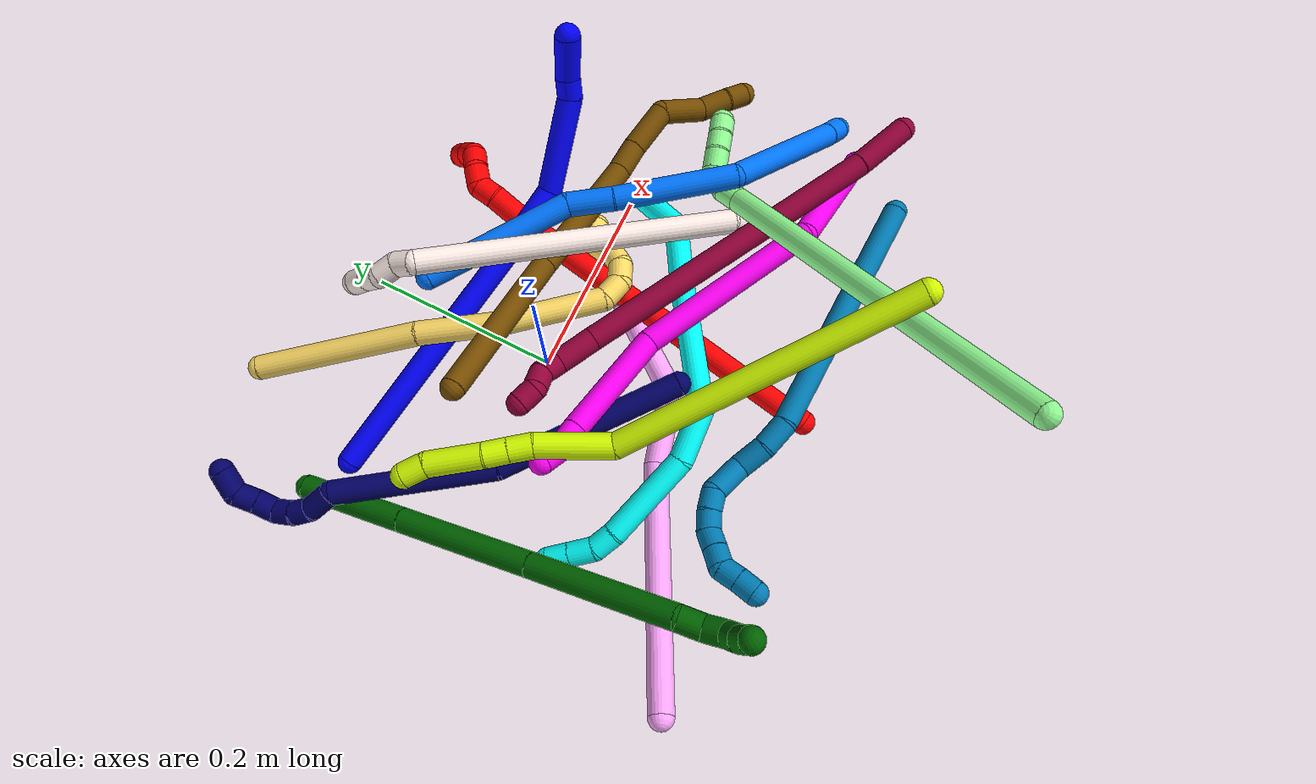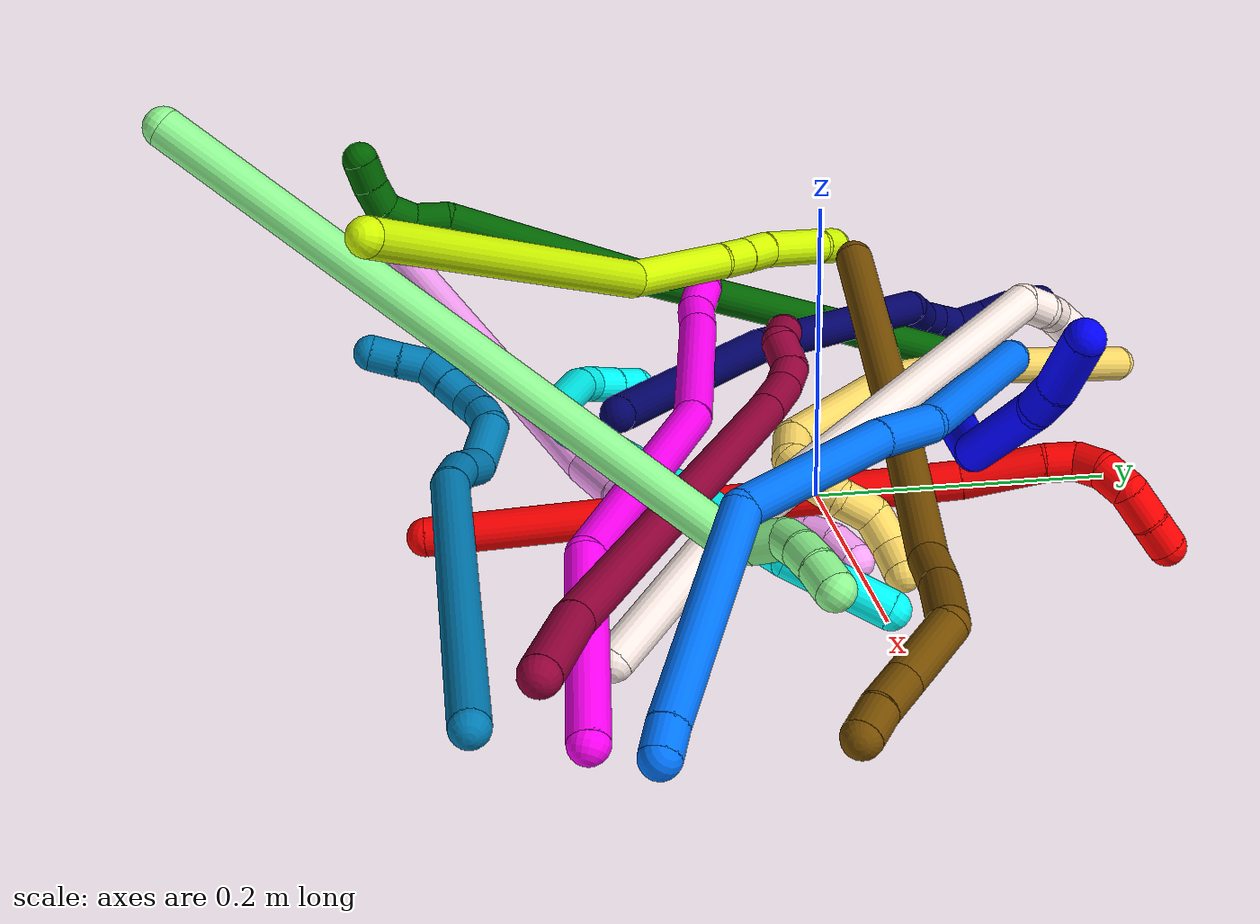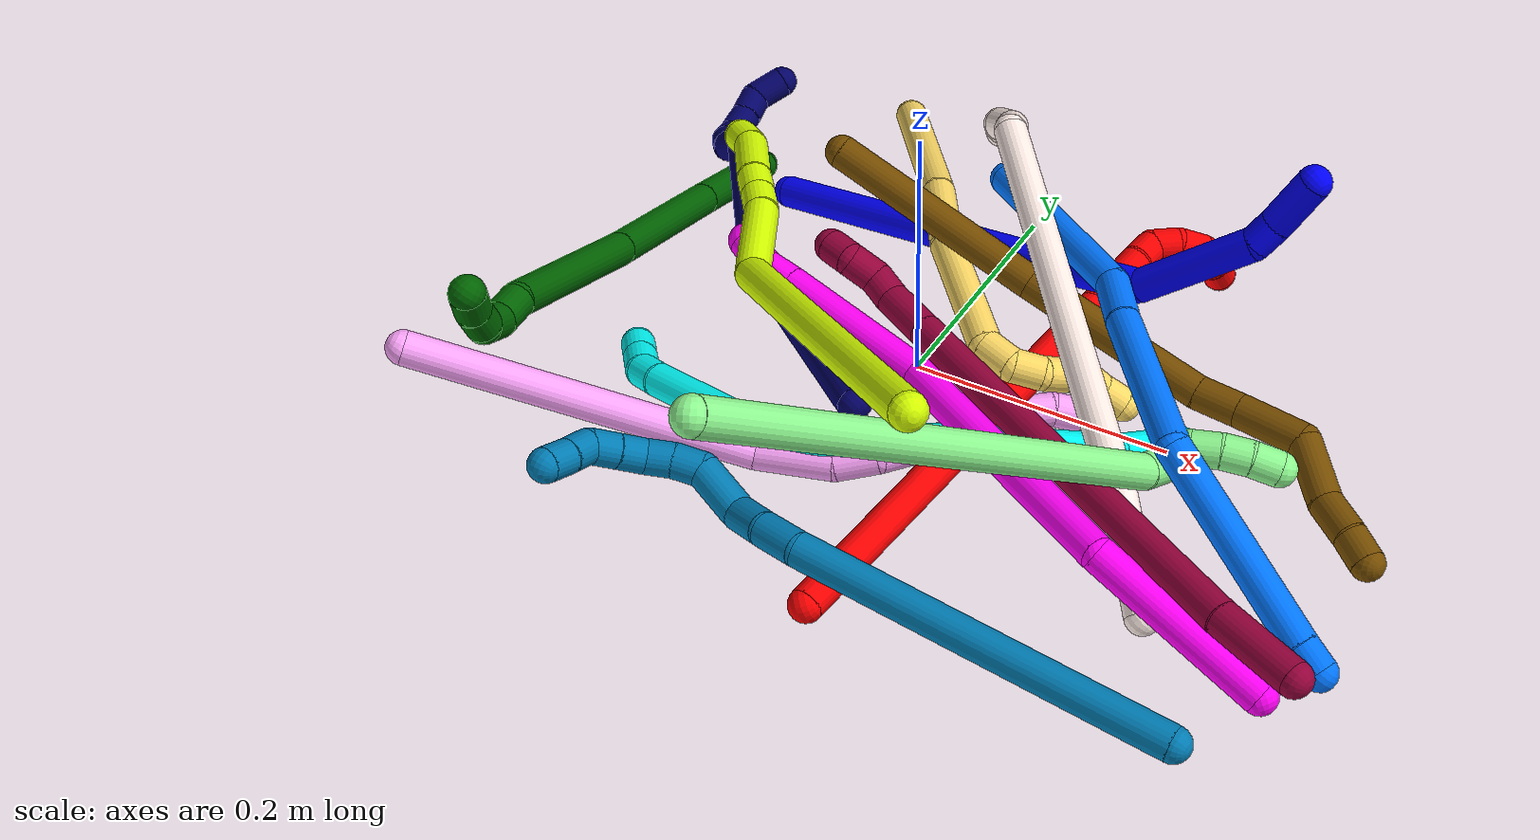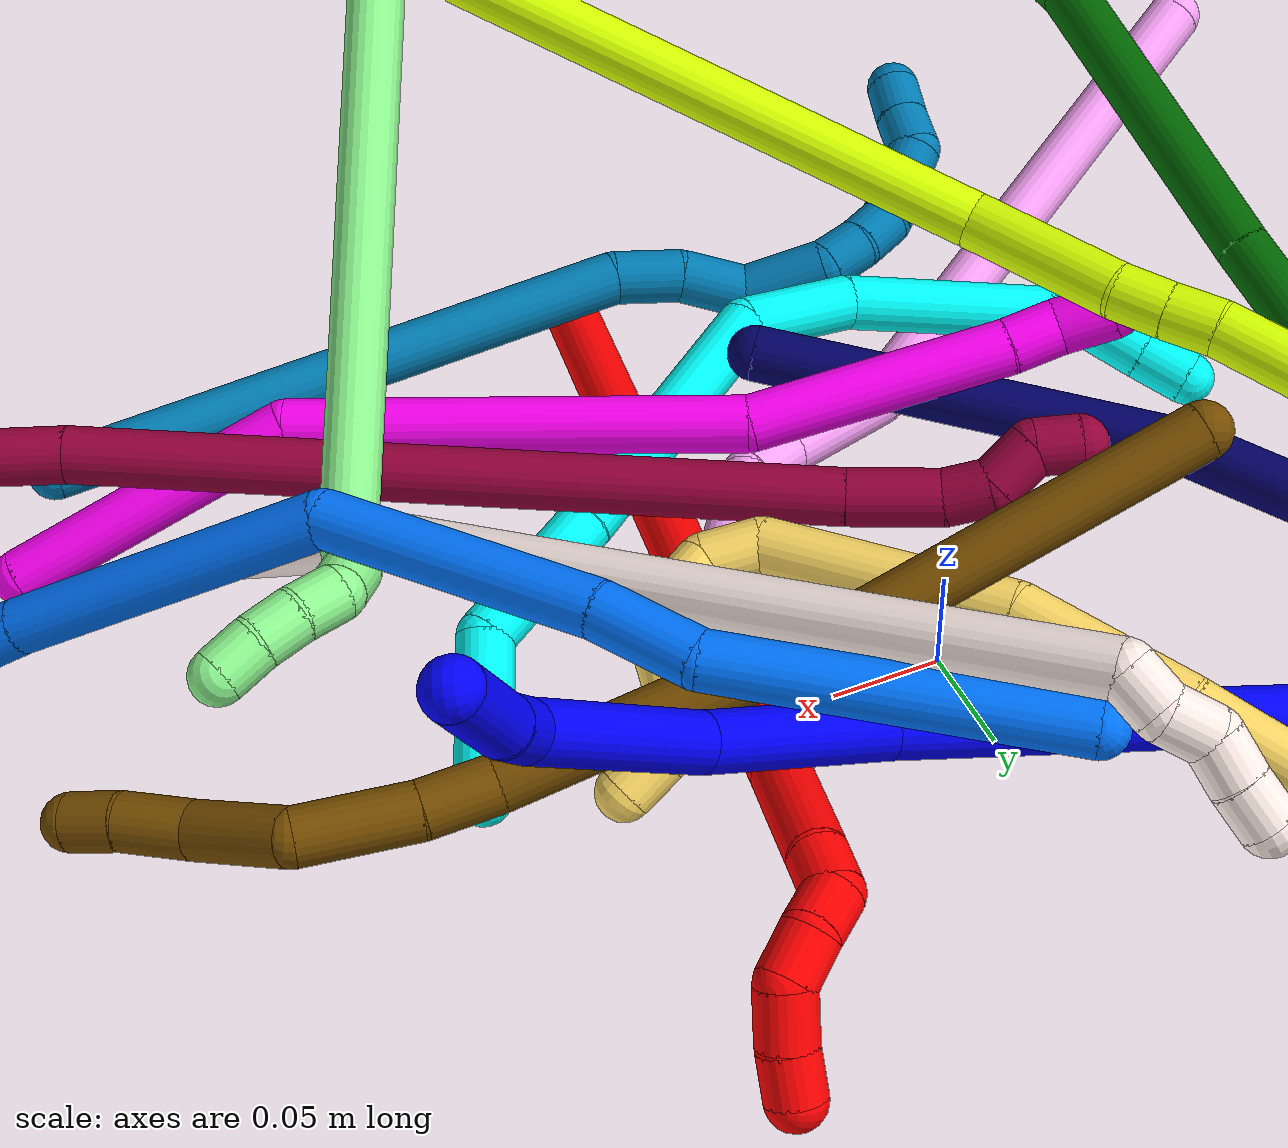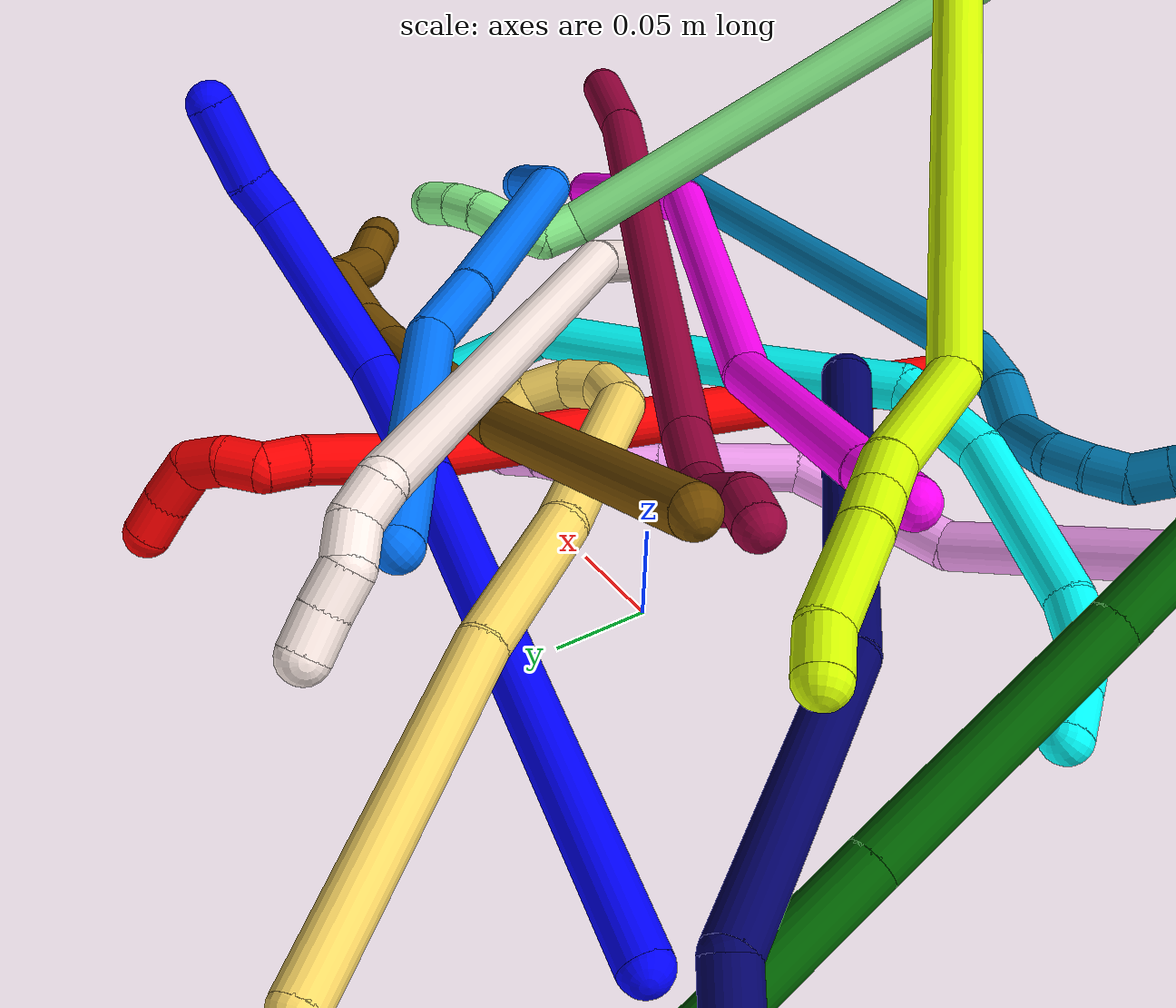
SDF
<sdf version="1.7">
 <world name="default">
  <plugin name="TubeGeneratorPlugin" filename="libtube_generator_plugin.so"/>
  <model name="photoneo_s_sensor">
   <static>1</static>
   <pose>0 0 2 1.57079 1.57079 3.14159</pose>
   <link name="link">
    <inertial><mass>0.1</mass></inertial>
    <sensor name="sensor" type="depth">
     <update_rate>30</update_rate>
     <camera>
      <horizontal_fov>1.22</horizontal_fov>
      <image><width>1920</width><height>1200</height><format>B8G8R8</format></image>
      <clip><near>0.1</near><far>4</far></clip>
      <depth_camera><output>points</output></depth_camera>
     </camera>
     <plugin name="camera_plugin" filename="libgazebo_ros_depth_camera.so">
      <baseline>0.2</baseline>
      <alwaysOn>1</alwaysOn>
      <updateRate>0.0</updateRate>
      <cameraName>camera_ir</cameraName>
      <imageTopicName>/camera/color/image_raw</imageTopicName>
      <cameraInfoTopicName>/camera/color/camera_info</cameraInfoTopicName>
      <depthImageTopicName>/camera/depth/image_raw</depthImageTopicName>
      <depthImageCameraInfoTopicName>/camera/depth/camera_info</depthImageCameraInfoTopicName>
      <pointCloudTopicName>/camera/depth/points</pointCloudTopicName>
      <frameName>fr_optical</frameName>
      <pointCloudCutoff>0.1</pointCloudCutoff>
      <pointCloudCutoffMax>2.0</pointCloudCutoffMax>
      <distortionK1>0</distortionK1>
      <distortionK2>0</distortionK2>
      <distortionK3>0</distortionK3>
      <distortionT1>0</distortionT1>
      <distortionT2>0</distortionT2>
      <CxPrime>0</CxPrime>
      <Cx>0</Cx>
      <Cy>0</Cy>
      <focalLength>0</focalLength>
      <hackBaseline>0</hackBaseline>
     </plugin>
    </sensor>
   </link>
  </model>
  <gravity>0 0 -9.8</gravity>
  <magnetic_field>6e-06 2.3e-05 -4.2e-05</magnetic_field>
  <atmosphere type="adiabatic"/>
  <physics name="default_physics" default="0" type="ode">
   <max_step_size>0.003</max_step_size>
   <real_time_factor>1</real_time_factor>
   <real_time_update_rate>1000</real_time_update_rate>
   <max_contacts>10000</max_contacts>
   <ode>
    <solver>
     <type>quick</type>
     <iters>100</iters>
     <sor>1.3</sor>
     <use_dynamic_moi_rescaling>0</use_dynamic_moi_rescaling>
    </solver>
    <constraints>
     <contact_max_correcting_vel>0</contact_max_correcting_vel>
     <contact_surface_layer>0.001</contact_surface_layer>
     <cfm>0</cfm>
     <erp>0.2</erp>
    </constraints>
   </ode>
  </physics>
  <scene><ambient>0.4 0.4 0.4 1</ambient><background>0.7 0.7 0.7 1</background><shadows>0</shadows></scene>
  <audio><device>default</device></audio>
  <spherical_coordinates>
   <surface_model>EARTH_WGS84</surface_model>
   <latitude_deg>0</latitude_deg>
   <longitude_deg>0</longitude_deg>
   <elevation>0</elevation>
   <heading_deg>0</heading_deg>
  </spherical_coordinates>
  <model name="bin">
   <static>1</static>
   <link name="bottom">
    <collision name="collision-bottom">
     <pose>0 0 -0.01 0 -0 0</pose>
     <geometry><box><size>0.8 0.6 0.02</size></box></geometry>
     <surface>
      <friction><ode><mu>100</mu><mu2>100</mu2></ode></friction>
      <contact><collide_bitmask>65535</collide_bitmask></contact>
     </surface>
    </collision>
   </link>
   <link name="west_wall">
    <collision name="collision-west_wall">
     <pose>-0.41 0 0.1 0 -0 0</pose>
     <geometry><box><size>0.02 0.6 0.2</size></box></geometry>
     <surface>
      <friction><ode><mu>100</mu><mu2>100</mu2></ode></friction>
      <contact><collide_bitmask>65535</collide_bitmask></contact>
     </surface>
    </collision>
   </link>
   <link name="east_wall">
    <collision name="collision-east_wall">
     <pose>0.41 0 0.1 0 -0 0</pose>
     <geometry><box><size>0.02 0.6 0.2</size></box></geometry>
     <surface>
      <friction><ode><mu>100</mu><mu2>100</mu2></ode></friction>
      <contact><collide_bitmask>65535</collide_bitmask></contact>
     </surface>
    </collision>
   </link>
   <link name="south_wall">
    <collision name="collision-south_wall">
     <pose>0 -0.31 0.1 0 -0 0</pose>
     <geometry><box><size>0.8 0.02 0.2</size></box></geometry>
     <surface>
      <friction><ode><mu>100</mu><mu2>100</mu2></ode></friction>
      <contact><collide_bitmask>65535</collide_bitmask></contact>
     </surface>
    </collision>
   </link>
   <link name="north_wall">
    <collision name="collision-north_wall">
     <pose>0 0.31 0.1 0 -0 0</pose>
     <geometry><box><size>0.8 0.02 0.2</size></box></geometry>
     <surface>
      <friction><ode><mu>100</mu><mu2>100</mu2></ode></friction>
      <contact><collide_bitmask>65535</collide_bitmask></contact>
     </surface>
    </collision>
   </link>
  </model>
  <model name="1">
   <static>0</static>
   <link name="1">
    <collision name="collision-cylinder-e_1_1_4">
     <pose>0.050311 0.040221 0.114815 -0.336952 0.392131 -0.067539</pose>
     <geometry><cylinder><radius>0.0125</radius><length>0.263298</length></cylinder></geometry>
     <surface>
      <friction><ode><mu>1.16</mu><mu2>1.16</mu2><slip1>0</slip1><slip2>0</slip2></ode></friction>
      <contact><ode><kp>1e+06</kp><kd>1</kd><max_vel>0</max_vel><min_depth>0.001</min_depth></ode></contact>
     </surface>
    </collision>
    <visual name="visual-cylinder-e_1_1_4">
     <pose>0.050311 0.040221 0.114815 -0.336952 0.392131 -0.067539</pose>
     <geometry><cylinder><radius>0.0125</radius><length>0.263298</length></cylinder></geometry>
     <material><ambient>0 0 1 1</ambient></material>
    </visual>
    <collision name="collision-cylinder-e_2_4_5">
     <pose>0.116719 0.091444 0.26331 -0.315743 0.426448 -0.06891</pose>
     <geometry><cylinder><radius>0.0125</radius><length>0.077834</length></cylinder></geometry>
     <surface>
      <friction><ode><mu>1.16</mu><mu2>1.16</mu2><slip1>0</slip1><slip2>0</slip2></ode></friction>
      <contact><ode><kp>1e+06</kp><kd>1</kd><max_vel>0</max_vel><min_depth>0.001</min_depth></ode></contact>
     </surface>
    </collision>
    <visual name="visual-cylinder-e_2_4_5">
     <pose>0.116719 0.091444 0.26331 -0.315743 0.426448 -0.06891</pose>
     <geometry><cylinder><radius>0.0125</radius><length>0.077834</length></cylinder></geometry>
     <material><ambient>0 0 1 1</ambient></material>
    </visual>
    <collision name="collision-cylinder-e_3_5_6">
     <pose>0.165396 0.128268 0.320808 -0.825734 0.747754 -0.340391</pose>
     <geometry><cylinder><radius>0.0125</radius><length>0.095822</length></cylinder></geometry>
     <surface>
      <friction><ode><mu>1.16</mu><mu2>1.16</mu2><slip1>0</slip1><slip2>0</slip2></ode></friction>
      <contact><ode><kp>1e+06</kp><kd>1</kd><max_vel>0</max_vel><min_depth>0.001</min_depth></ode></contact>
     </surface>
    </collision>
    <visual name="visual-cylinder-e_3_5_6">
     <pose>0.165396 0.128268 0.320808 -0.825734 0.747754 -0.340391</pose>
     <geometry><cylinder><radius>0.0125</radius><length>0.095822</length></cylinder></geometry>
     <material><ambient>0 0 1 1</ambient></material>
    </visual>
    <collision name="collision-cylinder-e_4_6_7">
     <pose>0.206089 0.160478 0.345975 -1.36273 0.893244 -0.740842</pose>
     <geometry><cylinder><radius>0.0125</radius><length>0.02083</length></cylinder></geometry>
     <surface>
      <friction><ode><mu>1.16</mu><mu2>1.16</mu2><slip1>0</slip1><slip2>0</slip2></ode></friction>
      <contact><ode><kp>1e+06</kp><kd>1</kd><max_vel>0</max_vel><min_depth>0.001</min_depth></ode></contact>
     </surface>
    </collision>
    <visual name="visual-cylinder-e_4_6_7">
     <pose>0.206089 0.160478 0.345975 -1.36273 0.893244 -0.740842</pose>
     <geometry><cylinder><radius>0.0125</radius><length>0.02083</length></cylinder></geometry>
     <material><ambient>0 0 1 1</ambient></material>
    </visual>
    <collision name="collision-cylinder-e_5_7_2">
     <pose>0.227801 0.182778 0.350059 -1.40059 0.699971 -0.596881</pose>
     <geometry><cylinder><radius>0.0125</radius><length>0.042217</length></cylinder></geometry>
     <surface>
      <friction><ode><mu>1.16</mu><mu2>1.16</mu2><slip1>0</slip1><slip2>0</slip2></ode></friction>
      <contact><ode><kp>1e+06</kp><kd>1</kd><max_vel>0</max_vel><min_depth>0.001</min_depth></ode></contact>
     </surface>
    </collision>
    <visual name="visual-cylinder-e_5_7_2">
     <pose>0.227801 0.182778 0.350059 -1.40059 0.699971 -0.596881</pose>
     <geometry><cylinder><radius>0.0125</radius><length>0.042217</length></cylinder></geometry>
     <material><ambient>0 0 1 1</ambient></material>
    </visual>
    <collision name="collision-sphere-2">
     <pose>0.241399 0.19869 0.352794 0 -0 0</pose>
     <geometry><sphere><radius>0.0125</radius></sphere></geometry>
     <surface>
      <friction><ode><mu>1.16</mu><mu2>1.16</mu2><slip1>0</slip1><slip2>0</slip2></ode></friction>
      <contact><ode><kp>1e+06</kp><kd>1</kd><max_vel>0</max_vel><min_depth>0.001</min_depth></ode></contact>
     </surface>
    </collision>
    <visual name="visual-sphere-2">
     <pose>0.241399 0.19869 0.352794 0 -0 0</pose>
     <geometry><sphere><radius>0.0125</radius></sphere></geometry>
     <material><ambient>0 0 1 1</ambient></material>
    </visual>
    <collision name="collision-sphere-7">
     <pose>0.214203 0.166866 0.347324 0 -0 0</pose>
     <geometry><sphere><radius>0.0125</radius></sphere></geometry>
     <surface>
      <friction><ode><mu>1.16</mu><mu2>1.16</mu2><slip1>0</slip1><slip2>0</slip2></ode></friction>
      <contact><ode><kp>1e+06</kp><kd>1</kd><max_vel>0</max_vel><min_depth>0.001</min_depth></ode></contact>
     </surface>
    </collision>
    <visual name="visual-sphere-7">
     <pose>0.214203 0.166866 0.347324 0 -0 0</pose>
     <geometry><sphere><radius>0.0125</radius></sphere></geometry>
     <material><ambient>0 0 1 1</ambient></material>
    </visual>
    <collision name="collision-sphere-6">
     <pose>0.197975 0.15409 0.344627 0 -0 0</pose>
     <geometry><sphere><radius>0.0125</radius></sphere></geometry>
     <surface>
      <friction><ode><mu>1.16</mu><mu2>1.16</mu2><slip1>0</slip1><slip2>0</slip2></ode></friction>
      <contact><ode><kp>1e+06</kp><kd>1</kd><max_vel>0</max_vel><min_depth>0.001</min_depth></ode></contact>
     </surface>
    </collision>
    <visual name="visual-sphere-6">
     <pose>0.197975 0.15409 0.344627 0 -0 0</pose>
     <geometry><sphere><radius>0.0125</radius></sphere></geometry>
     <material><ambient>0 0 1 1</ambient></material>
    </visual>
    <collision name="collision-sphere-5">
     <pose>0.132816 0.102447 0.29699 0 -0 0</pose>
     <geometry><sphere><radius>0.0125</radius></sphere></geometry>
     <surface>
      <friction><ode><mu>1.16</mu><mu2>1.16</mu2><slip1>0</slip1><slip2>0</slip2></ode></friction>
      <contact><ode><kp>1e+06</kp><kd>1</kd><max_vel>0</max_vel><min_depth>0.001</min_depth></ode></contact>
     </surface>
    </collision>
    <visual name="visual-sphere-5">
     <pose>0.132816 0.102447 0.29699 0 -0 0</pose>
     <geometry><sphere><radius>0.0125</radius></sphere></geometry>
     <material><ambient>0 0 1 1</ambient></material>
    </visual>
    <collision name="collision-sphere-1">
     <geometry><sphere><radius>0.0125</radius></sphere></geometry>
     <surface>
      <friction><ode><mu>1.16</mu><mu2>1.16</mu2><slip1>0</slip1><slip2>0</slip2></ode></friction>
      <contact><ode><kp>1e+06</kp><kd>1</kd><max_vel>0</max_vel><min_depth>0.001</min_depth></ode></contact>
     </surface>
    </collision>
    <visual name="visual-sphere-1">
     <geometry><sphere><radius>0.0125</radius></sphere></geometry>
     <material><ambient>0 0 1 1</ambient></material>
    </visual>
    <collision name="collision-sphere-4">
     <pose>0.100621 0.080442 0.22963 0 -0 0</pose>
     <geometry><sphere><radius>0.0125</radius></sphere></geometry>
     <surface>
      <friction><ode><mu>1.16</mu><mu2>1.16</mu2><slip1>0</slip1><slip2>0</slip2></ode></friction>
      <contact><ode><kp>1e+06</kp><kd>1</kd><max_vel>0</max_vel><min_depth>0.001</min_depth></ode></contact>
     </surface>
    </collision>
    <visual name="visual-sphere-4">
     <pose>0.100621 0.080442 0.22963 0 -0 0</pose>
     <geometry><sphere><radius>0.0125</radius></sphere></geometry>
     <material><ambient>0 0 1 1</ambient></material>
    </visual>
    <inertial>
     <pose>0.104179 0.082115 0.206901 0 -0 0</pose>
     <mass>0.5</mass>
     <inertia>
      <ixx>0.001407</ixx>
      <ixy>0</ixy>
      <ixz>0</ixz>
      <iyy>0.001457</iyy>
      <iyz>0</iyz>
      <izz>-0.001162</izz>
     </inertia>
    </inertial>
   </link>
   <pose>-0.184646 0.129528 0.015418 1.80007 -0.280861 1.01844</pose>
  </model>
  <model name="2">
   <static>0</static>
   <link name="2">
    <collision name="collision-cylinder-e_1_1_4">
     <pose>0.093319 0.098077 0.103034 -0.760754 0.580599 -0.237775</pose>
     <geometry><cylinder><radius>0.0125</radius><length>0.340255</length></cylinder></geometry>
     <surface>
      <friction><ode><mu>1.16</mu><mu2>1.16</mu2><slip1>0</slip1><slip2>0</slip2></ode></friction>
      <contact><ode><kp>1e+06</kp><kd>1</kd><max_vel>0</max_vel><min_depth>0.001</min_depth></ode></contact>
     </surface>
    </collision>
    <visual name="visual-cylinder-e_1_1_4">
     <pose>0.093319 0.098077 0.103034 -0.760754 0.580599 -0.237775</pose>
     <geometry><cylinder><radius>0.0125</radius><length>0.340255</length></cylinder></geometry>
     <material><ambient>1 0 0 1</ambient></material>
    </visual>
    <collision name="collision-cylinder-e_2_4_5">
     <pose>0.198428 0.211961 0.223919 -0.724766 0.459167 -0.176745</pose>
     <geometry><cylinder><radius>0.0125</radius><length>0.053201</length></cylinder></geometry>
     <surface>
      <friction><ode><mu>1.16</mu><mu2>1.16</mu2><slip1>0</slip1><slip2>0</slip2></ode></friction>
      <contact><ode><kp>1e+06</kp><kd>1</kd><max_vel>0</max_vel><min_depth>0.001</min_depth></ode></contact>
     </surface>
    </collision>
    <visual name="visual-cylinder-e_2_4_5">
     <pose>0.198428 0.211961 0.223919 -0.724766 0.459167 -0.176745</pose>
     <geometry><cylinder><radius>0.0125</radius><length>0.053201</length></cylinder></geometry>
     <material><ambient>1 0 0 1</ambient></material>
    </visual>
    <collision name="collision-cylinder-e_3_5_6">
     <pose>0.216259 0.233398 0.247739 -0.756097 0.634859 -0.259493</pose>
     <geometry><cylinder><radius>0.0125</radius><length>0.020377</length></cylinder></geometry>
     <surface>
      <friction><ode><mu>1.16</mu><mu2>1.16</mu2><slip1>0</slip1><slip2>0</slip2></ode></friction>
      <contact><ode><kp>1e+06</kp><kd>1</kd><max_vel>0</max_vel><min_depth>0.001</min_depth></ode></contact>
     </surface>
    </collision>
    <visual name="visual-cylinder-e_3_5_6">
     <pose>0.216259 0.233398 0.247739 -0.756097 0.634859 -0.259493</pose>
     <geometry><cylinder><radius>0.0125</radius><length>0.020377</length></cylinder></geometry>
     <material><ambient>1 0 0 1</ambient></material>
    </visual>
    <collision name="collision-cylinder-e_4_6_7">
     <pose>0.226659 0.238064 0.2627 0.106603 0.448979 0.024363</pose>
     <geometry><cylinder><radius>0.0125</radius><length>0.020078</length></cylinder></geometry>
     <surface>
      <friction><ode><mu>1.16</mu><mu2>1.16</mu2><slip1>0</slip1><slip2>0</slip2></ode></friction>
      <contact><ode><kp>1e+06</kp><kd>1</kd><max_vel>0</max_vel><min_depth>0.001</min_depth></ode></contact>
     </surface>
    </collision>
    <visual name="visual-cylinder-e_4_6_7">
     <pose>0.226659 0.238064 0.2627 0.106603 0.448979 0.024363</pose>
     <geometry><cylinder><radius>0.0125</radius><length>0.020078</length></cylinder></geometry>
     <material><ambient>1 0 0 1</ambient></material>
    </visual>
    <collision name="collision-cylinder-e_5_7_8">
     <pose>0.238078 0.233812 0.279046 0.420609 0.719725 0.160284</pose>
     <geometry><cylinder><radius>0.0125</radius><length>0.021424</length></cylinder></geometry>
     <surface>
      <friction><ode><mu>1.16</mu><mu2>1.16</mu2><slip1>0</slip1><slip2>0</slip2></ode></friction>
      <contact><ode><kp>1e+06</kp><kd>1</kd><max_vel>0</max_vel><min_depth>0.001</min_depth></ode></contact>
     </surface>
    </collision>
    <visual name="visual-cylinder-e_5_7_8">
     <pose>0.238078 0.233812 0.279046 0.420609 0.719725 0.160284</pose>
     <geometry><cylinder><radius>0.0125</radius><length>0.021424</length></cylinder></geometry>
     <material><ambient>1 0 0 1</ambient></material>
    </visual>
    <collision name="collision-cylinder-e_6_8_9">
     <pose>0.256868 0.228232 0.287456 1.13848 1.35889 0.954111</pose>
     <geometry><cylinder><radius>0.0125</radius><length>0.023994</length></cylinder></geometry>
     <surface>
      <friction><ode><mu>1.16</mu><mu2>1.16</mu2><slip1>0</slip1><slip2>0</slip2></ode></friction>
      <contact><ode><kp>1e+06</kp><kd>1</kd><max_vel>0</max_vel><min_depth>0.001</min_depth></ode></contact>
     </surface>
    </collision>
    <visual name="visual-cylinder-e_6_8_9">
     <pose>0.256868 0.228232 0.287456 1.13848 1.35889 0.954111</pose>
     <geometry><cylinder><radius>0.0125</radius><length>0.023994</length></cylinder></geometry>
     <material><ambient>1 0 0 1</ambient></material>
    </visual>
    <collision name="collision-cylinder-e_7_9_2">
     <pose>0.278874 0.224851 0.288493 1.58954 1.4651 1.48376</pose>
     <geometry><cylinder><radius>0.0125</radius><length>0.020671</length></cylinder></geometry>
     <surface>
      <friction><ode><mu>1.16</mu><mu2>1.16</mu2><slip1>0</slip1><slip2>0</slip2></ode></friction>
      <contact><ode><kp>1e+06</kp><kd>1</kd><max_vel>0</max_vel><min_depth>0.001</min_depth></ode></contact>
     </surface>
    </collision>
    <visual name="visual-cylinder-e_7_9_2">
     <pose>0.278874 0.224851 0.288493 1.58954 1.4651 1.48376</pose>
     <geometry><cylinder><radius>0.0125</radius><length>0.020671</length></cylinder></geometry>
     <material><ambient>1 0 0 1</ambient></material>
    </visual>
    <collision name="collision-sphere-2">
     <pose>0.289152 0.223761 0.288473 0 -0 0</pose>
     <geometry><sphere><radius>0.0125</radius></sphere></geometry>
     <surface>
      <friction><ode><mu>1.16</mu><mu2>1.16</mu2><slip1>0</slip1><slip2>0</slip2></ode></friction>
      <contact><ode><kp>1e+06</kp><kd>1</kd><max_vel>0</max_vel><min_depth>0.001</min_depth></ode></contact>
     </surface>
    </collision>
    <visual name="visual-sphere-2">
     <pose>0.289152 0.223761 0.288473 0 -0 0</pose>
     <geometry><sphere><radius>0.0125</radius></sphere></geometry>
     <material><ambient>1 0 0 1</ambient></material>
    </visual>
    <collision name="collision-sphere-9">
     <pose>0.268596 0.225941 0.288514 0 -0 0</pose>
     <geometry><sphere><radius>0.0125</radius></sphere></geometry>
     <surface>
      <friction><ode><mu>1.16</mu><mu2>1.16</mu2><slip1>0</slip1><slip2>0</slip2></ode></friction>
      <contact><ode><kp>1e+06</kp><kd>1</kd><max_vel>0</max_vel><min_depth>0.001</min_depth></ode></contact>
     </surface>
    </collision>
    <visual name="visual-sphere-9">
     <pose>0.268596 0.225941 0.288514 0 -0 0</pose>
     <geometry><sphere><radius>0.0125</radius></sphere></geometry>
     <material><ambient>1 0 0 1</ambient></material>
    </visual>
    <collision name="collision-sphere-4">
     <pose>0.186638 0.196153 0.206068 0 -0 0</pose>
     <geometry><sphere><radius>0.0125</radius></sphere></geometry>
     <surface>
      <friction><ode><mu>1.16</mu><mu2>1.16</mu2><slip1>0</slip1><slip2>0</slip2></ode></friction>
      <contact><ode><kp>1e+06</kp><kd>1</kd><max_vel>0</max_vel><min_depth>0.001</min_depth></ode></contact>
     </surface>
    </collision>
    <visual name="visual-sphere-4">
     <pose>0.186638 0.196153 0.206068 0 -0 0</pose>
     <geometry><sphere><radius>0.0125</radius></sphere></geometry>
     <material><ambient>1 0 0 1</ambient></material>
    </visual>
    <collision name="collision-sphere-1">
     <geometry><sphere><radius>0.0125</radius></sphere></geometry>
     <surface>
      <friction><ode><mu>1.16</mu><mu2>1.16</mu2><slip1>0</slip1><slip2>0</slip2></ode></friction>
      <contact><ode><kp>1e+06</kp><kd>1</kd><max_vel>0</max_vel><min_depth>0.001</min_depth></ode></contact>
     </surface>
    </collision>
    <visual name="visual-sphere-1">
     <geometry><sphere><radius>0.0125</radius></sphere></geometry>
     <material><ambient>1 0 0 1</ambient></material>
    </visual>
    <collision name="collision-sphere-8">
     <pose>0.245139 0.230523 0.286399 0 -0 0</pose>
     <geometry><sphere><radius>0.0125</radius></sphere></geometry>
     <surface>
      <friction><ode><mu>1.16</mu><mu2>1.16</mu2><slip1>0</slip1><slip2>0</slip2></ode></friction>
      <contact><ode><kp>1e+06</kp><kd>1</kd><max_vel>0</max_vel><min_depth>0.001</min_depth></ode></contact>
     </surface>
    </collision>
    <visual name="visual-sphere-8">
     <pose>0.245139 0.230523 0.286399 0 -0 0</pose>
     <geometry><sphere><radius>0.0125</radius></sphere></geometry>
     <material><ambient>1 0 0 1</ambient></material>
    </visual>
    <collision name="collision-sphere-5">
     <pose>0.210217 0.22777 0.241771 0 -0 0</pose>
     <geometry><sphere><radius>0.0125</radius></sphere></geometry>
     <surface>
      <friction><ode><mu>1.16</mu><mu2>1.16</mu2><slip1>0</slip1><slip2>0</slip2></ode></friction>
      <contact><ode><kp>1e+06</kp><kd>1</kd><max_vel>0</max_vel><min_depth>0.001</min_depth></ode></contact>
     </surface>
    </collision>
    <visual name="visual-sphere-5">
     <pose>0.210217 0.22777 0.241771 0 -0 0</pose>
     <geometry><sphere><radius>0.0125</radius></sphere></geometry>
     <material><ambient>1 0 0 1</ambient></material>
    </visual>
    <collision name="collision-sphere-6">
     <pose>0.222302 0.239026 0.253707 0 -0 0</pose>
     <geometry><sphere><radius>0.0125</radius></sphere></geometry>
     <surface>
      <friction><ode><mu>1.16</mu><mu2>1.16</mu2><slip1>0</slip1><slip2>0</slip2></ode></friction>
      <contact><ode><kp>1e+06</kp><kd>1</kd><max_vel>0</max_vel><min_depth>0.001</min_depth></ode></contact>
     </surface>
    </collision>
    <visual name="visual-sphere-6">
     <pose>0.222302 0.239026 0.253707 0 -0 0</pose>
     <geometry><sphere><radius>0.0125</radius></sphere></geometry>
     <material><ambient>1 0 0 1</ambient></material>
    </visual>
    <collision name="collision-sphere-7">
     <pose>0.231017 0.237101 0.271693 0 -0 0</pose>
     <geometry><sphere><radius>0.0125</radius></sphere></geometry>
     <surface>
      <friction><ode><mu>1.16</mu><mu2>1.16</mu2><slip1>0</slip1><slip2>0</slip2></ode></friction>
      <contact><ode><kp>1e+06</kp><kd>1</kd><max_vel>0</max_vel><min_depth>0.001</min_depth></ode></contact>
     </surface>
    </collision>
    <visual name="visual-sphere-7">
     <pose>0.231017 0.237101 0.271693 0 -0 0</pose>
     <geometry><sphere><radius>0.0125</radius></sphere></geometry>
     <material><ambient>1 0 0 1</ambient></material>
    </visual>
    <inertial>
     <pose>0.13659 0.138633 0.152264 0 -0 0</pose>
     <mass>0.5</mass>
     <inertia><ixx>0.002067</ixx><ixy>0</ixy><ixz>0</ixz><iyy>0.002</iyy><iyz>0</iyz><izz>-0.003707</izz></inertia>
    </inertial>
   </link>
   <pose>0.058508 -0.265868 0.014459 0.908112 0.876649 1.54146</pose>
  </model>
  <model name="3">
   <static>0</static>
   <link name="3">
    <collision name="collision-cylinder-e_1_1_4">
     <pose>-0.009029 0.030796 0.013346 -1.16187 -0.262787 0.173087</pose>
     <geometry><cylinder><radius>0.0125</radius><length>0.069514</length></cylinder></geometry>
     <surface>
      <friction><ode><mu>1.16</mu><mu2>1.16</mu2><slip1>0</slip1><slip2>0</slip2></ode></friction>
      <contact><ode><kp>1e+06</kp><kd>1</kd><max_vel>0</max_vel><min_depth>0.001</min_depth></ode></contact>
     </surface>
    </collision>
    <visual name="visual-cylinder-e_1_1_4">
     <pose>-0.009029 0.030796 0.013346 -1.16187 -0.262787 0.173087</pose>
     <geometry><cylinder><radius>0.0125</radius><length>0.069514</length></cylinder></geometry>
     <material><ambient>0.003922 1 0.996078 1</ambient></material>
    </visual>
    <collision name="collision-cylinder-e_2_4_5">
     <pose>-0.045353 0.07869 0.041464 -0.858208 -0.879317 0.423951</pose>
     <geometry><cylinder><radius>0.0125</radius><length>0.070867</length></cylinder></geometry>
     <surface>
      <friction><ode><mu>1.16</mu><mu2>1.16</mu2><slip1>0</slip1><slip2>0</slip2></ode></friction>
      <contact><ode><kp>1e+06</kp><kd>1</kd><max_vel>0</max_vel><min_depth>0.001</min_depth></ode></contact>
     </surface>
    </collision>
    <visual name="visual-cylinder-e_2_4_5">
     <pose>-0.045353 0.07869 0.041464 -0.858208 -0.879317 0.423951</pose>
     <geometry><cylinder><radius>0.0125</radius><length>0.070867</length></cylinder></geometry>
     <material><ambient>0.003922 1 0.996078 1</ambient></material>
    </visual>
    <collision name="collision-cylinder-e_3_5_6">
     <pose>-0.122105 0.130077 0.086009 -0.855806 -0.82803 0.39558</pose>
     <geometry><cylinder><radius>0.0125</radius><length>0.134286</length></cylinder></geometry>
     <surface>
      <friction><ode><mu>1.16</mu><mu2>1.16</mu2><slip1>0</slip1><slip2>0</slip2></ode></friction>
      <contact><ode><kp>1e+06</kp><kd>1</kd><max_vel>0</max_vel><min_depth>0.001</min_depth></ode></contact>
     </surface>
    </collision>
    <visual name="visual-cylinder-e_3_5_6">
     <pose>-0.122105 0.130077 0.086009 -0.855806 -0.82803 0.39558</pose>
     <geometry><cylinder><radius>0.0125</radius><length>0.134286</length></cylinder></geometry>
     <material><ambient>0.003922 1 0.996078 1</ambient></material>
    </visual>
    <collision name="collision-cylinder-e_4_6_7">
     <pose>-0.197229 0.164097 0.124496 0.030874 -1.2433 -0.022119</pose>
     <geometry><cylinder><radius>0.0125</radius><length>0.054215</length></cylinder></geometry>
     <surface>
      <friction><ode><mu>1.16</mu><mu2>1.16</mu2><slip1>0</slip1><slip2>0</slip2></ode></friction>
      <contact><ode><kp>1e+06</kp><kd>1</kd><max_vel>0</max_vel><min_depth>0.001</min_depth></ode></contact>
     </surface>
    </collision>
    <visual name="visual-cylinder-e_4_6_7">
     <pose>-0.197229 0.164097 0.124496 0.030874 -1.2433 -0.022119</pose>
     <geometry><cylinder><radius>0.0125</radius><length>0.054215</length></cylinder></geometry>
     <material><ambient>0.003922 1 0.996078 1</ambient></material>
    </visual>
    <collision name="collision-cylinder-e_5_7_8">
     <pose>-0.269309 0.150423 0.137398 1.26815 -1.27698 -0.999218</pose>
     <geometry><cylinder><radius>0.0125</radius><length>0.096981</length></cylinder></geometry>
     <surface>
      <friction><ode><mu>1.16</mu><mu2>1.16</mu2><slip1>0</slip1><slip2>0</slip2></ode></friction>
      <contact><ode><kp>1e+06</kp><kd>1</kd><max_vel>0</max_vel><min_depth>0.001</min_depth></ode></contact>
     </surface>
    </collision>
    <visual name="visual-cylinder-e_5_7_8">
     <pose>-0.269309 0.150423 0.137398 1.26815 -1.27698 -0.999218</pose>
     <geometry><cylinder><radius>0.0125</radius><length>0.096981</length></cylinder></geometry>
     <material><ambient>0.003922 1 0.996078 1</ambient></material>
    </visual>
    <collision name="collision-cylinder-e_6_8_9">
     <pose>-0.32642 0.131555 0.142108 1.4751 -1.09688 -1.01353</pose>
     <geometry><cylinder><radius>0.0125</radius><length>0.02405</length></cylinder></geometry>
     <surface>
      <friction><ode><mu>1.16</mu><mu2>1.16</mu2><slip1>0</slip1><slip2>0</slip2></ode></friction>
      <contact><ode><kp>1e+06</kp><kd>1</kd><max_vel>0</max_vel><min_depth>0.001</min_depth></ode></contact>
     </surface>
    </collision>
    <visual name="visual-cylinder-e_6_8_9">
     <pose>-0.32642 0.131555 0.142108 1.4751 -1.09688 -1.01353</pose>
     <geometry><cylinder><radius>0.0125</radius><length>0.02405</length></cylinder></geometry>
     <material><ambient>0.003922 1 0.996078 1</ambient></material>
    </visual>
    <collision name="collision-cylinder-e_7_9_10">
     <pose>-0.345964 0.116875 0.139719 1.87691 -0.741013 -0.974953</pose>
     <geometry><cylinder><radius>0.0125</radius><length>0.026205</length></cylinder></geometry>
     <surface>
      <friction><ode><mu>1.16</mu><mu2>1.16</mu2><slip1>0</slip1><slip2>0</slip2></ode></friction>
      <contact><ode><kp>1e+06</kp><kd>1</kd><max_vel>0</max_vel><min_depth>0.001</min_depth></ode></contact>
     </surface>
    </collision>
    <visual name="visual-cylinder-e_7_9_10">
     <pose>-0.345964 0.116875 0.139719 1.87691 -0.741013 -0.974953</pose>
     <geometry><cylinder><radius>0.0125</radius><length>0.026205</length></cylinder></geometry>
     <material><ambient>0.003922 1 0.996078 1</ambient></material>
    </visual>
    <collision name="collision-cylinder-e_8_10_2">
     <pose>-0.362999 0.099485 0.133854 1.91741 -0.755846 -1.02934</pose>
     <geometry><cylinder><radius>0.0125</radius><length>0.023882</length></cylinder></geometry>
     <surface>
      <friction><ode><mu>1.16</mu><mu2>1.16</mu2><slip1>0</slip1><slip2>0</slip2></ode></friction>
      <contact><ode><kp>1e+06</kp><kd>1</kd><max_vel>0</max_vel><min_depth>0.001</min_depth></ode></contact>
     </surface>
    </collision>
    <visual name="visual-cylinder-e_8_10_2">
     <pose>-0.362999 0.099485 0.133854 1.91741 -0.755846 -1.02934</pose>
     <geometry><cylinder><radius>0.0125</radius><length>0.023882</length></cylinder></geometry>
     <material><ambient>0.003922 1 0.996078 1</ambient></material>
    </visual>
    <collision name="collision-sphere-2">
     <pose>-0.37119 0.091313 0.130902 0 -0 0</pose>
     <geometry><sphere><radius>0.0125</radius></sphere></geometry>
     <surface>
      <friction><ode><mu>1.16</mu><mu2>1.16</mu2><slip1>0</slip1><slip2>0</slip2></ode></friction>
      <contact><ode><kp>1e+06</kp><kd>1</kd><max_vel>0</max_vel><min_depth>0.001</min_depth></ode></contact>
     </surface>
    </collision>
    <visual name="visual-sphere-2">
     <pose>-0.37119 0.091313 0.130902 0 -0 0</pose>
     <geometry><sphere><radius>0.0125</radius></sphere></geometry>
     <material><ambient>0.003922 1 0.996078 1</ambient></material>
    </visual>
    <collision name="collision-sphere-10">
     <pose>-0.354809 0.107658 0.136806 0 -0 0</pose>
     <geometry><sphere><radius>0.0125</radius></sphere></geometry>
     <surface>
      <friction><ode><mu>1.16</mu><mu2>1.16</mu2><slip1>0</slip1><slip2>0</slip2></ode></friction>
      <contact><ode><kp>1e+06</kp><kd>1</kd><max_vel>0</max_vel><min_depth>0.001</min_depth></ode></contact>
     </surface>
    </collision>
    <visual name="visual-sphere-10">
     <pose>-0.354809 0.107658 0.136806 0 -0 0</pose>
     <geometry><sphere><radius>0.0125</radius></sphere></geometry>
     <material><ambient>0.003922 1 0.996078 1</ambient></material>
    </visual>
    <collision name="collision-sphere-9">
     <pose>-0.33712 0.126093 0.142632 0 -0 0</pose>
     <geometry><sphere><radius>0.0125</radius></sphere></geometry>
     <surface>
      <friction><ode><mu>1.16</mu><mu2>1.16</mu2><slip1>0</slip1><slip2>0</slip2></ode></friction>
      <contact><ode><kp>1e+06</kp><kd>1</kd><max_vel>0</max_vel><min_depth>0.001</min_depth></ode></contact>
     </surface>
    </collision>
    <visual name="visual-sphere-9">
     <pose>-0.33712 0.126093 0.142632 0 -0 0</pose>
     <geometry><sphere><radius>0.0125</radius></sphere></geometry>
     <material><ambient>0.003922 1 0.996078 1</ambient></material>
    </visual>
    <collision name="collision-sphere-4">
     <pose>-0.018058 0.061593 0.026692 0 -0 0</pose>
     <geometry><sphere><radius>0.0125</radius></sphere></geometry>
     <surface>
      <friction><ode><mu>1.16</mu><mu2>1.16</mu2><slip1>0</slip1><slip2>0</slip2></ode></friction>
      <contact><ode><kp>1e+06</kp><kd>1</kd><max_vel>0</max_vel><min_depth>0.001</min_depth></ode></contact>
     </surface>
    </collision>
    <visual name="visual-sphere-4">
     <pose>-0.018058 0.061593 0.026692 0 -0 0</pose>
     <geometry><sphere><radius>0.0125</radius></sphere></geometry>
     <material><ambient>0.003922 1 0.996078 1</ambient></material>
    </visual>
    <collision name="collision-sphere-1">
     <geometry><sphere><radius>0.0125</radius></sphere></geometry>
     <surface>
      <friction><ode><mu>1.16</mu><mu2>1.16</mu2><slip1>0</slip1><slip2>0</slip2></ode></friction>
      <contact><ode><kp>1e+06</kp><kd>1</kd><max_vel>0</max_vel><min_depth>0.001</min_depth></ode></contact>
     </surface>
    </collision>
    <visual name="visual-sphere-1">
     <geometry><sphere><radius>0.0125</radius></sphere></geometry>
     <material><ambient>0.003922 1 0.996078 1</ambient></material>
    </visual>
    <collision name="collision-sphere-8">
     <pose>-0.315721 0.137018 0.141583 0 -0 0</pose>
     <geometry><sphere><radius>0.0125</radius></sphere></geometry>
     <surface>
      <friction><ode><mu>1.16</mu><mu2>1.16</mu2><slip1>0</slip1><slip2>0</slip2></ode></friction>
      <contact><ode><kp>1e+06</kp><kd>1</kd><max_vel>0</max_vel><min_depth>0.001</min_depth></ode></contact>
     </surface>
    </collision>
    <visual name="visual-sphere-8">
     <pose>-0.315721 0.137018 0.141583 0 -0 0</pose>
     <geometry><sphere><radius>0.0125</radius></sphere></geometry>
     <material><ambient>0.003922 1 0.996078 1</ambient></material>
    </visual>
    <collision name="collision-sphere-5">
     <pose>-0.072647 0.095787 0.056237 0 -0 0</pose>
     <geometry><sphere><radius>0.0125</radius></sphere></geometry>
     <surface>
      <friction><ode><mu>1.16</mu><mu2>1.16</mu2><slip1>0</slip1><slip2>0</slip2></ode></friction>
      <contact><ode><kp>1e+06</kp><kd>1</kd><max_vel>0</max_vel><min_depth>0.001</min_depth></ode></contact>
     </surface>
    </collision>
    <visual name="visual-sphere-5">
     <pose>-0.072647 0.095787 0.056237 0 -0 0</pose>
     <geometry><sphere><radius>0.0125</radius></sphere></geometry>
     <material><ambient>0.003922 1 0.996078 1</ambient></material>
    </visual>
    <collision name="collision-sphere-6">
     <pose>-0.171563 0.164367 0.115781 0 -0 0</pose>
     <geometry><sphere><radius>0.0125</radius></sphere></geometry>
     <surface>
      <friction><ode><mu>1.16</mu><mu2>1.16</mu2><slip1>0</slip1><slip2>0</slip2></ode></friction>
      <contact><ode><kp>1e+06</kp><kd>1</kd><max_vel>0</max_vel><min_depth>0.001</min_depth></ode></contact>
     </surface>
    </collision>
    <visual name="visual-sphere-6">
     <pose>-0.171563 0.164367 0.115781 0 -0 0</pose>
     <geometry><sphere><radius>0.0125</radius></sphere></geometry>
     <material><ambient>0.003922 1 0.996078 1</ambient></material>
    </visual>
    <collision name="collision-sphere-7">
     <pose>-0.222896 0.163828 0.133212 0 -0 0</pose>
     <geometry><sphere><radius>0.0125</radius></sphere></geometry>
     <surface>
      <friction><ode><mu>1.16</mu><mu2>1.16</mu2><slip1>0</slip1><slip2>0</slip2></ode></friction>
      <contact><ode><kp>1e+06</kp><kd>1</kd><max_vel>0</max_vel><min_depth>0.001</min_depth></ode></contact>
     </surface>
    </collision>
    <visual name="visual-sphere-7">
     <pose>-0.222896 0.163828 0.133212 0 -0 0</pose>
     <geometry><sphere><radius>0.0125</radius></sphere></geometry>
     <material><ambient>0.003922 1 0.996078 1</ambient></material>
    </visual>
    <inertial>
     <pose>-0.165269 0.114544 0.091532 0 -0 0</pose>
     <mass>0.5</mass>
     <inertia>
      <ixx>0.000212</ixx>
      <ixy>0</ixy>
      <ixz>0</ixz>
      <iyy>0.000354</iyy>
      <iyz>0</iyz>
      <izz>0.000169</izz>
     </inertia>
    </inertial>
   </link>
   <pose>0.210043 -0.000359 0.012509 2.33806 0.085631 -0.161557</pose>
  </model>
  <model name="4">
   <static>0</static>
   <link name="4">
    <collision name="collision-cylinder-e_1_1_4">
     <pose>0.02927 0.008932 -0.123104 -3.06917 0.23284 -2.54078</pose>
     <geometry><cylinder><radius>0.0125</radius><length>0.253702</length></cylinder></geometry>
     <surface>
      <friction><ode><mu>1.16</mu><mu2>1.16</mu2><slip1>0</slip1><slip2>0</slip2></ode></friction>
      <contact><ode><kp>1e+06</kp><kd>1</kd><max_vel>0</max_vel><min_depth>0.001</min_depth></ode></contact>
     </surface>
    </collision>
    <visual name="visual-cylinder-e_1_1_4">
     <pose>0.02927 0.008932 -0.123104 -3.06917 0.23284 -2.54078</pose>
     <geometry><cylinder><radius>0.0125</radius><length>0.253702</length></cylinder></geometry>
     <material><ambient>1 0.65098 0.996078 1</ambient></material>
    </visual>
    <collision name="collision-cylinder-e_2_4_5">
     <pose>0.075389 0.015564 -0.269491 3.04316 0.624132 2.83858</pose>
     <geometry><cylinder><radius>0.0125</radius><length>0.057662</length></cylinder></geometry>
     <surface>
      <friction><ode><mu>1.16</mu><mu2>1.16</mu2><slip1>0</slip1><slip2>0</slip2></ode></friction>
      <contact><ode><kp>1e+06</kp><kd>1</kd><max_vel>0</max_vel><min_depth>0.001</min_depth></ode></contact>
     </surface>
    </collision>
    <visual name="visual-cylinder-e_2_4_5">
     <pose>0.075389 0.015564 -0.269491 3.04316 0.624132 2.83858</pose>
     <geometry><cylinder><radius>0.0125</radius><length>0.057662</length></cylinder></geometry>
     <material><ambient>1 0.65098 0.996078 1</ambient></material>
    </visual>
    <collision name="collision-cylinder-e_3_5_6">
     <pose>0.103125 0.016238 -0.303404 -2.86886 0.778516 -2.49595</pose>
     <geometry><cylinder><radius>0.0125</radius><length>0.031008</length></cylinder></geometry>
     <surface>
      <friction><ode><mu>1.16</mu><mu2>1.16</mu2><slip1>0</slip1><slip2>0</slip2></ode></friction>
      <contact><ode><kp>1e+06</kp><kd>1</kd><max_vel>0</max_vel><min_depth>0.001</min_depth></ode></contact>
     </surface>
    </collision>
    <visual name="visual-cylinder-e_3_5_6">
     <pose>0.103125 0.016238 -0.303404 -2.86886 0.778516 -2.49595</pose>
     <geometry><cylinder><radius>0.0125</radius><length>0.031008</length></cylinder></geometry>
     <material><ambient>1 0.65098 0.996078 1</ambient></material>
    </visual>
    <collision name="collision-cylinder-e_4_6_7">
     <pose>0.123338 0.032456 -0.332373 -2.5161 0.391059 -1.09913</pose>
     <geometry><cylinder><radius>0.0125</radius><length>0.048937</length></cylinder></geometry>
     <surface>
      <friction><ode><mu>1.16</mu><mu2>1.16</mu2><slip1>0</slip1><slip2>0</slip2></ode></friction>
      <contact><ode><kp>1e+06</kp><kd>1</kd><max_vel>0</max_vel><min_depth>0.001</min_depth></ode></contact>
     </surface>
    </collision>
    <visual name="visual-cylinder-e_4_6_7">
     <pose>0.123338 0.032456 -0.332373 -2.5161 0.391059 -1.09913</pose>
     <geometry><cylinder><radius>0.0125</radius><length>0.048937</length></cylinder></geometry>
     <material><ambient>1 0.65098 0.996078 1</ambient></material>
    </visual>
    <collision name="collision-cylinder-e_5_7_8">
     <pose>0.136646 0.051916 -0.359777 -2.54064 0.347449 -1.03065</pose>
     <geometry><cylinder><radius>0.0125</radius><length>0.023381</length></cylinder></geometry>
     <surface>
      <friction><ode><mu>1.16</mu><mu2>1.16</mu2><slip1>0</slip1><slip2>0</slip2></ode></friction>
      <contact><ode><kp>1e+06</kp><kd>1</kd><max_vel>0</max_vel><min_depth>0.001</min_depth></ode></contact>
     </surface>
    </collision>
    <visual name="visual-cylinder-e_5_7_8">
     <pose>0.136646 0.051916 -0.359777 -2.54064 0.347449 -1.03065</pose>
     <geometry><cylinder><radius>0.0125</radius><length>0.023381</length></cylinder></geometry>
     <material><ambient>1 0.65098 0.996078 1</ambient></material>
    </visual>
    <collision name="collision-cylinder-e_6_8_9">
     <pose>0.14518 0.06427 -0.378152 -2.55856 0.387688 -1.15867</pose>
     <geometry><cylinder><radius>0.0125</radius><length>0.024088</length></cylinder></geometry>
     <surface>
      <friction><ode><mu>1.16</mu><mu2>1.16</mu2><slip1>0</slip1><slip2>0</slip2></ode></friction>
      <contact><ode><kp>1e+06</kp><kd>1</kd><max_vel>0</max_vel><min_depth>0.001</min_depth></ode></contact>
     </surface>
    </collision>
    <visual name="visual-cylinder-e_6_8_9">
     <pose>0.14518 0.06427 -0.378152 -2.55856 0.387688 -1.15867</pose>
     <geometry><cylinder><radius>0.0125</radius><length>0.024088</length></cylinder></geometry>
     <material><ambient>1 0.65098 0.996078 1</ambient></material>
    </visual>
    <collision name="collision-cylinder-e_7_9_10">
     <pose>0.154931 0.077118 -0.393032 -2.26383 0.537468 -1.06113</pose>
     <geometry><cylinder><radius>0.0125</radius><length>0.020305</length></cylinder></geometry>
     <surface>
      <friction><ode><mu>1.16</mu><mu2>1.16</mu2><slip1>0</slip1><slip2>0</slip2></ode></friction>
      <contact><ode><kp>1e+06</kp><kd>1</kd><max_vel>0</max_vel><min_depth>0.001</min_depth></ode></contact>
     </surface>
    </collision>
    <visual name="visual-cylinder-e_7_9_10">
     <pose>0.154931 0.077118 -0.393032 -2.26383 0.537468 -1.06113</pose>
     <geometry><cylinder><radius>0.0125</radius><length>0.020305</length></cylinder></geometry>
     <material><ambient>1 0.65098 0.996078 1</ambient></material>
    </visual>
    <collision name="collision-cylinder-e_8_10_11">
     <pose>0.165189 0.087031 -0.406763 -2.76756 0.523606 -1.91186</pose>
     <geometry><cylinder><radius>0.0125</radius><length>0.020243</length></cylinder></geometry>
     <surface>
      <friction><ode><mu>1.16</mu><mu2>1.16</mu2><slip1>0</slip1><slip2>0</slip2></ode></friction>
      <contact><ode><kp>1e+06</kp><kd>1</kd><max_vel>0</max_vel><min_depth>0.001</min_depth></ode></contact>
     </surface>
    </collision>
    <visual name="visual-cylinder-e_8_10_11">
     <pose>0.165189 0.087031 -0.406763 -2.76756 0.523606 -1.91186</pose>
     <geometry><cylinder><radius>0.0125</radius><length>0.020243</length></cylinder></geometry>
     <material><ambient>1 0.65098 0.996078 1</ambient></material>
    </visual>
    <collision name="collision-cylinder-e_9_11_2">
     <pose>0.173175 0.091563 -0.424747 -3.00704 0.28686 -2.26857</pose>
     <geometry><cylinder><radius>0.0125</radius><length>0.020672</length></cylinder></geometry>
     <surface>
      <friction><ode><mu>1.16</mu><mu2>1.16</mu2><slip1>0</slip1><slip2>0</slip2></ode></friction>
      <contact><ode><kp>1e+06</kp><kd>1</kd><max_vel>0</max_vel><min_depth>0.001</min_depth></ode></contact>
     </surface>
    </collision>
    <visual name="visual-cylinder-e_9_11_2">
     <pose>0.173175 0.091563 -0.424747 -3.00704 0.28686 -2.26857</pose>
     <geometry><cylinder><radius>0.0125</radius><length>0.020672</length></cylinder></geometry>
     <material><ambient>1 0.65098 0.996078 1</ambient></material>
    </visual>
    <collision name="collision-sphere-2">
     <pose>0.176099 0.092893 -0.434571 0 -0 0</pose>
     <geometry><sphere><radius>0.0125</radius></sphere></geometry>
     <surface>
      <friction><ode><mu>1.16</mu><mu2>1.16</mu2><slip1>0</slip1><slip2>0</slip2></ode></friction>
      <contact><ode><kp>1e+06</kp><kd>1</kd><max_vel>0</max_vel><min_depth>0.001</min_depth></ode></contact>
     </surface>
    </collision>
    <visual name="visual-sphere-2">
     <pose>0.176099 0.092893 -0.434571 0 -0 0</pose>
     <geometry><sphere><radius>0.0125</radius></sphere></geometry>
     <material><ambient>1 0.65098 0.996078 1</ambient></material>
    </visual>
    <collision name="collision-sphere-11">
     <pose>0.17025 0.090233 -0.414922 0 -0 0</pose>
     <geometry><sphere><radius>0.0125</radius></sphere></geometry>
     <surface>
      <friction><ode><mu>1.16</mu><mu2>1.16</mu2><slip1>0</slip1><slip2>0</slip2></ode></friction>
      <contact><ode><kp>1e+06</kp><kd>1</kd><max_vel>0</max_vel><min_depth>0.001</min_depth></ode></contact>
     </surface>
    </collision>
    <visual name="visual-sphere-11">
     <pose>0.17025 0.090233 -0.414922 0 -0 0</pose>
     <geometry><sphere><radius>0.0125</radius></sphere></geometry>
     <material><ambient>1 0.65098 0.996078 1</ambient></material>
    </visual>
    <collision name="collision-sphere-10">
     <pose>0.160128 0.083828 -0.398603 0 -0 0</pose>
     <geometry><sphere><radius>0.0125</radius></sphere></geometry>
     <surface>
      <friction><ode><mu>1.16</mu><mu2>1.16</mu2><slip1>0</slip1><slip2>0</slip2></ode></friction>
      <contact><ode><kp>1e+06</kp><kd>1</kd><max_vel>0</max_vel><min_depth>0.001</min_depth></ode></contact>
     </surface>
    </collision>
    <visual name="visual-sphere-10">
     <pose>0.160128 0.083828 -0.398603 0 -0 0</pose>
     <geometry><sphere><radius>0.0125</radius></sphere></geometry>
     <material><ambient>1 0.65098 0.996078 1</ambient></material>
    </visual>
    <collision name="collision-sphere-9">
     <pose>0.149733 0.070409 -0.38746 0 -0 0</pose>
     <geometry><sphere><radius>0.0125</radius></sphere></geometry>
     <surface>
      <friction><ode><mu>1.16</mu><mu2>1.16</mu2><slip1>0</slip1><slip2>0</slip2></ode></friction>
      <contact><ode><kp>1e+06</kp><kd>1</kd><max_vel>0</max_vel><min_depth>0.001</min_depth></ode></contact>
     </surface>
    </collision>
    <visual name="visual-sphere-9">
     <pose>0.149733 0.070409 -0.38746 0 -0 0</pose>
     <geometry><sphere><radius>0.0125</radius></sphere></geometry>
     <material><ambient>1 0.65098 0.996078 1</ambient></material>
    </visual>
    <collision name="collision-sphere-4">
     <pose>0.05854 0.017863 -0.246209 0 -0 0</pose>
     <geometry><sphere><radius>0.0125</radius></sphere></geometry>
     <surface>
      <friction><ode><mu>1.16</mu><mu2>1.16</mu2><slip1>0</slip1><slip2>0</slip2></ode></friction>
      <contact><ode><kp>1e+06</kp><kd>1</kd><max_vel>0</max_vel><min_depth>0.001</min_depth></ode></contact>
     </surface>
    </collision>
    <visual name="visual-sphere-4">
     <pose>0.05854 0.017863 -0.246209 0 -0 0</pose>
     <geometry><sphere><radius>0.0125</radius></sphere></geometry>
     <material><ambient>1 0.65098 0.996078 1</ambient></material>
    </visual>
    <collision name="collision-sphere-1">
     <geometry><sphere><radius>0.0125</radius></sphere></geometry>
     <surface>
      <friction><ode><mu>1.16</mu><mu2>1.16</mu2><slip1>0</slip1><slip2>0</slip2></ode></friction>
      <contact><ode><kp>1e+06</kp><kd>1</kd><max_vel>0</max_vel><min_depth>0.001</min_depth></ode></contact>
     </surface>
    </collision>
    <visual name="visual-sphere-1">
     <geometry><sphere><radius>0.0125</radius></sphere></geometry>
     <material><ambient>1 0.65098 0.996078 1</ambient></material>
    </visual>
    <collision name="collision-sphere-8">
     <pose>0.140626 0.058131 -0.368844 0 -0 0</pose>
     <geometry><sphere><radius>0.0125</radius></sphere></geometry>
     <surface>
      <friction><ode><mu>1.16</mu><mu2>1.16</mu2><slip1>0</slip1><slip2>0</slip2></ode></friction>
      <contact><ode><kp>1e+06</kp><kd>1</kd><max_vel>0</max_vel><min_depth>0.001</min_depth></ode></contact>
     </surface>
    </collision>
    <visual name="visual-sphere-8">
     <pose>0.140626 0.058131 -0.368844 0 -0 0</pose>
     <geometry><sphere><radius>0.0125</radius></sphere></geometry>
     <material><ambient>1 0.65098 0.996078 1</ambient></material>
    </visual>
    <collision name="collision-sphere-5">
     <pose>0.092237 0.013265 -0.292774 0 -0 0</pose>
     <geometry><sphere><radius>0.0125</radius></sphere></geometry>
     <surface>
      <friction><ode><mu>1.16</mu><mu2>1.16</mu2><slip1>0</slip1><slip2>0</slip2></ode></friction>
      <contact><ode><kp>1e+06</kp><kd>1</kd><max_vel>0</max_vel><min_depth>0.001</min_depth></ode></contact>
     </surface>
    </collision>
    <visual name="visual-sphere-5">
     <pose>0.092237 0.013265 -0.292774 0 -0 0</pose>
     <geometry><sphere><radius>0.0125</radius></sphere></geometry>
     <material><ambient>1 0.65098 0.996078 1</ambient></material>
    </visual>
    <collision name="collision-sphere-6">
     <pose>0.114012 0.019211 -0.314034 0 -0 0</pose>
     <geometry><sphere><radius>0.0125</radius></sphere></geometry>
     <surface>
      <friction><ode><mu>1.16</mu><mu2>1.16</mu2><slip1>0</slip1><slip2>0</slip2></ode></friction>
      <contact><ode><kp>1e+06</kp><kd>1</kd><max_vel>0</max_vel><min_depth>0.001</min_depth></ode></contact>
     </surface>
    </collision>
    <visual name="visual-sphere-6">
     <pose>0.114012 0.019211 -0.314034 0 -0 0</pose>
     <geometry><sphere><radius>0.0125</radius></sphere></geometry>
     <material><ambient>1 0.65098 0.996078 1</ambient></material>
    </visual>
    <collision name="collision-sphere-7">
     <pose>0.132665 0.045701 -0.350711 0 -0 0</pose>
     <geometry><sphere><radius>0.0125</radius></sphere></geometry>
     <surface>
      <friction><ode><mu>1.16</mu><mu2>1.16</mu2><slip1>0</slip1><slip2>0</slip2></ode></friction>
      <contact><ode><kp>1e+06</kp><kd>1</kd><max_vel>0</max_vel><min_depth>0.001</min_depth></ode></contact>
     </surface>
    </collision>
    <visual name="visual-sphere-7">
     <pose>0.132665 0.045701 -0.350711 0 -0 0</pose>
     <geometry><sphere><radius>0.0125</radius></sphere></geometry>
     <material><ambient>1 0.65098 0.996078 1</ambient></material>
    </visual>
    <inertial>
     <pose>0.075537 0.026476 -0.229922 0 -0 0</pose>
     <mass>0.5</mass>
     <inertia>
      <ixx>-0.001864</ixx>
      <ixy>0</ixy>
      <ixz>0</ixz>
      <iyy>0.0004</iyy>
      <iyz>0</iyz>
      <izz>-0.000477</izz>
     </inertia>
    </inertial>
   </link>
   <pose>-0.262537 -0.256358 0.098634 0.194645 -0.966362 0.18247</pose>
  </model>
  <model name="5">
   <static>0</static>
   <link name="5">
    <collision name="collision-cylinder-e_1_1_4">
     <pose>0.055887 -0.064025 -0.018308 1.84932 0.698231 0.899444</pose>
     <geometry><cylinder><radius>0.0125</radius><length>0.173871</length></cylinder></geometry>
     <surface>
      <friction><ode><mu>1.16</mu><mu2>1.16</mu2><slip1>0</slip1><slip2>0</slip2></ode></friction>
      <contact><ode><kp>1e+06</kp><kd>1</kd><max_vel>0</max_vel><min_depth>0.001</min_depth></ode></contact>
     </surface>
    </collision>
    <visual name="visual-cylinder-e_1_1_4">
     <pose>0.055887 -0.064025 -0.018308 1.84932 0.698231 0.899444</pose>
     <geometry><cylinder><radius>0.0125</radius><length>0.173871</length></cylinder></geometry>
     <material><ambient>1 0.858824 0.4 1</ambient></material>
    </visual>
    <collision name="collision-cylinder-e_2_4_5">
     <pose>0.133111 -0.159814 -0.047716 1.90696 0.565116 0.776462</pose>
     <geometry><cylinder><radius>0.0125</radius><length>0.079686</length></cylinder></geometry>
     <surface>
      <friction><ode><mu>1.16</mu><mu2>1.16</mu2><slip1>0</slip1><slip2>0</slip2></ode></friction>
      <contact><ode><kp>1e+06</kp><kd>1</kd><max_vel>0</max_vel><min_depth>0.001</min_depth></ode></contact>
     </surface>
    </collision>
    <visual name="visual-cylinder-e_2_4_5">
     <pose>0.133111 -0.159814 -0.047716 1.90696 0.565116 0.776462</pose>
     <geometry><cylinder><radius>0.0125</radius><length>0.079686</length></cylinder></geometry>
     <material><ambient>1 0.858824 0.4 1</ambient></material>
    </visual>
    <collision name="collision-cylinder-e_3_5_6">
     <pose>0.182438 -0.230417 -0.08659 2.19161 0.530215 0.971498</pose>
     <geometry><cylinder><radius>0.0125</radius><length>0.110695</length></cylinder></geometry>
     <surface>
      <friction><ode><mu>1.16</mu><mu2>1.16</mu2><slip1>0</slip1><slip2>0</slip2></ode></friction>
      <contact><ode><kp>1e+06</kp><kd>1</kd><max_vel>0</max_vel><min_depth>0.001</min_depth></ode></contact>
     </surface>
    </collision>
    <visual name="visual-cylinder-e_3_5_6">
     <pose>0.182438 -0.230417 -0.08659 2.19161 0.530215 0.971498</pose>
     <geometry><cylinder><radius>0.0125</radius><length>0.110695</length></cylinder></geometry>
     <material><ambient>1 0.858824 0.4 1</ambient></material>
    </visual>
    <collision name="collision-cylinder-e_4_6_7">
     <pose>0.217681 -0.27143 -0.124237 2.9248 0.622394 2.48912</pose>
     <geometry><cylinder><radius>0.0125</radius><length>0.024883</length></cylinder></geometry>
     <surface>
      <friction><ode><mu>1.16</mu><mu2>1.16</mu2><slip1>0</slip1><slip2>0</slip2></ode></friction>
      <contact><ode><kp>1e+06</kp><kd>1</kd><max_vel>0</max_vel><min_depth>0.001</min_depth></ode></contact>
     </surface>
    </collision>
    <visual name="visual-cylinder-e_4_6_7">
     <pose>0.217681 -0.27143 -0.124237 2.9248 0.622394 2.48912</pose>
     <geometry><cylinder><radius>0.0125</radius><length>0.024883</length></cylinder></geometry>
     <material><ambient>1 0.858824 0.4 1</ambient></material>
    </visual>
    <collision name="collision-cylinder-e_5_7_8">
     <pose>0.229249 -0.268716 -0.143054 -2.64145 0.400386 -1.34266</pose>
     <geometry><cylinder><radius>0.0125</radius><length>0.022138</length></cylinder></geometry>
     <surface>
      <friction><ode><mu>1.16</mu><mu2>1.16</mu2><slip1>0</slip1><slip2>0</slip2></ode></friction>
      <contact><ode><kp>1e+06</kp><kd>1</kd><max_vel>0</max_vel><min_depth>0.001</min_depth></ode></contact>
     </surface>
    </collision>
    <visual name="visual-cylinder-e_5_7_8">
     <pose>0.229249 -0.268716 -0.143054 -2.64145 0.400386 -1.34266</pose>
     <geometry><cylinder><radius>0.0125</radius><length>0.022138</length></cylinder></geometry>
     <material><ambient>1 0.858824 0.4 1</ambient></material>
    </visual>
    <collision name="collision-cylinder-e_6_8_9">
     <pose>0.233921 -0.255887 -0.159117 -2.30157 0.033528 -0.075048</pose>
     <geometry><cylinder><radius>0.0125</radius><length>0.021339</length></cylinder></geometry>
     <surface>
      <friction><ode><mu>1.16</mu><mu2>1.16</mu2><slip1>0</slip1><slip2>0</slip2></ode></friction>
      <contact><ode><kp>1e+06</kp><kd>1</kd><max_vel>0</max_vel><min_depth>0.001</min_depth></ode></contact>
     </surface>
    </collision>
    <visual name="visual-cylinder-e_6_8_9">
     <pose>0.233921 -0.255887 -0.159117 -2.30157 0.033528 -0.075048</pose>
     <geometry><cylinder><radius>0.0125</radius><length>0.021339</length></cylinder></geometry>
     <material><ambient>1 0.858824 0.4 1</ambient></material>
    </visual>
    <collision name="collision-cylinder-e_7_9_10">
     <pose>0.229683 -0.238159 -0.171398 -2.05635 -0.393632 0.638715</pose>
     <geometry><cylinder><radius>0.0125</radius><length>0.023965</length></cylinder></geometry>
     <surface>
      <friction><ode><mu>1.16</mu><mu2>1.16</mu2><slip1>0</slip1><slip2>0</slip2></ode></friction>
      <contact><ode><kp>1e+06</kp><kd>1</kd><max_vel>0</max_vel><min_depth>0.001</min_depth></ode></contact>
     </surface>
    </collision>
    <visual name="visual-cylinder-e_7_9_10">
     <pose>0.229683 -0.238159 -0.171398 -2.05635 -0.393632 0.638715</pose>
     <geometry><cylinder><radius>0.0125</radius><length>0.023965</length></cylinder></geometry>
     <material><ambient>1 0.858824 0.4 1</ambient></material>
    </visual>
    <collision name="collision-cylinder-e_8_10_11">
     <pose>0.223378 -0.223986 -0.186967 -2.74261 -0.150252 0.712771</pose>
     <geometry><cylinder><radius>0.0125</radius><length>0.022838</length></cylinder></geometry>
     <surface>
      <friction><ode><mu>1.16</mu><mu2>1.16</mu2><slip1>0</slip1><slip2>0</slip2></ode></friction>
      <contact><ode><kp>1e+06</kp><kd>1</kd><max_vel>0</max_vel><min_depth>0.001</min_depth></ode></contact>
     </surface>
    </collision>
    <visual name="visual-cylinder-e_8_10_11">
     <pose>0.223378 -0.223986 -0.186967 -2.74261 -0.150252 0.712771</pose>
     <geometry><cylinder><radius>0.0125</radius><length>0.022838</length></cylinder></geometry>
     <material><ambient>1 0.858824 0.4 1</ambient></material>
    </visual>
    <collision name="collision-cylinder-e_9_11_2">
     <pose>0.224374 -0.217482 -0.207073 -2.92668 0.266023 -1.78454</pose>
     <geometry><cylinder><radius>0.0125</radius><length>0.020586</length></cylinder></geometry>
     <surface>
      <friction><ode><mu>1.16</mu><mu2>1.16</mu2><slip1>0</slip1><slip2>0</slip2></ode></friction>
      <contact><ode><kp>1e+06</kp><kd>1</kd><max_vel>0</max_vel><min_depth>0.001</min_depth></ode></contact>
     </surface>
    </collision>
    <visual name="visual-cylinder-e_9_11_2">
     <pose>0.224374 -0.217482 -0.207073 -2.92668 0.266023 -1.78454</pose>
     <geometry><cylinder><radius>0.0125</radius><length>0.020586</length></cylinder></geometry>
     <material><ambient>1 0.858824 0.4 1</ambient></material>
    </visual>
    <collision name="collision-sphere-2">
     <pose>0.22708 -0.215364 -0.216775 0 -0 0</pose>
     <geometry><sphere><radius>0.0125</radius></sphere></geometry>
     <surface>
      <friction><ode><mu>1.16</mu><mu2>1.16</mu2><slip1>0</slip1><slip2>0</slip2></ode></friction>
      <contact><ode><kp>1e+06</kp><kd>1</kd><max_vel>0</max_vel><min_depth>0.001</min_depth></ode></contact>
     </surface>
    </collision>
    <visual name="visual-sphere-2">
     <pose>0.22708 -0.215364 -0.216775 0 -0 0</pose>
     <geometry><sphere><radius>0.0125</radius></sphere></geometry>
     <material><ambient>1 0.858824 0.4 1</ambient></material>
    </visual>
    <collision name="collision-sphere-11">
     <pose>0.221668 -0.2196 -0.19737 0 -0 0</pose>
     <geometry><sphere><radius>0.0125</radius></sphere></geometry>
     <surface>
      <friction><ode><mu>1.16</mu><mu2>1.16</mu2><slip1>0</slip1><slip2>0</slip2></ode></friction>
      <contact><ode><kp>1e+06</kp><kd>1</kd><max_vel>0</max_vel><min_depth>0.001</min_depth></ode></contact>
     </surface>
    </collision>
    <visual name="visual-sphere-11">
     <pose>0.221668 -0.2196 -0.19737 0 -0 0</pose>
     <geometry><sphere><radius>0.0125</radius></sphere></geometry>
     <material><ambient>1 0.858824 0.4 1</ambient></material>
    </visual>
    <collision name="collision-sphere-10">
     <pose>0.225087 -0.228372 -0.176563 0 -0 0</pose>
     <geometry><sphere><radius>0.0125</radius></sphere></geometry>
     <surface>
      <friction><ode><mu>1.16</mu><mu2>1.16</mu2><slip1>0</slip1><slip2>0</slip2></ode></friction>
      <contact><ode><kp>1e+06</kp><kd>1</kd><max_vel>0</max_vel><min_depth>0.001</min_depth></ode></contact>
     </surface>
    </collision>
    <visual name="visual-sphere-10">
     <pose>0.225087 -0.228372 -0.176563 0 -0 0</pose>
     <geometry><sphere><radius>0.0125</radius></sphere></geometry>
     <material><ambient>1 0.858824 0.4 1</ambient></material>
    </visual>
    <collision name="collision-sphere-9">
     <pose>0.234279 -0.247946 -0.166234 0 -0 0</pose>
     <geometry><sphere><radius>0.0125</radius></sphere></geometry>
     <surface>
      <friction><ode><mu>1.16</mu><mu2>1.16</mu2><slip1>0</slip1><slip2>0</slip2></ode></friction>
      <contact><ode><kp>1e+06</kp><kd>1</kd><max_vel>0</max_vel><min_depth>0.001</min_depth></ode></contact>
     </surface>
    </collision>
    <visual name="visual-sphere-9">
     <pose>0.234279 -0.247946 -0.166234 0 -0 0</pose>
     <geometry><sphere><radius>0.0125</radius></sphere></geometry>
     <material><ambient>1 0.858824 0.4 1</ambient></material>
    </visual>
    <collision name="collision-sphere-4">
     <pose>0.111775 -0.128049 -0.036616 0 -0 0</pose>
     <geometry><sphere><radius>0.0125</radius></sphere></geometry>
     <surface>
      <friction><ode><mu>1.16</mu><mu2>1.16</mu2><slip1>0</slip1><slip2>0</slip2></ode></friction>
      <contact><ode><kp>1e+06</kp><kd>1</kd><max_vel>0</max_vel><min_depth>0.001</min_depth></ode></contact>
     </surface>
    </collision>
    <visual name="visual-sphere-4">
     <pose>0.111775 -0.128049 -0.036616 0 -0 0</pose>
     <geometry><sphere><radius>0.0125</radius></sphere></geometry>
     <material><ambient>1 0.858824 0.4 1</ambient></material>
    </visual>
    <collision name="collision-sphere-1">
     <geometry><sphere><radius>0.0125</radius></sphere></geometry>
     <surface>
      <friction><ode><mu>1.16</mu><mu2>1.16</mu2><slip1>0</slip1><slip2>0</slip2></ode></friction>
      <contact><ode><kp>1e+06</kp><kd>1</kd><max_vel>0</max_vel><min_depth>0.001</min_depth></ode></contact>
     </surface>
    </collision>
    <visual name="visual-sphere-1">
     <geometry><sphere><radius>0.0125</radius></sphere></geometry>
     <material><ambient>1 0.858824 0.4 1</ambient></material>
    </visual>
    <collision name="collision-sphere-8">
     <pose>0.233563 -0.263827 -0.151999 0 -0 0</pose>
     <geometry><sphere><radius>0.0125</radius></sphere></geometry>
     <surface>
      <friction><ode><mu>1.16</mu><mu2>1.16</mu2><slip1>0</slip1><slip2>0</slip2></ode></friction>
      <contact><ode><kp>1e+06</kp><kd>1</kd><max_vel>0</max_vel><min_depth>0.001</min_depth></ode></contact>
     </surface>
    </collision>
    <visual name="visual-sphere-8">
     <pose>0.233563 -0.263827 -0.151999 0 -0 0</pose>
     <geometry><sphere><radius>0.0125</radius></sphere></geometry>
     <material><ambient>1 0.858824 0.4 1</ambient></material>
    </visual>
    <collision name="collision-sphere-5">
     <pose>0.154448 -0.191579 -0.058815 0 -0 0</pose>
     <geometry><sphere><radius>0.0125</radius></sphere></geometry>
     <surface>
      <friction><ode><mu>1.16</mu><mu2>1.16</mu2><slip1>0</slip1><slip2>0</slip2></ode></friction>
      <contact><ode><kp>1e+06</kp><kd>1</kd><max_vel>0</max_vel><min_depth>0.001</min_depth></ode></contact>
     </surface>
    </collision>
    <visual name="visual-sphere-5">
     <pose>0.154448 -0.191579 -0.058815 0 -0 0</pose>
     <geometry><sphere><radius>0.0125</radius></sphere></geometry>
     <material><ambient>1 0.858824 0.4 1</ambient></material>
    </visual>
    <collision name="collision-sphere-6">
     <pose>0.210428 -0.269256 -0.114366 0 -0 0</pose>
     <geometry><sphere><radius>0.0125</radius></sphere></geometry>
     <surface>
      <friction><ode><mu>1.16</mu><mu2>1.16</mu2><slip1>0</slip1><slip2>0</slip2></ode></friction>
      <contact><ode><kp>1e+06</kp><kd>1</kd><max_vel>0</max_vel><min_depth>0.001</min_depth></ode></contact>
     </surface>
    </collision>
    <visual name="visual-sphere-6">
     <pose>0.210428 -0.269256 -0.114366 0 -0 0</pose>
     <geometry><sphere><radius>0.0125</radius></sphere></geometry>
     <material><ambient>1 0.858824 0.4 1</ambient></material>
    </visual>
    <collision name="collision-sphere-7">
     <pose>0.224934 -0.273604 -0.134109 0 -0 0</pose>
     <geometry><sphere><radius>0.0125</radius></sphere></geometry>
     <surface>
      <friction><ode><mu>1.16</mu><mu2>1.16</mu2><slip1>0</slip1><slip2>0</slip2></ode></friction>
      <contact><ode><kp>1e+06</kp><kd>1</kd><max_vel>0</max_vel><min_depth>0.001</min_depth></ode></contact>
     </surface>
    </collision>
    <visual name="visual-sphere-7">
     <pose>0.224934 -0.273604 -0.134109 0 -0 0</pose>
     <geometry><sphere><radius>0.0125</radius></sphere></geometry>
     <material><ambient>1 0.858824 0.4 1</ambient></material>
    </visual>
    <inertial>
     <pose>0.142455 -0.165672 -0.077729 0 -0 0</pose>
     <mass>0.5</mass>
     <inertia>
      <ixx>0.000695</ixx>
      <ixy>0</ixy>
      <ixz>0</ixz>
      <iyy>0.000506</iyy>
      <iyz>0</iyz>
      <izz>5.4e-05</izz>
     </inertia>
    </inertial>
   </link>
   <pose>-0.141618 0.256507 0.028788 0.104151 -0.756624 -0.141115</pose>
  </model>
  <model name="6">
   <static>0</static>
   <link name="6">
    <collision name="collision-cylinder-e_1_1_4">
     <pose>0.001215 -0.055597 0.020342 1.22004 0.020523 0.014345</pose>
     <geometry><cylinder><radius>0.0125</radius><length>0.118428</length></cylinder></geometry>
     <surface>
      <friction><ode><mu>1.16</mu><mu2>1.16</mu2><slip1>0</slip1><slip2>0</slip2></ode></friction>
      <contact><ode><kp>1e+06</kp><kd>1</kd><max_vel>0</max_vel><min_depth>0.001</min_depth></ode></contact>
     </surface>
    </collision>
    <visual name="visual-cylinder-e_1_1_4">
     <pose>0.001215 -0.055597 0.020342 1.22004 0.020523 0.014345</pose>
     <geometry><cylinder><radius>0.0125</radius><length>0.118428</length></cylinder></geometry>
     <material><ambient>0 0.392157 0.003922 1</ambient></material>
    </visual>
    <collision name="collision-cylinder-e_2_4_5">
     <pose>0.00361 -0.178375 0.065978 1.21071 0.016428 0.011369</pose>
     <geometry><cylinder><radius>0.0125</radius><length>0.143589</length></cylinder></geometry>
     <surface>
      <friction><ode><mu>1.16</mu><mu2>1.16</mu2><slip1>0</slip1><slip2>0</slip2></ode></friction>
      <contact><ode><kp>1e+06</kp><kd>1</kd><max_vel>0</max_vel><min_depth>0.001</min_depth></ode></contact>
     </surface>
    </collision>
    <visual name="visual-cylinder-e_2_4_5">
     <pose>0.00361 -0.178375 0.065978 1.21071 0.016428 0.011369</pose>
     <geometry><cylinder><radius>0.0125</radius><length>0.143589</length></cylinder></geometry>
     <material><ambient>0 0.392157 0.003922 1</ambient></material>
    </visual>
    <collision name="collision-cylinder-e_3_5_6">
     <pose>0.007827 -0.316845 0.114967 1.24991 0.040422 0.029163</pose>
     <geometry><cylinder><radius>0.0125</radius><length>0.15037</length></cylinder></geometry>
     <surface>
      <friction><ode><mu>1.16</mu><mu2>1.16</mu2><slip1>0</slip1><slip2>0</slip2></ode></friction>
      <contact><ode><kp>1e+06</kp><kd>1</kd><max_vel>0</max_vel><min_depth>0.001</min_depth></ode></contact>
     </surface>
    </collision>
    <visual name="visual-cylinder-e_3_5_6">
     <pose>0.007827 -0.316845 0.114967 1.24991 0.040422 0.029163</pose>
     <geometry><cylinder><radius>0.0125</radius><length>0.15037</length></cylinder></geometry>
     <material><ambient>0 0.392157 0.003922 1</ambient></material>
    </visual>
    <collision name="collision-cylinder-e_4_6_7">
     <pose>0.009826 -0.397957 0.145998 0.92928 -0.084594 -0.042421</pose>
     <geometry><cylinder><radius>0.0125</radius><length>0.024609</length></cylinder></geometry>
     <surface>
      <friction><ode><mu>1.16</mu><mu2>1.16</mu2><slip1>0</slip1><slip2>0</slip2></ode></friction>
      <contact><ode><kp>1e+06</kp><kd>1</kd><max_vel>0</max_vel><min_depth>0.001</min_depth></ode></contact>
     </surface>
    </collision>
    <visual name="visual-cylinder-e_4_6_7">
     <pose>0.009826 -0.397957 0.145998 0.92928 -0.084594 -0.042421</pose>
     <geometry><cylinder><radius>0.0125</radius><length>0.024609</length></cylinder></geometry>
     <material><ambient>0 0.392157 0.003922 1</ambient></material>
    </visual>
    <collision name="collision-cylinder-e_5_7_8">
     <pose>0.008986 -0.418815 0.155566 1.37129 0.017697 0.014477</pose>
     <geometry><cylinder><radius>0.0125</radius><length>0.022521</length></cylinder></geometry>
     <surface>
      <friction><ode><mu>1.16</mu><mu2>1.16</mu2><slip1>0</slip1><slip2>0</slip2></ode></friction>
      <contact><ode><kp>1e+06</kp><kd>1</kd><max_vel>0</max_vel><min_depth>0.001</min_depth></ode></contact>
     </surface>
    </collision>
    <visual name="visual-cylinder-e_5_7_8">
     <pose>0.008986 -0.418815 0.155566 1.37129 0.017697 0.014477</pose>
     <geometry><cylinder><radius>0.0125</radius><length>0.022521</length></cylinder></geometry>
     <material><ambient>0 0.392157 0.003922 1</ambient></material>
    </visual>
    <collision name="collision-cylinder-e_6_8_9">
     <pose>0.012541 -0.438696 0.154253 1.95194 0.338574 0.494906</pose>
     <geometry><cylinder><radius>0.0125</radius><length>0.020207</length></cylinder></geometry>
     <surface>
      <friction><ode><mu>1.16</mu><mu2>1.16</mu2><slip1>0</slip1><slip2>0</slip2></ode></friction>
      <contact><ode><kp>1e+06</kp><kd>1</kd><max_vel>0</max_vel><min_depth>0.001</min_depth></ode></contact>
     </surface>
    </collision>
    <visual name="visual-cylinder-e_6_8_9">
     <pose>0.012541 -0.438696 0.154253 1.95194 0.338574 0.494906</pose>
     <geometry><cylinder><radius>0.0125</radius><length>0.020207</length></cylinder></geometry>
     <material><ambient>0 0.392157 0.003922 1</ambient></material>
    </visual>
    <collision name="collision-cylinder-e_7_9_2">
     <pose>0.018429 -0.455984 0.145697 2.10641 0.252453 0.438594</pose>
     <geometry><cylinder><radius>0.0125</radius><length>0.020277</length></cylinder></geometry>
     <surface>
      <friction><ode><mu>1.16</mu><mu2>1.16</mu2><slip1>0</slip1><slip2>0</slip2></ode></friction>
      <contact><ode><kp>1e+06</kp><kd>1</kd><max_vel>0</max_vel><min_depth>0.001</min_depth></ode></contact>
     </surface>
    </collision>
    <visual name="visual-cylinder-e_7_9_2">
     <pose>0.018429 -0.455984 0.145697 2.10641 0.252453 0.438594</pose>
     <geometry><cylinder><radius>0.0125</radius><length>0.020277</length></cylinder></geometry>
     <material><ambient>0 0.392157 0.003922 1</ambient></material>
    </visual>
    <collision name="collision-sphere-2">
     <pose>0.020961 -0.464426 0.140687 0 -0 0</pose>
     <geometry><sphere><radius>0.0125</radius></sphere></geometry>
     <surface>
      <friction><ode><mu>1.16</mu><mu2>1.16</mu2><slip1>0</slip1><slip2>0</slip2></ode></friction>
      <contact><ode><kp>1e+06</kp><kd>1</kd><max_vel>0</max_vel><min_depth>0.001</min_depth></ode></contact>
     </surface>
    </collision>
    <visual name="visual-sphere-2">
     <pose>0.020961 -0.464426 0.140687 0 -0 0</pose>
     <geometry><sphere><radius>0.0125</radius></sphere></geometry>
     <material><ambient>0 0.392157 0.003922 1</ambient></material>
    </visual>
    <collision name="collision-sphere-9">
     <pose>0.015896 -0.447542 0.150708 0 -0 0</pose>
     <geometry><sphere><radius>0.0125</radius></sphere></geometry>
     <surface>
      <friction><ode><mu>1.16</mu><mu2>1.16</mu2><slip1>0</slip1><slip2>0</slip2></ode></friction>
      <contact><ode><kp>1e+06</kp><kd>1</kd><max_vel>0</max_vel><min_depth>0.001</min_depth></ode></contact>
     </surface>
    </collision>
    <visual name="visual-sphere-9">
     <pose>0.015896 -0.447542 0.150708 0 -0 0</pose>
     <geometry><sphere><radius>0.0125</radius></sphere></geometry>
     <material><ambient>0 0.392157 0.003922 1</ambient></material>
    </visual>
    <collision name="collision-sphere-4">
     <pose>0.00243 -0.111194 0.040684 0 -0 0</pose>
     <geometry><sphere><radius>0.0125</radius></sphere></geometry>
     <surface>
      <friction><ode><mu>1.16</mu><mu2>1.16</mu2><slip1>0</slip1><slip2>0</slip2></ode></friction>
      <contact><ode><kp>1e+06</kp><kd>1</kd><max_vel>0</max_vel><min_depth>0.001</min_depth></ode></contact>
     </surface>
    </collision>
    <visual name="visual-sphere-4">
     <pose>0.00243 -0.111194 0.040684 0 -0 0</pose>
     <geometry><sphere><radius>0.0125</radius></sphere></geometry>
     <material><ambient>0 0.392157 0.003922 1</ambient></material>
    </visual>
    <collision name="collision-sphere-1">
     <geometry><sphere><radius>0.0125</radius></sphere></geometry>
     <surface>
      <friction><ode><mu>1.16</mu><mu2>1.16</mu2><slip1>0</slip1><slip2>0</slip2></ode></friction>
      <contact><ode><kp>1e+06</kp><kd>1</kd><max_vel>0</max_vel><min_depth>0.001</min_depth></ode></contact>
     </surface>
    </collision>
    <visual name="visual-sphere-1">
     <geometry><sphere><radius>0.0125</radius></sphere></geometry>
     <material><ambient>0 0.392157 0.003922 1</ambient></material>
    </visual>
    <collision name="collision-sphere-8">
     <pose>0.009185 -0.42985 0.157797 0 -0 0</pose>
     <geometry><sphere><radius>0.0125</radius></sphere></geometry>
     <surface>
      <friction><ode><mu>1.16</mu><mu2>1.16</mu2><slip1>0</slip1><slip2>0</slip2></ode></friction>
      <contact><ode><kp>1e+06</kp><kd>1</kd><max_vel>0</max_vel><min_depth>0.001</min_depth></ode></contact>
     </surface>
    </collision>
    <visual name="visual-sphere-8">
     <pose>0.009185 -0.42985 0.157797 0 -0 0</pose>
     <geometry><sphere><radius>0.0125</radius></sphere></geometry>
     <material><ambient>0 0.392157 0.003922 1</ambient></material>
    </visual>
    <collision name="collision-sphere-5">
     <pose>0.004789 -0.245556 0.091272 0 -0 0</pose>
     <geometry><sphere><radius>0.0125</radius></sphere></geometry>
     <surface>
      <friction><ode><mu>1.16</mu><mu2>1.16</mu2><slip1>0</slip1><slip2>0</slip2></ode></friction>
      <contact><ode><kp>1e+06</kp><kd>1</kd><max_vel>0</max_vel><min_depth>0.001</min_depth></ode></contact>
     </surface>
    </collision>
    <visual name="visual-sphere-5">
     <pose>0.004789 -0.245556 0.091272 0 -0 0</pose>
     <geometry><sphere><radius>0.0125</radius></sphere></geometry>
     <material><ambient>0 0.392157 0.003922 1</ambient></material>
    </visual>
    <collision name="collision-sphere-6">
     <pose>0.010866 -0.388134 0.138661 0 -0 0</pose>
     <geometry><sphere><radius>0.0125</radius></sphere></geometry>
     <surface>
      <friction><ode><mu>1.16</mu><mu2>1.16</mu2><slip1>0</slip1><slip2>0</slip2></ode></friction>
      <contact><ode><kp>1e+06</kp><kd>1</kd><max_vel>0</max_vel><min_depth>0.001</min_depth></ode></contact>
     </surface>
    </collision>
    <visual name="visual-sphere-6">
     <pose>0.010866 -0.388134 0.138661 0 -0 0</pose>
     <geometry><sphere><radius>0.0125</radius></sphere></geometry>
     <material><ambient>0 0.392157 0.003922 1</ambient></material>
    </visual>
    <collision name="collision-sphere-7">
     <pose>0.008786 -0.407779 0.153335 0 -0 0</pose>
     <geometry><sphere><radius>0.0125</radius></sphere></geometry>
     <surface>
      <friction><ode><mu>1.16</mu><mu2>1.16</mu2><slip1>0</slip1><slip2>0</slip2></ode></friction>
      <contact><ode><kp>1e+06</kp><kd>1</kd><max_vel>0</max_vel><min_depth>0.001</min_depth></ode></contact>
     </surface>
    </collision>
    <visual name="visual-sphere-7">
     <pose>0.008786 -0.407779 0.153335 0 -0 0</pose>
     <geometry><sphere><radius>0.0125</radius></sphere></geometry>
     <material><ambient>0 0.392157 0.003922 1</ambient></material>
    </visual>
    <inertial>
     <pose>0.005821 -0.234353 0.084676 0 -0 0</pose>
     <mass>0.5</mass>
     <inertia>
      <ixx>0.000707</ixx>
      <ixy>0</ixy>
      <ixz>0</ixz>
      <iyy>0.000209</iyy>
      <iyz>0</iyz>
      <izz>0.000642</izz>
     </inertia>
    </inertial>
   </link>
   <pose>-0.226515 0.155776 0.011492 -2.43105 -0.395379 3.13934</pose>
  </model>
  <model name="7">
   <static>0</static>
   <link name="7">
    <collision name="collision-cylinder-e_1_1_4">
     <pose>-0.087224 0.029669 -0.029734 -2.35728 -1.122 1.97735</pose>
     <geometry><cylinder><radius>0.0125</radius><length>0.193622</length></cylinder></geometry>
     <surface>
      <friction><ode><mu>1.16</mu><mu2>1.16</mu2><slip1>0</slip1><slip2>0</slip2></ode></friction>
      <contact><ode><kp>1e+06</kp><kd>1</kd><max_vel>0</max_vel><min_depth>0.001</min_depth></ode></contact>
     </surface>
    </collision>
    <visual name="visual-cylinder-e_1_1_4">
     <pose>-0.087224 0.029669 -0.029734 -2.35728 -1.122 1.97735</pose>
     <geometry><cylinder><radius>0.0125</radius><length>0.193622</length></cylinder></geometry>
     <material><ambient>0.003922 0 0.403922 1</ambient></material>
    </visual>
    <collision name="collision-cylinder-e_2_4_5">
     <pose>-0.241674 0.07427 -0.105096 -2.82535 -0.950644 2.54072</pose>
     <geometry><cylinder><radius>0.0125</radius><length>0.165218</length></cylinder></geometry>
     <surface>
      <friction><ode><mu>1.16</mu><mu2>1.16</mu2><slip1>0</slip1><slip2>0</slip2></ode></friction>
      <contact><ode><kp>1e+06</kp><kd>1</kd><max_vel>0</max_vel><min_depth>0.001</min_depth></ode></contact>
     </surface>
    </collision>
    <visual name="visual-cylinder-e_2_4_5">
     <pose>-0.241674 0.07427 -0.105096 -2.82535 -0.950644 2.54072</pose>
     <geometry><cylinder><radius>0.0125</radius><length>0.165218</length></cylinder></geometry>
     <material><ambient>0.003922 0 0.403922 1</ambient></material>
    </visual>
    <collision name="collision-cylinder-e_3_5_6">
     <pose>-0.32432 0.08821 -0.151169 1.99261 -1.50046 -1.9275</pose>
     <geometry><cylinder><radius>0.0125</radius><length>0.030915</length></cylinder></geometry>
     <surface>
      <friction><ode><mu>1.16</mu><mu2>1.16</mu2><slip1>0</slip1><slip2>0</slip2></ode></friction>
      <contact><ode><kp>1e+06</kp><kd>1</kd><max_vel>0</max_vel><min_depth>0.001</min_depth></ode></contact>
     </surface>
    </collision>
    <visual name="visual-cylinder-e_3_5_6">
     <pose>-0.32432 0.08821 -0.151169 1.99261 -1.50046 -1.9275</pose>
     <geometry><cylinder><radius>0.0125</radius><length>0.030915</length></cylinder></geometry>
     <material><ambient>0.003922 0 0.403922 1</ambient></material>
    </visual>
    <collision name="collision-cylinder-e_4_6_7">
     <pose>-0.34896 0.086498 -0.155608 2.96306 -1.1561 -2.8689</pose>
     <geometry><cylinder><radius>0.0125</radius><length>0.020149</length></cylinder></geometry>
     <surface>
      <friction><ode><mu>1.16</mu><mu2>1.16</mu2><slip1>0</slip1><slip2>0</slip2></ode></friction>
      <contact><ode><kp>1e+06</kp><kd>1</kd><max_vel>0</max_vel><min_depth>0.001</min_depth></ode></contact>
     </surface>
    </collision>
    <visual name="visual-cylinder-e_4_6_7">
     <pose>-0.34896 0.086498 -0.155608 2.96306 -1.1561 -2.8689</pose>
     <geometry><cylinder><radius>0.0125</radius><length>0.020149</length></cylinder></geometry>
     <material><ambient>0.003922 0 0.403922 1</ambient></material>
    </visual>
    <collision name="collision-cylinder-e_5_7_8">
     <pose>-0.366329 0.083492 -0.166099 2.80342 -0.869136 -2.43671</pose>
     <geometry><cylinder><radius>0.0125</radius><length>0.021337</length></cylinder></geometry>
     <surface>
      <friction><ode><mu>1.16</mu><mu2>1.16</mu2><slip1>0</slip1><slip2>0</slip2></ode></friction>
      <contact><ode><kp>1e+06</kp><kd>1</kd><max_vel>0</max_vel><min_depth>0.001</min_depth></ode></contact>
     </surface>
    </collision>
    <visual name="visual-cylinder-e_5_7_8">
     <pose>-0.366329 0.083492 -0.166099 2.80342 -0.869136 -2.43671</pose>
     <geometry><cylinder><radius>0.0125</radius><length>0.021337</length></cylinder></geometry>
     <material><ambient>0.003922 0 0.403922 1</ambient></material>
    </visual>
    <collision name="collision-cylinder-e_6_8_9">
     <pose>-0.377882 0.082575 -0.182979 -3.01068 -0.314325 2.35716</pose>
     <geometry><cylinder><radius>0.0125</radius><length>0.022026</length></cylinder></geometry>
     <surface>
      <friction><ode><mu>1.16</mu><mu2>1.16</mu2><slip1>0</slip1><slip2>0</slip2></ode></friction>
      <contact><ode><kp>1e+06</kp><kd>1</kd><max_vel>0</max_vel><min_depth>0.001</min_depth></ode></contact>
     </surface>
    </collision>
    <visual name="visual-cylinder-e_6_8_9">
     <pose>-0.377882 0.082575 -0.182979 -3.01068 -0.314325 2.35716</pose>
     <geometry><cylinder><radius>0.0125</radius><length>0.022026</length></cylinder></geometry>
     <material><ambient>0.003922 0 0.403922 1</ambient></material>
    </visual>
    <collision name="collision-cylinder-e_7_9_10">
     <pose>-0.384924 0.085953 -0.202973 -2.93527 -0.354805 2.09427</pose>
     <geometry><cylinder><radius>0.0125</radius><length>0.020942</length></cylinder></geometry>
     <surface>
      <friction><ode><mu>1.16</mu><mu2>1.16</mu2><slip1>0</slip1><slip2>0</slip2></ode></friction>
      <contact><ode><kp>1e+06</kp><kd>1</kd><max_vel>0</max_vel><min_depth>0.001</min_depth></ode></contact>
     </surface>
    </collision>
    <visual name="visual-cylinder-e_7_9_10">
     <pose>-0.384924 0.085953 -0.202973 -2.93527 -0.354805 2.09427</pose>
     <geometry><cylinder><radius>0.0125</radius><length>0.020942</length></cylinder></geometry>
     <material><ambient>0.003922 0 0.403922 1</ambient></material>
    </visual>
    <collision name="collision-cylinder-e_8_10_2">
     <pose>-0.386106 0.086329 -0.225137 3.01204 0.191618 1.95415</pose>
     <geometry><cylinder><radius>0.0125</radius><length>0.025792</length></cylinder></geometry>
     <surface>
      <friction><ode><mu>1.16</mu><mu2>1.16</mu2><slip1>0</slip1><slip2>0</slip2></ode></friction>
      <contact><ode><kp>1e+06</kp><kd>1</kd><max_vel>0</max_vel><min_depth>0.001</min_depth></ode></contact>
     </surface>
    </collision>
    <visual name="visual-cylinder-e_8_10_2">
     <pose>-0.386106 0.086329 -0.225137 3.01204 0.191618 1.95415</pose>
     <geometry><cylinder><radius>0.0125</radius><length>0.025792</length></cylinder></geometry>
     <material><ambient>0.003922 0 0.403922 1</ambient></material>
    </visual>
    <collision name="collision-sphere-2">
     <pose>-0.38365 0.084694 -0.237691 0 -0 0</pose>
     <geometry><sphere><radius>0.0125</radius></sphere></geometry>
     <surface>
      <friction><ode><mu>1.16</mu><mu2>1.16</mu2><slip1>0</slip1><slip2>0</slip2></ode></friction>
      <contact><ode><kp>1e+06</kp><kd>1</kd><max_vel>0</max_vel><min_depth>0.001</min_depth></ode></contact>
     </surface>
    </collision>
    <visual name="visual-sphere-2">
     <pose>-0.38365 0.084694 -0.237691 0 -0 0</pose>
     <geometry><sphere><radius>0.0125</radius></sphere></geometry>
     <material><ambient>0.003922 0 0.403922 1</ambient></material>
    </visual>
    <collision name="collision-sphere-10">
     <pose>-0.388562 0.087965 -0.212583 0 -0 0</pose>
     <geometry><sphere><radius>0.0125</radius></sphere></geometry>
     <surface>
      <friction><ode><mu>1.16</mu><mu2>1.16</mu2><slip1>0</slip1><slip2>0</slip2></ode></friction>
      <contact><ode><kp>1e+06</kp><kd>1</kd><max_vel>0</max_vel><min_depth>0.001</min_depth></ode></contact>
     </surface>
    </collision>
    <visual name="visual-sphere-10">
     <pose>-0.388562 0.087965 -0.212583 0 -0 0</pose>
     <geometry><sphere><radius>0.0125</radius></sphere></geometry>
     <material><ambient>0.003922 0 0.403922 1</ambient></material>
    </visual>
    <collision name="collision-sphere-9">
     <pose>-0.381287 0.083942 -0.193363 0 -0 0</pose>
     <geometry><sphere><radius>0.0125</radius></sphere></geometry>
     <surface>
      <friction><ode><mu>1.16</mu><mu2>1.16</mu2><slip1>0</slip1><slip2>0</slip2></ode></friction>
      <contact><ode><kp>1e+06</kp><kd>1</kd><max_vel>0</max_vel><min_depth>0.001</min_depth></ode></contact>
     </surface>
    </collision>
    <visual name="visual-sphere-9">
     <pose>-0.381287 0.083942 -0.193363 0 -0 0</pose>
     <geometry><sphere><radius>0.0125</radius></sphere></geometry>
     <material><ambient>0.003922 0 0.403922 1</ambient></material>
    </visual>
    <collision name="collision-sphere-4">
     <pose>-0.174448 0.059339 -0.059468 0 -0 0</pose>
     <geometry><sphere><radius>0.0125</radius></sphere></geometry>
     <surface>
      <friction><ode><mu>1.16</mu><mu2>1.16</mu2><slip1>0</slip1><slip2>0</slip2></ode></friction>
      <contact><ode><kp>1e+06</kp><kd>1</kd><max_vel>0</max_vel><min_depth>0.001</min_depth></ode></contact>
     </surface>
    </collision>
    <visual name="visual-sphere-4">
     <pose>-0.174448 0.059339 -0.059468 0 -0 0</pose>
     <geometry><sphere><radius>0.0125</radius></sphere></geometry>
     <material><ambient>0.003922 0 0.403922 1</ambient></material>
    </visual>
    <collision name="collision-sphere-1">
     <geometry><sphere><radius>0.0125</radius></sphere></geometry>
     <surface>
      <friction><ode><mu>1.16</mu><mu2>1.16</mu2><slip1>0</slip1><slip2>0</slip2></ode></friction>
      <contact><ode><kp>1e+06</kp><kd>1</kd><max_vel>0</max_vel><min_depth>0.001</min_depth></ode></contact>
     </surface>
    </collision>
    <visual name="visual-sphere-1">
     <geometry><sphere><radius>0.0125</radius></sphere></geometry>
     <material><ambient>0.003922 0 0.403922 1</ambient></material>
    </visual>
    <collision name="collision-sphere-8">
     <pose>-0.374477 0.081208 -0.172595 0 -0 0</pose>
     <geometry><sphere><radius>0.0125</radius></sphere></geometry>
     <surface>
      <friction><ode><mu>1.16</mu><mu2>1.16</mu2><slip1>0</slip1><slip2>0</slip2></ode></friction>
      <contact><ode><kp>1e+06</kp><kd>1</kd><max_vel>0</max_vel><min_depth>0.001</min_depth></ode></contact>
     </surface>
    </collision>
    <visual name="visual-sphere-8">
     <pose>-0.374477 0.081208 -0.172595 0 -0 0</pose>
     <geometry><sphere><radius>0.0125</radius></sphere></geometry>
     <material><ambient>0.003922 0 0.403922 1</ambient></material>
    </visual>
    <collision name="collision-sphere-5">
     <pose>-0.308901 0.089201 -0.150724 0 -0 0</pose>
     <geometry><sphere><radius>0.0125</radius></sphere></geometry>
     <surface>
      <friction><ode><mu>1.16</mu><mu2>1.16</mu2><slip1>0</slip1><slip2>0</slip2></ode></friction>
      <contact><ode><kp>1e+06</kp><kd>1</kd><max_vel>0</max_vel><min_depth>0.001</min_depth></ode></contact>
     </surface>
    </collision>
    <visual name="visual-sphere-5">
     <pose>-0.308901 0.089201 -0.150724 0 -0 0</pose>
     <geometry><sphere><radius>0.0125</radius></sphere></geometry>
     <material><ambient>0.003922 0 0.403922 1</ambient></material>
    </visual>
    <collision name="collision-sphere-6">
     <pose>-0.339739 0.087219 -0.151614 0 -0 0</pose>
     <geometry><sphere><radius>0.0125</radius></sphere></geometry>
     <surface>
      <friction><ode><mu>1.16</mu><mu2>1.16</mu2><slip1>0</slip1><slip2>0</slip2></ode></friction>
      <contact><ode><kp>1e+06</kp><kd>1</kd><max_vel>0</max_vel><min_depth>0.001</min_depth></ode></contact>
     </surface>
    </collision>
    <visual name="visual-sphere-6">
     <pose>-0.339739 0.087219 -0.151614 0 -0 0</pose>
     <geometry><sphere><radius>0.0125</radius></sphere></geometry>
     <material><ambient>0.003922 0 0.403922 1</ambient></material>
    </visual>
    <collision name="collision-sphere-7">
     <pose>-0.35818 0.085777 -0.159603 0 -0 0</pose>
     <geometry><sphere><radius>0.0125</radius></sphere></geometry>
     <surface>
      <friction><ode><mu>1.16</mu><mu2>1.16</mu2><slip1>0</slip1><slip2>0</slip2></ode></friction>
      <contact><ode><kp>1e+06</kp><kd>1</kd><max_vel>0</max_vel><min_depth>0.001</min_depth></ode></contact>
     </surface>
    </collision>
    <visual name="visual-sphere-7">
     <pose>-0.35818 0.085777 -0.159603 0 -0 0</pose>
     <geometry><sphere><radius>0.0125</radius></sphere></geometry>
     <material><ambient>0.003922 0 0.403922 1</ambient></material>
    </visual>
    <inertial>
     <pose>-0.216067 0.060224 -0.097122 0 -0 0</pose>
     <mass>0.5</mass>
     <inertia>
      <ixx>5.1e-05</ixx>
      <ixy>0</ixy>
      <ixz>0</ixz>
      <iyy>0.001273</iyy>
      <iyz>0</iyz>
      <izz>0.000595</izz>
     </inertia>
    </inertial>
   </link>
   <pose>0.023098 -0.136896 0.076281 1.93736 -0.484905 -0.498135</pose>
  </model>
  <model name="8">
   <static>0</static>
   <link name="8">
    <collision name="collision-cylinder-e_1_1_4">
     <pose>-0.001052 0.003684 -0.030771 -3.02244 -0.033928 0.554224</pose>
     <geometry><cylinder><radius>0.0125</radius><length>0.062018</length></cylinder></geometry>
     <surface>
      <friction><ode><mu>1.16</mu><mu2>1.16</mu2><slip1>0</slip1><slip2>0</slip2></ode></friction>
      <contact><ode><kp>1e+06</kp><kd>1</kd><max_vel>0</max_vel><min_depth>0.001</min_depth></ode></contact>
     </surface>
    </collision>
    <visual name="visual-cylinder-e_1_1_4">
     <pose>-0.001052 0.003684 -0.030771 -3.02244 -0.033928 0.554224</pose>
     <geometry><cylinder><radius>0.0125</radius><length>0.062018</length></cylinder></geometry>
     <material><ambient>0.584314 0 0.227451 1</ambient></material>
    </visual>
    <collision name="collision-cylinder-e_2_4_5">
     <pose>-0.017382 0.04238 -0.223273 -2.9284 -0.092065 0.813041</pose>
     <geometry><cylinder><radius>0.0125</radius><length>0.332361</length></cylinder></geometry>
     <surface>
      <friction><ode><mu>1.16</mu><mu2>1.16</mu2><slip1>0</slip1><slip2>0</slip2></ode></friction>
      <contact><ode><kp>1e+06</kp><kd>1</kd><max_vel>0</max_vel><min_depth>0.001</min_depth></ode></contact>
     </surface>
    </collision>
    <visual name="visual-cylinder-e_2_4_5">
     <pose>-0.017382 0.04238 -0.223273 -2.9284 -0.092065 0.813041</pose>
     <geometry><cylinder><radius>0.0125</radius><length>0.332361</length></cylinder></geometry>
     <material><ambient>0.584314 0 0.227451 1</ambient></material>
    </visual>
    <collision name="collision-cylinder-e_3_5_6">
     <pose>-0.034722 0.080782 -0.405328 -2.97636 -0.099778 1.08522</pose>
     <geometry><cylinder><radius>0.0125</radius><length>0.041415</length></cylinder></geometry>
     <surface>
      <friction><ode><mu>1.16</mu><mu2>1.16</mu2><slip1>0</slip1><slip2>0</slip2></ode></friction>
      <contact><ode><kp>1e+06</kp><kd>1</kd><max_vel>0</max_vel><min_depth>0.001</min_depth></ode></contact>
     </surface>
    </collision>
    <visual name="visual-cylinder-e_3_5_6">
     <pose>-0.034722 0.080782 -0.405328 -2.97636 -0.099778 1.08522</pose>
     <geometry><cylinder><radius>0.0125</radius><length>0.041415</length></cylinder></geometry>
     <material><ambient>0.584314 0 0.227451 1</ambient></material>
    </visual>
    <collision name="collision-cylinder-e_4_6_7">
     <pose>-0.039425 0.083405 -0.435877 3.06688 -0.251957 -2.5677</pose>
     <geometry><cylinder><radius>0.0125</radius><length>0.021177</length></cylinder></geometry>
     <surface>
      <friction><ode><mu>1.16</mu><mu2>1.16</mu2><slip1>0</slip1><slip2>0</slip2></ode></friction>
      <contact><ode><kp>1e+06</kp><kd>1</kd><max_vel>0</max_vel><min_depth>0.001</min_depth></ode></contact>
     </surface>
    </collision>
    <visual name="visual-cylinder-e_4_6_7">
     <pose>-0.039425 0.083405 -0.435877 3.06688 -0.251957 -2.5677</pose>
     <geometry><cylinder><radius>0.0125</radius><length>0.021177</length></cylinder></geometry>
     <material><ambient>0.584314 0 0.227451 1</ambient></material>
    </visual>
    <collision name="collision-cylinder-e_5_7_8">
     <pose>-0.042092 0.075832 -0.455387 2.5089 -0.002423 -0.007402</pose>
     <geometry><cylinder><radius>0.0125</radius><length>0.023025</length></cylinder></geometry>
     <surface>
      <friction><ode><mu>1.16</mu><mu2>1.16</mu2><slip1>0</slip1><slip2>0</slip2></ode></friction>
      <contact><ode><kp>1e+06</kp><kd>1</kd><max_vel>0</max_vel><min_depth>0.001</min_depth></ode></contact>
     </surface>
    </collision>
    <visual name="visual-cylinder-e_5_7_8">
     <pose>-0.042092 0.075832 -0.455387 2.5089 -0.002423 -0.007402</pose>
     <geometry><cylinder><radius>0.0125</radius><length>0.023025</length></cylinder></geometry>
     <material><ambient>0.584314 0 0.227451 1</ambient></material>
    </visual>
    <collision name="collision-cylinder-e_6_8_2">
     <pose>-0.042017 0.069748 -0.474646 -3.06917 0.010256 -0.28124</pose>
     <geometry><cylinder><radius>0.0125</radius><length>0.020003</length></cylinder></geometry>
     <surface>
      <friction><ode><mu>1.16</mu><mu2>1.16</mu2><slip1>0</slip1><slip2>0</slip2></ode></friction>
      <contact><ode><kp>1e+06</kp><kd>1</kd><max_vel>0</max_vel><min_depth>0.001</min_depth></ode></contact>
     </surface>
    </collision>
    <visual name="visual-cylinder-e_6_8_2">
     <pose>-0.042017 0.069748 -0.474646 -3.06917 0.010256 -0.28124</pose>
     <geometry><cylinder><radius>0.0125</radius><length>0.020003</length></cylinder></geometry>
     <material><ambient>0.584314 0 0.227451 1</ambient></material>
    </visual>
    <collision name="collision-sphere-2">
     <pose>-0.041915 0.070472 -0.484621 0 -0 0</pose>
     <geometry><sphere><radius>0.0125</radius></sphere></geometry>
     <surface>
      <friction><ode><mu>1.16</mu><mu2>1.16</mu2><slip1>0</slip1><slip2>0</slip2></ode></friction>
      <contact><ode><kp>1e+06</kp><kd>1</kd><max_vel>0</max_vel><min_depth>0.001</min_depth></ode></contact>
     </surface>
    </collision>
    <visual name="visual-sphere-2">
     <pose>-0.041915 0.070472 -0.484621 0 -0 0</pose>
     <geometry><sphere><radius>0.0125</radius></sphere></geometry>
     <material><ambient>0.584314 0 0.227451 1</ambient></material>
    </visual>
    <collision name="collision-sphere-4">
     <pose>-0.002104 0.007368 -0.061543 0 -0 0</pose>
     <geometry><sphere><radius>0.0125</radius></sphere></geometry>
     <surface>
      <friction><ode><mu>1.16</mu><mu2>1.16</mu2><slip1>0</slip1><slip2>0</slip2></ode></friction>
      <contact><ode><kp>1e+06</kp><kd>1</kd><max_vel>0</max_vel><min_depth>0.001</min_depth></ode></contact>
     </surface>
    </collision>
    <visual name="visual-sphere-4">
     <pose>-0.002104 0.007368 -0.061543 0 -0 0</pose>
     <geometry><sphere><radius>0.0125</radius></sphere></geometry>
     <material><ambient>0.584314 0 0.227451 1</ambient></material>
    </visual>
    <collision name="collision-sphere-1">
     <geometry><sphere><radius>0.0125</radius></sphere></geometry>
     <surface>
      <friction><ode><mu>1.16</mu><mu2>1.16</mu2><slip1>0</slip1><slip2>0</slip2></ode></friction>
      <contact><ode><kp>1e+06</kp><kd>1</kd><max_vel>0</max_vel><min_depth>0.001</min_depth></ode></contact>
     </surface>
    </collision>
    <visual name="visual-sphere-1">
     <geometry><sphere><radius>0.0125</radius></sphere></geometry>
     <material><ambient>0.584314 0 0.227451 1</ambient></material>
    </visual>
    <collision name="collision-sphere-8">
     <pose>-0.04212 0.069025 -0.464671 0 -0 0</pose>
     <geometry><sphere><radius>0.0125</radius></sphere></geometry>
     <surface>
      <friction><ode><mu>1.16</mu><mu2>1.16</mu2><slip1>0</slip1><slip2>0</slip2></ode></friction>
      <contact><ode><kp>1e+06</kp><kd>1</kd><max_vel>0</max_vel><min_depth>0.001</min_depth></ode></contact>
     </surface>
    </collision>
    <visual name="visual-sphere-8">
     <pose>-0.04212 0.069025 -0.464671 0 -0 0</pose>
     <geometry><sphere><radius>0.0125</radius></sphere></geometry>
     <material><ambient>0.584314 0 0.227451 1</ambient></material>
    </visual>
    <collision name="collision-sphere-5">
     <pose>-0.032659 0.077392 -0.385004 0 -0 0</pose>
     <geometry><sphere><radius>0.0125</radius></sphere></geometry>
     <surface>
      <friction><ode><mu>1.16</mu><mu2>1.16</mu2><slip1>0</slip1><slip2>0</slip2></ode></friction>
      <contact><ode><kp>1e+06</kp><kd>1</kd><max_vel>0</max_vel><min_depth>0.001</min_depth></ode></contact>
     </surface>
    </collision>
    <visual name="visual-sphere-5">
     <pose>-0.032659 0.077392 -0.385004 0 -0 0</pose>
     <geometry><sphere><radius>0.0125</radius></sphere></geometry>
     <material><ambient>0.584314 0 0.227451 1</ambient></material>
    </visual>
    <collision name="collision-sphere-6">
     <pose>-0.036785 0.084171 -0.425652 0 -0 0</pose>
     <geometry><sphere><radius>0.0125</radius></sphere></geometry>
     <surface>
      <friction><ode><mu>1.16</mu><mu2>1.16</mu2><slip1>0</slip1><slip2>0</slip2></ode></friction>
      <contact><ode><kp>1e+06</kp><kd>1</kd><max_vel>0</max_vel><min_depth>0.001</min_depth></ode></contact>
     </surface>
    </collision>
    <visual name="visual-sphere-6">
     <pose>-0.036785 0.084171 -0.425652 0 -0 0</pose>
     <geometry><sphere><radius>0.0125</radius></sphere></geometry>
     <material><ambient>0.584314 0 0.227451 1</ambient></material>
    </visual>
    <collision name="collision-sphere-7">
     <pose>-0.042064 0.08264 -0.446103 0 -0 0</pose>
     <geometry><sphere><radius>0.0125</radius></sphere></geometry>
     <surface>
      <friction><ode><mu>1.16</mu><mu2>1.16</mu2><slip1>0</slip1><slip2>0</slip2></ode></friction>
      <contact><ode><kp>1e+06</kp><kd>1</kd><max_vel>0</max_vel><min_depth>0.001</min_depth></ode></contact>
     </surface>
    </collision>
    <visual name="visual-sphere-7">
     <pose>-0.042064 0.08264 -0.446103 0 -0 0</pose>
     <geometry><sphere><radius>0.0125</radius></sphere></geometry>
     <material><ambient>0.584314 0 0.227451 1</ambient></material>
    </visual>
    <inertial>
     <pose>-0.01985 0.045134 -0.244226 0 -0 0</pose>
     <mass>0.5</mass>
     <inertia>
      <ixx>0.004363</ixx>
      <ixy>0</ixy>
      <ixz>0</ixz>
      <iyy>0.000201</iyy>
      <iyz>0</iyz>
      <izz>-0.000404</izz>
     </inertia>
    </inertial>
   </link>
   <pose>0.374282 -0.227285 0.070635 -1.70466 0.721944 -1.95806</pose>
  </model>
  <model name="9">
   <static>0</static>
   <link name="9">
    <collision name="collision-cylinder-e_1_1_4">
     <pose>-0.010007 5.3e-05 -0.136772 -3.1412 -0.073035 3.13089</pose>
     <geometry><cylinder><radius>0.0125</radius><length>0.274276</length></cylinder></geometry>
     <surface>
      <friction><ode><mu>1.16</mu><mu2>1.16</mu2><slip1>0</slip1><slip2>0</slip2></ode></friction>
      <contact><ode><kp>1e+06</kp><kd>1</kd><max_vel>0</max_vel><min_depth>0.001</min_depth></ode></contact>
     </surface>
    </collision>
    <visual name="visual-cylinder-e_1_1_4">
     <pose>-0.010007 5.3e-05 -0.136772 -3.1412 -0.073035 3.13089</pose>
     <geometry><cylinder><radius>0.0125</radius><length>0.274276</length></cylinder></geometry>
     <material><ambient>0 0.490196 0.709804 1</ambient></material>
    </visual>
    <collision name="collision-cylinder-e_2_4_5">
     <pose>-0.016527 -0.000874 -0.289067 3.07845 0.220548 2.58593</pose>
     <geometry><cylinder><radius>0.0125</radius><length>0.03188</length></cylinder></geometry>
     <surface>
      <friction><ode><mu>1.16</mu><mu2>1.16</mu2><slip1>0</slip1><slip2>0</slip2></ode></friction>
      <contact><ode><kp>1e+06</kp><kd>1</kd><max_vel>0</max_vel><min_depth>0.001</min_depth></ode></contact>
     </surface>
    </collision>
    <visual name="visual-cylinder-e_2_4_5">
     <pose>-0.016527 -0.000874 -0.289067 3.07845 0.220548 2.58593</pose>
     <geometry><cylinder><radius>0.0125</radius><length>0.03188</length></cylinder></geometry>
     <material><ambient>0 0.490196 0.709804 1</ambient></material>
    </visual>
    <collision name="collision-cylinder-e_3_5_6">
     <pose>-0.005602 -0.004046 -0.318799 2.98862 0.47744 2.53145</pose>
     <geometry><cylinder><radius>0.0125</radius><length>0.032375</length></cylinder></geometry>
     <surface>
      <friction><ode><mu>1.16</mu><mu2>1.16</mu2><slip1>0</slip1><slip2>0</slip2></ode></friction>
      <contact><ode><kp>1e+06</kp><kd>1</kd><max_vel>0</max_vel><min_depth>0.001</min_depth></ode></contact>
     </surface>
    </collision>
    <visual name="visual-cylinder-e_3_5_6">
     <pose>-0.005602 -0.004046 -0.318799 2.98862 0.47744 2.53145</pose>
     <geometry><cylinder><radius>0.0125</radius><length>0.032375</length></cylinder></geometry>
     <material><ambient>0 0.490196 0.709804 1</ambient></material>
    </visual>
    <collision name="collision-cylinder-e_4_6_7">
     <pose>0.002984 0.000572 -0.351912 -2.79587 0.057065 -0.324047</pose>
     <geometry><cylinder><radius>0.0125</radius><length>0.040251</length></cylinder></geometry>
     <surface>
      <friction><ode><mu>1.16</mu><mu2>1.16</mu2><slip1>0</slip1><slip2>0</slip2></ode></friction>
      <contact><ode><kp>1e+06</kp><kd>1</kd><max_vel>0</max_vel><min_depth>0.001</min_depth></ode></contact>
     </surface>
    </collision>
    <visual name="visual-cylinder-e_4_6_7">
     <pose>0.002984 0.000572 -0.351912 -2.79587 0.057065 -0.324047</pose>
     <geometry><cylinder><radius>0.0125</radius><length>0.040251</length></cylinder></geometry>
     <material><ambient>0 0.490196 0.709804 1</ambient></material>
    </visual>
    <collision name="collision-cylinder-e_5_7_8">
     <pose>0.000905 0.006557 -0.380638 3.05793 -0.316421 -2.62845</pose>
     <geometry><cylinder><radius>0.0125</radius><length>0.020743</length></cylinder></geometry>
     <surface>
      <friction><ode><mu>1.16</mu><mu2>1.16</mu2><slip1>0</slip1><slip2>0</slip2></ode></friction>
      <contact><ode><kp>1e+06</kp><kd>1</kd><max_vel>0</max_vel><min_depth>0.001</min_depth></ode></contact>
     </surface>
    </collision>
    <visual name="visual-cylinder-e_5_7_8">
     <pose>0.000905 0.006557 -0.380638 3.05793 -0.316421 -2.62845</pose>
     <geometry><cylinder><radius>0.0125</radius><length>0.020743</length></cylinder></geometry>
     <material><ambient>0 0.490196 0.709804 1</ambient></material>
    </visual>
    <collision name="collision-cylinder-e_6_8_9">
     <pose>-0.006825 0.003662 -0.39926 2.91041 -0.462122 -2.22469</pose>
     <geometry><cylinder><radius>0.0125</radius><length>0.0202</length></cylinder></geometry>
     <surface>
      <friction><ode><mu>1.16</mu><mu2>1.16</mu2><slip1>0</slip1><slip2>0</slip2></ode></friction>
      <contact><ode><kp>1e+06</kp><kd>1</kd><max_vel>0</max_vel><min_depth>0.001</min_depth></ode></contact>
     </surface>
    </collision>
    <visual name="visual-cylinder-e_6_8_9">
     <pose>-0.006825 0.003662 -0.39926 2.91041 -0.462122 -2.22469</pose>
     <geometry><cylinder><radius>0.0125</radius><length>0.0202</length></cylinder></geometry>
     <material><ambient>0 0.490196 0.709804 1</ambient></material>
    </visual>
    <collision name="collision-cylinder-e_7_9_10">
     <pose>-0.019234 0.001527 -0.414386 3.13152 -0.895981 -3.12063</pose>
     <geometry><cylinder><radius>0.0125</radius><length>0.020251</length></cylinder></geometry>
     <surface>
      <friction><ode><mu>1.16</mu><mu2>1.16</mu2><slip1>0</slip1><slip2>0</slip2></ode></friction>
      <contact><ode><kp>1e+06</kp><kd>1</kd><max_vel>0</max_vel><min_depth>0.001</min_depth></ode></contact>
     </surface>
    </collision>
    <visual name="visual-cylinder-e_7_9_10">
     <pose>-0.019234 0.001527 -0.414386 3.13152 -0.895981 -3.12063</pose>
     <geometry><cylinder><radius>0.0125</radius><length>0.020251</length></cylinder></geometry>
     <material><ambient>0 0.490196 0.709804 1</ambient></material>
    </visual>
    <collision name="collision-cylinder-e_8_10_11">
     <pose>-0.034719 0.001243 -0.427236 3.1079 -0.859773 -3.06814</pose>
     <geometry><cylinder><radius>0.0125</radius><length>0.020006</length></cylinder></geometry>
     <surface>
      <friction><ode><mu>1.16</mu><mu2>1.16</mu2><slip1>0</slip1><slip2>0</slip2></ode></friction>
      <contact><ode><kp>1e+06</kp><kd>1</kd><max_vel>0</max_vel><min_depth>0.001</min_depth></ode></contact>
     </surface>
    </collision>
    <visual name="visual-cylinder-e_8_10_11">
     <pose>-0.034719 0.001243 -0.427236 3.1079 -0.859773 -3.06814</pose>
     <geometry><cylinder><radius>0.0125</radius><length>0.020006</length></cylinder></geometry>
     <material><ambient>0 0.490196 0.709804 1</ambient></material>
    </visual>
    <collision name="collision-cylinder-e_9_11_12">
     <pose>-0.051858 -0.001845 -0.43446 1.81024 -1.27124 -1.50846</pose>
     <geometry><cylinder><radius>0.0125</radius><length>0.02001</length></cylinder></geometry>
     <surface>
      <friction><ode><mu>1.16</mu><mu2>1.16</mu2><slip1>0</slip1><slip2>0</slip2></ode></friction>
      <contact><ode><kp>1e+06</kp><kd>1</kd><max_vel>0</max_vel><min_depth>0.001</min_depth></ode></contact>
     </surface>
    </collision>
    <visual name="visual-cylinder-e_9_11_12">
     <pose>-0.051858 -0.001845 -0.43446 1.81024 -1.27124 -1.50846</pose>
     <geometry><cylinder><radius>0.0125</radius><length>0.02001</length></cylinder></geometry>
     <material><ambient>0 0.490196 0.709804 1</ambient></material>
    </visual>
    <collision name="collision-cylinder-e_10_12_2">
     <pose>-0.070913 -0.007533 -0.43657 2.03433 -1.25023 -1.72506</pose>
     <geometry><cylinder><radius>0.0125</radius><length>0.02001</length></cylinder></geometry>
     <surface>
      <friction><ode><mu>1.16</mu><mu2>1.16</mu2><slip1>0</slip1><slip2>0</slip2></ode></friction>
      <contact><ode><kp>1e+06</kp><kd>1</kd><max_vel>0</max_vel><min_depth>0.001</min_depth></ode></contact>
     </surface>
    </collision>
    <visual name="visual-cylinder-e_10_12_2">
     <pose>-0.070913 -0.007533 -0.43657 2.03433 -1.25023 -1.72506</pose>
     <geometry><cylinder><radius>0.0125</radius><length>0.02001</length></cylinder></geometry>
     <material><ambient>0 0.490196 0.709804 1</ambient></material>
    </visual>
    <collision name="collision-sphere-2">
     <pose>-0.080408 -0.010353 -0.437979 0 -0 0</pose>
     <geometry><sphere><radius>0.0125</radius></sphere></geometry>
     <surface>
      <friction><ode><mu>1.16</mu><mu2>1.16</mu2><slip1>0</slip1><slip2>0</slip2></ode></friction>
      <contact><ode><kp>1e+06</kp><kd>1</kd><max_vel>0</max_vel><min_depth>0.001</min_depth></ode></contact>
     </surface>
    </collision>
    <visual name="visual-sphere-2">
     <pose>-0.080408 -0.010353 -0.437979 0 -0 0</pose>
     <geometry><sphere><radius>0.0125</radius></sphere></geometry>
     <material><ambient>0 0.490196 0.709804 1</ambient></material>
    </visual>
    <collision name="collision-sphere-12">
     <pose>-0.061417 -0.004713 -0.43516 0 -0 0</pose>
     <geometry><sphere><radius>0.0125</radius></sphere></geometry>
     <surface>
      <friction><ode><mu>1.16</mu><mu2>1.16</mu2><slip1>0</slip1><slip2>0</slip2></ode></friction>
      <contact><ode><kp>1e+06</kp><kd>1</kd><max_vel>0</max_vel><min_depth>0.001</min_depth></ode></contact>
     </surface>
    </collision>
    <visual name="visual-sphere-12">
     <pose>-0.061417 -0.004713 -0.43516 0 -0 0</pose>
     <geometry><sphere><radius>0.0125</radius></sphere></geometry>
     <material><ambient>0 0.490196 0.709804 1</ambient></material>
    </visual>
    <collision name="collision-sphere-11">
     <pose>-0.042299 0.001023 -0.43376 0 -0 0</pose>
     <geometry><sphere><radius>0.0125</radius></sphere></geometry>
     <surface>
      <friction><ode><mu>1.16</mu><mu2>1.16</mu2><slip1>0</slip1><slip2>0</slip2></ode></friction>
      <contact><ode><kp>1e+06</kp><kd>1</kd><max_vel>0</max_vel><min_depth>0.001</min_depth></ode></contact>
     </surface>
    </collision>
    <visual name="visual-sphere-11">
     <pose>-0.042299 0.001023 -0.43376 0 -0 0</pose>
     <geometry><sphere><radius>0.0125</radius></sphere></geometry>
     <material><ambient>0 0.490196 0.709804 1</ambient></material>
    </visual>
    <collision name="collision-sphere-10">
     <pose>-0.02714 0.001463 -0.420711 0 -0 0</pose>
     <geometry><sphere><radius>0.0125</radius></sphere></geometry>
     <surface>
      <friction><ode><mu>1.16</mu><mu2>1.16</mu2><slip1>0</slip1><slip2>0</slip2></ode></friction>
      <contact><ode><kp>1e+06</kp><kd>1</kd><max_vel>0</max_vel><min_depth>0.001</min_depth></ode></contact>
     </surface>
    </collision>
    <visual name="visual-sphere-10">
     <pose>-0.02714 0.001463 -0.420711 0 -0 0</pose>
     <geometry><sphere><radius>0.0125</radius></sphere></geometry>
     <material><ambient>0 0.490196 0.709804 1</ambient></material>
    </visual>
    <collision name="collision-sphere-9">
     <pose>-0.011328 0.001591 -0.40806 0 -0 0</pose>
     <geometry><sphere><radius>0.0125</radius></sphere></geometry>
     <surface>
      <friction><ode><mu>1.16</mu><mu2>1.16</mu2><slip1>0</slip1><slip2>0</slip2></ode></friction>
      <contact><ode><kp>1e+06</kp><kd>1</kd><max_vel>0</max_vel><min_depth>0.001</min_depth></ode></contact>
     </surface>
    </collision>
    <visual name="visual-sphere-9">
     <pose>-0.011328 0.001591 -0.40806 0 -0 0</pose>
     <geometry><sphere><radius>0.0125</radius></sphere></geometry>
     <material><ambient>0 0.490196 0.709804 1</ambient></material>
    </visual>
    <collision name="collision-sphere-4">
     <pose>-0.020014 0.000107 -0.273544 0 -0 0</pose>
     <geometry><sphere><radius>0.0125</radius></sphere></geometry>
     <surface>
      <friction><ode><mu>1.16</mu><mu2>1.16</mu2><slip1>0</slip1><slip2>0</slip2></ode></friction>
      <contact><ode><kp>1e+06</kp><kd>1</kd><max_vel>0</max_vel><min_depth>0.001</min_depth></ode></contact>
     </surface>
    </collision>
    <visual name="visual-sphere-4">
     <pose>-0.020014 0.000107 -0.273544 0 -0 0</pose>
     <geometry><sphere><radius>0.0125</radius></sphere></geometry>
     <material><ambient>0 0.490196 0.709804 1</ambient></material>
    </visual>
    <collision name="collision-sphere-1">
     <geometry><sphere><radius>0.0125</radius></sphere></geometry>
     <surface>
      <friction><ode><mu>1.16</mu><mu2>1.16</mu2><slip1>0</slip1><slip2>0</slip2></ode></friction>
      <contact><ode><kp>1e+06</kp><kd>1</kd><max_vel>0</max_vel><min_depth>0.001</min_depth></ode></contact>
     </surface>
    </collision>
    <visual name="visual-sphere-1">
     <geometry><sphere><radius>0.0125</radius></sphere></geometry>
     <material><ambient>0 0.490196 0.709804 1</ambient></material>
    </visual>
    <collision name="collision-sphere-8">
     <pose>-0.002322 0.005733 -0.390461 0 -0 0</pose>
     <geometry><sphere><radius>0.0125</radius></sphere></geometry>
     <surface>
      <friction><ode><mu>1.16</mu><mu2>1.16</mu2><slip1>0</slip1><slip2>0</slip2></ode></friction>
      <contact><ode><kp>1e+06</kp><kd>1</kd><max_vel>0</max_vel><min_depth>0.001</min_depth></ode></contact>
     </surface>
    </collision>
    <visual name="visual-sphere-8">
     <pose>-0.002322 0.005733 -0.390461 0 -0 0</pose>
     <geometry><sphere><radius>0.0125</radius></sphere></geometry>
     <material><ambient>0 0.490196 0.709804 1</ambient></material>
    </visual>
    <collision name="collision-sphere-5">
     <pose>-0.01304 -0.001856 -0.30459 0 -0 0</pose>
     <geometry><sphere><radius>0.0125</radius></sphere></geometry>
     <surface>
      <friction><ode><mu>1.16</mu><mu2>1.16</mu2><slip1>0</slip1><slip2>0</slip2></ode></friction>
      <contact><ode><kp>1e+06</kp><kd>1</kd><max_vel>0</max_vel><min_depth>0.001</min_depth></ode></contact>
     </surface>
    </collision>
    <visual name="visual-sphere-5">
     <pose>-0.01304 -0.001856 -0.30459 0 -0 0</pose>
     <geometry><sphere><radius>0.0125</radius></sphere></geometry>
     <material><ambient>0 0.490196 0.709804 1</ambient></material>
    </visual>
    <collision name="collision-sphere-6">
     <pose>0.001837 -0.006237 -0.333008 0 -0 0</pose>
     <geometry><sphere><radius>0.0125</radius></sphere></geometry>
     <surface>
      <friction><ode><mu>1.16</mu><mu2>1.16</mu2><slip1>0</slip1><slip2>0</slip2></ode></friction>
      <contact><ode><kp>1e+06</kp><kd>1</kd><max_vel>0</max_vel><min_depth>0.001</min_depth></ode></contact>
     </surface>
    </collision>
    <visual name="visual-sphere-6">
     <pose>0.001837 -0.006237 -0.333008 0 -0 0</pose>
     <geometry><sphere><radius>0.0125</radius></sphere></geometry>
     <material><ambient>0 0.490196 0.709804 1</ambient></material>
    </visual>
    <collision name="collision-sphere-7">
     <pose>0.004132 0.007381 -0.370816 0 -0 0</pose>
     <geometry><sphere><radius>0.0125</radius></sphere></geometry>
     <surface>
      <friction><ode><mu>1.16</mu><mu2>1.16</mu2><slip1>0</slip1><slip2>0</slip2></ode></friction>
      <contact><ode><kp>1e+06</kp><kd>1</kd><max_vel>0</max_vel><min_depth>0.001</min_depth></ode></contact>
     </surface>
    </collision>
    <visual name="visual-sphere-7">
     <pose>0.004132 0.007381 -0.370816 0 -0 0</pose>
     <geometry><sphere><radius>0.0125</radius></sphere></geometry>
     <material><ambient>0 0.490196 0.709804 1</ambient></material>
    </visual>
    <inertial>
     <pose>-0.013985 -8.6e-05 -0.243086 0 -0 0</pose>
     <mass>0.5</mass>
     <inertia>
      <ixx>-0.001718</ixx>
      <ixy>0</ixy>
      <ixz>0</ixz>
      <iyy>0.001755</iyy>
      <iyz>0</iyz>
      <izz>9.4e-05</izz>
     </inertia>
    </inertial>
   </link>
   <pose>0.315144 -0.260228 0.012609 1.65491 0.520954 1.50633</pose>
  </model>
  <model name="10">
   <static>0</static>
   <link name="10">
    <collision name="collision-cylinder-e_1_1_4">
     <pose>-0.032452 0.012387 -0.057733 -2.93024 -0.50253 2.35786</pose>
     <geometry><cylinder><radius>0.0125</radius><length>0.134755</length></cylinder></geometry>
     <surface>
      <friction><ode><mu>1.16</mu><mu2>1.16</mu2><slip1>0</slip1><slip2>0</slip2></ode></friction>
      <contact><ode><kp>1e+06</kp><kd>1</kd><max_vel>0</max_vel><min_depth>0.001</min_depth></ode></contact>
     </surface>
    </collision>
    <visual name="visual-cylinder-e_1_1_4">
     <pose>-0.032452 0.012387 -0.057733 -2.93024 -0.50253 2.35786</pose>
     <geometry><cylinder><radius>0.0125</radius><length>0.134755</length></cylinder></geometry>
     <material><ambient>1 0 0.964706 1</ambient></material>
    </visual>
    <collision name="collision-cylinder-e_2_4_5">
     <pose>-0.132736 0.00056 -0.185392 2.80823 -0.741939 -2.32514</pose>
     <geometry><cylinder><radius>0.0125</radius><length>0.200769</length></cylinder></geometry>
     <surface>
      <friction><ode><mu>1.16</mu><mu2>1.16</mu2><slip1>0</slip1><slip2>0</slip2></ode></friction>
      <contact><ode><kp>1e+06</kp><kd>1</kd><max_vel>0</max_vel><min_depth>0.001</min_depth></ode></contact>
     </surface>
    </collision>
    <visual name="visual-cylinder-e_2_4_5">
     <pose>-0.132736 0.00056 -0.185392 2.80823 -0.741939 -2.32514</pose>
     <geometry><cylinder><radius>0.0125</radius><length>0.200769</length></cylinder></geometry>
     <material><ambient>1 0 0.964706 1</ambient></material>
    </visual>
    <collision name="collision-cylinder-e_3_5_6">
     <pose>-0.239045 -0.020336 -0.298646 -3.06516 -0.724716 2.94057</pose>
     <geometry><cylinder><radius>0.0125</radius><length>0.116084</length></cylinder></geometry>
     <surface>
      <friction><ode><mu>1.16</mu><mu2>1.16</mu2><slip1>0</slip1><slip2>0</slip2></ode></friction>
      <contact><ode><kp>1e+06</kp><kd>1</kd><max_vel>0</max_vel><min_depth>0.001</min_depth></ode></contact>
     </surface>
    </collision>
    <visual name="visual-cylinder-e_3_5_6">
     <pose>-0.239045 -0.020336 -0.298646 -3.06516 -0.724716 2.94057</pose>
     <geometry><cylinder><radius>0.0125</radius><length>0.116084</length></cylinder></geometry>
     <material><ambient>1 0 0.964706 1</ambient></material>
    </visual>
    <collision name="collision-cylinder-e_4_6_7">
     <pose>-0.285018 -0.015236 -0.350715 -2.94049 -0.698811 2.60133</pose>
     <geometry><cylinder><radius>0.0125</radius><length>0.023303</length></cylinder></geometry>
     <surface>
      <friction><ode><mu>1.16</mu><mu2>1.16</mu2><slip1>0</slip1><slip2>0</slip2></ode></friction>
      <contact><ode><kp>1e+06</kp><kd>1</kd><max_vel>0</max_vel><min_depth>0.001</min_depth></ode></contact>
     </surface>
    </collision>
    <visual name="visual-cylinder-e_4_6_7">
     <pose>-0.285018 -0.015236 -0.350715 -2.94049 -0.698811 2.60133</pose>
     <geometry><cylinder><radius>0.0125</radius><length>0.023303</length></cylinder></geometry>
     <material><ambient>1 0 0.964706 1</ambient></material>
    </visual>
    <collision name="collision-cylinder-e_5_7_2">
     <pose>-0.29836 -0.014438 -0.370511 3.05288 -0.484907 -2.78646</pose>
     <geometry><cylinder><radius>0.0125</radius><length>0.025089</length></cylinder></geometry>
     <surface>
      <friction><ode><mu>1.16</mu><mu2>1.16</mu2><slip1>0</slip1><slip2>0</slip2></ode></friction>
      <contact><ode><kp>1e+06</kp><kd>1</kd><max_vel>0</max_vel><min_depth>0.001</min_depth></ode></contact>
     </surface>
    </collision>
    <visual name="visual-cylinder-e_5_7_2">
     <pose>-0.29836 -0.014438 -0.370511 3.05288 -0.484907 -2.78646</pose>
     <geometry><cylinder><radius>0.0125</radius><length>0.025089</length></cylinder></geometry>
     <material><ambient>1 0 0.964706 1</ambient></material>
    </visual>
    <collision name="collision-sphere-2">
     <pose>-0.304208 -0.015421 -0.381566 0 -0 0</pose>
     <geometry><sphere><radius>0.0125</radius></sphere></geometry>
     <surface>
      <friction><ode><mu>1.16</mu><mu2>1.16</mu2><slip1>0</slip1><slip2>0</slip2></ode></friction>
      <contact><ode><kp>1e+06</kp><kd>1</kd><max_vel>0</max_vel><min_depth>0.001</min_depth></ode></contact>
     </surface>
    </collision>
    <visual name="visual-sphere-2">
     <pose>-0.304208 -0.015421 -0.381566 0 -0 0</pose>
     <geometry><sphere><radius>0.0125</radius></sphere></geometry>
     <material><ambient>1 0 0.964706 1</ambient></material>
    </visual>
    <collision name="collision-sphere-7">
     <pose>-0.292513 -0.013454 -0.359456 0 -0 0</pose>
     <geometry><sphere><radius>0.0125</radius></sphere></geometry>
     <surface>
      <friction><ode><mu>1.16</mu><mu2>1.16</mu2><slip1>0</slip1><slip2>0</slip2></ode></friction>
      <contact><ode><kp>1e+06</kp><kd>1</kd><max_vel>0</max_vel><min_depth>0.001</min_depth></ode></contact>
     </surface>
    </collision>
    <visual name="visual-sphere-7">
     <pose>-0.292513 -0.013454 -0.359456 0 -0 0</pose>
     <geometry><sphere><radius>0.0125</radius></sphere></geometry>
     <material><ambient>1 0 0.964706 1</ambient></material>
    </visual>
    <collision name="collision-sphere-6">
     <pose>-0.277522 -0.017018 -0.341975 0 -0 0</pose>
     <geometry><sphere><radius>0.0125</radius></sphere></geometry>
     <surface>
      <friction><ode><mu>1.16</mu><mu2>1.16</mu2><slip1>0</slip1><slip2>0</slip2></ode></friction>
      <contact><ode><kp>1e+06</kp><kd>1</kd><max_vel>0</max_vel><min_depth>0.001</min_depth></ode></contact>
     </surface>
    </collision>
    <visual name="visual-sphere-6">
     <pose>-0.277522 -0.017018 -0.341975 0 -0 0</pose>
     <geometry><sphere><radius>0.0125</radius></sphere></geometry>
     <material><ambient>1 0 0.964706 1</ambient></material>
    </visual>
    <collision name="collision-sphere-5">
     <pose>-0.200567 -0.023654 -0.255318 0 -0 0</pose>
     <geometry><sphere><radius>0.0125</radius></sphere></geometry>
     <surface>
      <friction><ode><mu>1.16</mu><mu2>1.16</mu2><slip1>0</slip1><slip2>0</slip2></ode></friction>
      <contact><ode><kp>1e+06</kp><kd>1</kd><max_vel>0</max_vel><min_depth>0.001</min_depth></ode></contact>
     </surface>
    </collision>
    <visual name="visual-sphere-5">
     <pose>-0.200567 -0.023654 -0.255318 0 -0 0</pose>
     <geometry><sphere><radius>0.0125</radius></sphere></geometry>
     <material><ambient>1 0 0.964706 1</ambient></material>
    </visual>
    <collision name="collision-sphere-1">
     <geometry><sphere><radius>0.0125</radius></sphere></geometry>
     <surface>
      <friction><ode><mu>1.16</mu><mu2>1.16</mu2><slip1>0</slip1><slip2>0</slip2></ode></friction>
      <contact><ode><kp>1e+06</kp><kd>1</kd><max_vel>0</max_vel><min_depth>0.001</min_depth></ode></contact>
     </surface>
    </collision>
    <visual name="visual-sphere-1">
     <geometry><sphere><radius>0.0125</radius></sphere></geometry>
     <material><ambient>1 0 0.964706 1</ambient></material>
    </visual>
    <collision name="collision-sphere-4">
     <pose>-0.064904 0.024775 -0.115466 0 -0 0</pose>
     <geometry><sphere><radius>0.0125</radius></sphere></geometry>
     <surface>
      <friction><ode><mu>1.16</mu><mu2>1.16</mu2><slip1>0</slip1><slip2>0</slip2></ode></friction>
      <contact><ode><kp>1e+06</kp><kd>1</kd><max_vel>0</max_vel><min_depth>0.001</min_depth></ode></contact>
     </surface>
    </collision>
    <visual name="visual-sphere-4">
     <pose>-0.064904 0.024775 -0.115466 0 -0 0</pose>
     <geometry><sphere><radius>0.0125</radius></sphere></geometry>
     <material><ambient>1 0 0.964706 1</ambient></material>
    </visual>
    <inertial>
     <pose>-0.145798 -0.002593 -0.194275 0 -0 0</pose>
     <mass>0.5</mass>
     <inertia>
      <ixx>-0.000817</ixx>
      <ixy>0</ixy>
      <ixz>0</ixz>
      <iyy>0.00063</iyy>
      <iyz>0</iyz>
      <izz>0.000742</izz>
     </inertia>
    </inertial>
   </link>
   <pose>0.347685 -0.199569 0.014467 2.79359 -0.642095 0.007205</pose>
  </model>
  <model name="11">
   <static>0</static>
   <link name="11">
    <collision name="collision-cylinder-e_1_1_4">
     <pose>-0.020137 -0.013219 -0.037763 2.80487 -0.466291 -1.89913</pose>
     <geometry><cylinder><radius>0.0125</radius><length>0.089584</length></cylinder></geometry>
     <surface>
      <friction><ode><mu>1.16</mu><mu2>1.16</mu2><slip1>0</slip1><slip2>0</slip2></ode></friction>
      <contact><ode><kp>1e+06</kp><kd>1</kd><max_vel>0</max_vel><min_depth>0.001</min_depth></ode></contact>
     </surface>
    </collision>
    <visual name="visual-cylinder-e_1_1_4">
     <pose>-0.020137 -0.013219 -0.037763 2.80487 -0.466291 -1.89913</pose>
     <geometry><cylinder><radius>0.0125</radius><length>0.089584</length></cylinder></geometry>
     <material><ambient>1 0.933333 0.909804 1</ambient></material>
    </visual>
    <collision name="collision-cylinder-e_2_4_5">
     <pose>-0.137835 -0.036831 -0.207416 3.06296 -0.635403 -2.90347</pose>
     <geometry><cylinder><radius>0.0125</radius><length>0.32876</length></cylinder></geometry>
     <surface>
      <friction><ode><mu>1.16</mu><mu2>1.16</mu2><slip1>0</slip1><slip2>0</slip2></ode></friction>
      <contact><ode><kp>1e+06</kp><kd>1</kd><max_vel>0</max_vel><min_depth>0.001</min_depth></ode></contact>
     </surface>
    </collision>
    <visual name="visual-cylinder-e_2_4_5">
     <pose>-0.137835 -0.036831 -0.207416 3.06296 -0.635403 -2.90347</pose>
     <geometry><cylinder><radius>0.0125</radius><length>0.32876</length></cylinder></geometry>
     <material><ambient>1 0.933333 0.909804 1</ambient></material>
    </visual>
    <collision name="collision-cylinder-e_3_5_6">
     <pose>-0.244643 -0.044215 -0.341987 -2.29884 -1.15986 1.94145</pose>
     <geometry><cylinder><radius>0.0125</radius><length>0.020177</length></cylinder></geometry>
     <surface>
      <friction><ode><mu>1.16</mu><mu2>1.16</mu2><slip1>0</slip1><slip2>0</slip2></ode></friction>
      <contact><ode><kp>1e+06</kp><kd>1</kd><max_vel>0</max_vel><min_depth>0.001</min_depth></ode></contact>
     </surface>
    </collision>
    <visual name="visual-cylinder-e_3_5_6">
     <pose>-0.244643 -0.044215 -0.341987 -2.29884 -1.15986 1.94145</pose>
     <geometry><cylinder><radius>0.0125</radius><length>0.020177</length></cylinder></geometry>
     <material><ambient>1 0.933333 0.909804 1</ambient></material>
    </visual>
    <collision name="collision-cylinder-e_4_6_7">
     <pose>-0.260519 -0.035184 -0.350523 -2.34192 -0.668056 1.37505</pose>
     <geometry><cylinder><radius>0.0125</radius><length>0.021398</length></cylinder></geometry>
     <surface>
      <friction><ode><mu>1.16</mu><mu2>1.16</mu2><slip1>0</slip1><slip2>0</slip2></ode></friction>
      <contact><ode><kp>1e+06</kp><kd>1</kd><max_vel>0</max_vel><min_depth>0.001</min_depth></ode></contact>
     </surface>
    </collision>
    <visual name="visual-cylinder-e_4_6_7">
     <pose>-0.260519 -0.035184 -0.350523 -2.34192 -0.668056 1.37505</pose>
     <geometry><cylinder><radius>0.0125</radius><length>0.021398</length></cylinder></geometry>
     <material><ambient>1 0.933333 0.909804 1</ambient></material>
    </visual>
    <collision name="collision-cylinder-e_5_7_8">
     <pose>-0.276006 -0.024468 -0.356905 -1.68302 -1.08107 1.18281</pose>
     <geometry><cylinder><radius>0.0125</radius><length>0.020078</length></cylinder></geometry>
     <surface>
      <friction><ode><mu>1.16</mu><mu2>1.16</mu2><slip1>0</slip1><slip2>0</slip2></ode></friction>
      <contact><ode><kp>1e+06</kp><kd>1</kd><max_vel>0</max_vel><min_depth>0.001</min_depth></ode></contact>
     </surface>
    </collision>
    <visual name="visual-cylinder-e_5_7_8">
     <pose>-0.276006 -0.024468 -0.356905 -1.68302 -1.08107 1.18281</pose>
     <geometry><cylinder><radius>0.0125</radius><length>0.020078</length></cylinder></geometry>
     <material><ambient>1 0.933333 0.909804 1</ambient></material>
    </visual>
    <collision name="collision-cylinder-e_6_8_2">
     <pose>-0.29335 -0.014646 -0.358744 -1.8209 -1.01291 1.24042</pose>
     <geometry><cylinder><radius>0.0125</radius><length>0.020003</length></cylinder></geometry>
     <surface>
      <friction><ode><mu>1.16</mu><mu2>1.16</mu2><slip1>0</slip1><slip2>0</slip2></ode></friction>
      <contact><ode><kp>1e+06</kp><kd>1</kd><max_vel>0</max_vel><min_depth>0.001</min_depth></ode></contact>
     </surface>
    </collision>
    <visual name="visual-cylinder-e_6_8_2">
     <pose>-0.29335 -0.014646 -0.358744 -1.8209 -1.01291 1.24042</pose>
     <geometry><cylinder><radius>0.0125</radius><length>0.020003</length></cylinder></geometry>
     <material><ambient>1 0.933333 0.909804 1</ambient></material>
    </visual>
    <collision name="collision-sphere-2">
     <pose>-0.301835 -0.009516 -0.360055 0 -0 0</pose>
     <geometry><sphere><radius>0.0125</radius></sphere></geometry>
     <surface>
      <friction><ode><mu>1.16</mu><mu2>1.16</mu2><slip1>0</slip1><slip2>0</slip2></ode></friction>
      <contact><ode><kp>1e+06</kp><kd>1</kd><max_vel>0</max_vel><min_depth>0.001</min_depth></ode></contact>
     </surface>
    </collision>
    <visual name="visual-sphere-2">
     <pose>-0.301835 -0.009516 -0.360055 0 -0 0</pose>
     <geometry><sphere><radius>0.0125</radius></sphere></geometry>
     <material><ambient>1 0.933333 0.909804 1</ambient></material>
    </visual>
    <collision name="collision-sphere-4">
     <pose>-0.040275 -0.026438 -0.075526 0 -0 0</pose>
     <geometry><sphere><radius>0.0125</radius></sphere></geometry>
     <surface>
      <friction><ode><mu>1.16</mu><mu2>1.16</mu2><slip1>0</slip1><slip2>0</slip2></ode></friction>
      <contact><ode><kp>1e+06</kp><kd>1</kd><max_vel>0</max_vel><min_depth>0.001</min_depth></ode></contact>
     </surface>
    </collision>
    <visual name="visual-sphere-4">
     <pose>-0.040275 -0.026438 -0.075526 0 -0 0</pose>
     <geometry><sphere><radius>0.0125</radius></sphere></geometry>
     <material><ambient>1 0.933333 0.909804 1</ambient></material>
    </visual>
    <collision name="collision-sphere-1">
     <geometry><sphere><radius>0.0125</radius></sphere></geometry>
     <surface>
      <friction><ode><mu>1.16</mu><mu2>1.16</mu2><slip1>0</slip1><slip2>0</slip2></ode></friction>
      <contact><ode><kp>1e+06</kp><kd>1</kd><max_vel>0</max_vel><min_depth>0.001</min_depth></ode></contact>
     </surface>
    </collision>
    <visual name="visual-sphere-1">
     <geometry><sphere><radius>0.0125</radius></sphere></geometry>
     <material><ambient>1 0.933333 0.909804 1</ambient></material>
    </visual>
    <collision name="collision-sphere-8">
     <pose>-0.284865 -0.019776 -0.357434 0 -0 0</pose>
     <geometry><sphere><radius>0.0125</radius></sphere></geometry>
     <surface>
      <friction><ode><mu>1.16</mu><mu2>1.16</mu2><slip1>0</slip1><slip2>0</slip2></ode></friction>
      <contact><ode><kp>1e+06</kp><kd>1</kd><max_vel>0</max_vel><min_depth>0.001</min_depth></ode></contact>
     </surface>
    </collision>
    <visual name="visual-sphere-8">
     <pose>-0.284865 -0.019776 -0.357434 0 -0 0</pose>
     <geometry><sphere><radius>0.0125</radius></sphere></geometry>
     <material><ambient>1 0.933333 0.909804 1</ambient></material>
    </visual>
    <collision name="collision-sphere-5">
     <pose>-0.235395 -0.047224 -0.339306 0 -0 0</pose>
     <geometry><sphere><radius>0.0125</radius></sphere></geometry>
     <surface>
      <friction><ode><mu>1.16</mu><mu2>1.16</mu2><slip1>0</slip1><slip2>0</slip2></ode></friction>
      <contact><ode><kp>1e+06</kp><kd>1</kd><max_vel>0</max_vel><min_depth>0.001</min_depth></ode></contact>
     </surface>
    </collision>
    <visual name="visual-sphere-5">
     <pose>-0.235395 -0.047224 -0.339306 0 -0 0</pose>
     <geometry><sphere><radius>0.0125</radius></sphere></geometry>
     <material><ambient>1 0.933333 0.909804 1</ambient></material>
    </visual>
    <collision name="collision-sphere-6">
     <pose>-0.253892 -0.041207 -0.344669 0 -0 0</pose>
     <geometry><sphere><radius>0.0125</radius></sphere></geometry>
     <surface>
      <friction><ode><mu>1.16</mu><mu2>1.16</mu2><slip1>0</slip1><slip2>0</slip2></ode></friction>
      <contact><ode><kp>1e+06</kp><kd>1</kd><max_vel>0</max_vel><min_depth>0.001</min_depth></ode></contact>
     </surface>
    </collision>
    <visual name="visual-sphere-6">
     <pose>-0.253892 -0.041207 -0.344669 0 -0 0</pose>
     <geometry><sphere><radius>0.0125</radius></sphere></geometry>
     <material><ambient>1 0.933333 0.909804 1</ambient></material>
    </visual>
    <collision name="collision-sphere-7">
     <pose>-0.267147 -0.029161 -0.356376 0 -0 0</pose>
     <geometry><sphere><radius>0.0125</radius></sphere></geometry>
     <surface>
      <friction><ode><mu>1.16</mu><mu2>1.16</mu2><slip1>0</slip1><slip2>0</slip2></ode></friction>
      <contact><ode><kp>1e+06</kp><kd>1</kd><max_vel>0</max_vel><min_depth>0.001</min_depth></ode></contact>
     </surface>
    </collision>
    <visual name="visual-sphere-7">
     <pose>-0.267147 -0.029161 -0.356376 0 -0 0</pose>
     <geometry><sphere><radius>0.0125</radius></sphere></geometry>
     <material><ambient>1 0.933333 0.909804 1</ambient></material>
    </visual>
    <inertial>
     <pose>-0.138078 -0.031444 -0.200631 0 -0 0</pose>
     <mass>0.5</mass>
     <inertia>
      <ixx>-0.002982</ixx>
      <ixy>0</ixy>
      <ixz>0</ixz>
      <iyy>0.00233</iyy>
      <iyz>0</iyz>
      <izz>0.001974</izz>
     </inertia>
    </inertial>
   </link>
   <pose>0.256251 -0.173308 0.016505 -2.09624 -0.361462 -1.63028</pose>
  </model>
  <model name="12">
   <static>0</static>
   <link name="12">
    <collision name="collision-cylinder-e_1_1_4">
     <pose>0.040351 -0.025383 0.069841 0.348595 0.497453 0.089386</pose>
     <geometry><cylinder><radius>0.0125</radius><length>0.169119</length></cylinder></geometry>
     <surface>
      <friction><ode><mu>1.16</mu><mu2>1.16</mu2><slip1>0</slip1><slip2>0</slip2></ode></friction>
      <contact><ode><kp>1e+06</kp><kd>1</kd><max_vel>0</max_vel><min_depth>0.001</min_depth></ode></contact>
     </surface>
    </collision>
    <visual name="visual-cylinder-e_1_1_4">
     <pose>0.040351 -0.025383 0.069841 0.348595 0.497453 0.089386</pose>
     <geometry><cylinder><radius>0.0125</radius><length>0.169119</length></cylinder></geometry>
     <material><ambient>0.466667 0.301961 0 1</ambient></material>
    </visual>
    <collision name="collision-cylinder-e_2_4_5">
     <pose>0.109238 -0.069363 0.203256 0.284594 0.406787 0.059078</pose>
     <geometry><cylinder><radius>0.0125</radius><length>0.144246</length></cylinder></geometry>
     <surface>
      <friction><ode><mu>1.16</mu><mu2>1.16</mu2><slip1>0</slip1><slip2>0</slip2></ode></friction>
      <contact><ode><kp>1e+06</kp><kd>1</kd><max_vel>0</max_vel><min_depth>0.001</min_depth></ode></contact>
     </surface>
    </collision>
    <visual name="visual-cylinder-e_2_4_5">
     <pose>0.109238 -0.069363 0.203256 0.284594 0.406787 0.059078</pose>
     <geometry><cylinder><radius>0.0125</radius><length>0.144246</length></cylinder></geometry>
     <material><ambient>0.466667 0.301961 0 1</ambient></material>
    </visual>
    <collision name="collision-cylinder-e_3_5_6">
     <pose>0.143543 -0.089293 0.281913 0.088129 0.364025 0.01623</pose>
     <geometry><cylinder><radius>0.0125</radius><length>0.03241</length></cylinder></geometry>
     <surface>
      <friction><ode><mu>1.16</mu><mu2>1.16</mu2><slip1>0</slip1><slip2>0</slip2></ode></friction>
      <contact><ode><kp>1e+06</kp><kd>1</kd><max_vel>0</max_vel><min_depth>0.001</min_depth></ode></contact>
     </surface>
    </collision>
    <visual name="visual-cylinder-e_3_5_6">
     <pose>0.143543 -0.089293 0.281913 0.088129 0.364025 0.01623</pose>
     <geometry><cylinder><radius>0.0125</radius><length>0.03241</length></cylinder></geometry>
     <material><ambient>0.466667 0.301961 0 1</ambient></material>
    </visual>
    <collision name="collision-cylinder-e_4_6_7">
     <pose>0.15517 -0.092818 0.321774 0.088247 0.231263 0.010256</pose>
     <geometry><cylinder><radius>0.0125</radius><length>0.051108</length></cylinder></geometry>
     <surface>
      <friction><ode><mu>1.16</mu><mu2>1.16</mu2><slip1>0</slip1><slip2>0</slip2></ode></friction>
      <contact><ode><kp>1e+06</kp><kd>1</kd><max_vel>0</max_vel><min_depth>0.001</min_depth></ode></contact>
     </surface>
    </collision>
    <visual name="visual-cylinder-e_4_6_7">
     <pose>0.15517 -0.092818 0.321774 0.088247 0.231263 0.010256</pose>
     <geometry><cylinder><radius>0.0125</radius><length>0.051108</length></cylinder></geometry>
     <material><ambient>0.466667 0.301961 0 1</ambient></material>
    </visual>
    <collision name="collision-cylinder-e_5_7_8">
     <pose>0.157825 -0.111384 0.364085 0.751171 -0.132668 -0.052376</pose>
     <geometry><cylinder><radius>0.0125</radius><length>0.048408</length></cylinder></geometry>
     <surface>
      <friction><ode><mu>1.16</mu><mu2>1.16</mu2><slip1>0</slip1><slip2>0</slip2></ode></friction>
      <contact><ode><kp>1e+06</kp><kd>1</kd><max_vel>0</max_vel><min_depth>0.001</min_depth></ode></contact>
     </surface>
    </collision>
    <visual name="visual-cylinder-e_5_7_8">
     <pose>0.157825 -0.111384 0.364085 0.751171 -0.132668 -0.052376</pose>
     <geometry><cylinder><radius>0.0125</radius><length>0.048408</length></cylinder></geometry>
     <material><ambient>0.466667 0.301961 0 1</ambient></material>
    </visual>
    <collision name="collision-cylinder-e_6_8_9">
     <pose>0.152355 -0.134528 0.395858 0.443885 -0.142905 -0.0323</pose>
     <geometry><cylinder><radius>0.0125</radius><length>0.031855</length></cylinder></geometry>
     <surface>
      <friction><ode><mu>1.16</mu><mu2>1.16</mu2><slip1>0</slip1><slip2>0</slip2></ode></friction>
      <contact><ode><kp>1e+06</kp><kd>1</kd><max_vel>0</max_vel><min_depth>0.001</min_depth></ode></contact>
     </surface>
    </collision>
    <visual name="visual-cylinder-e_6_8_9">
     <pose>0.152355 -0.134528 0.395858 0.443885 -0.142905 -0.0323</pose>
     <geometry><cylinder><radius>0.0125</radius><length>0.031855</length></cylinder></geometry>
     <material><ambient>0.466667 0.301961 0 1</ambient></material>
    </visual>
    <collision name="collision-cylinder-e_7_9_2">
     <pose>0.149709 -0.147395 0.419754 0.563007 -0.033053 -0.009559</pose>
     <geometry><cylinder><radius>0.0125</radius><length>0.022856</length></cylinder></geometry>
     <surface>
      <friction><ode><mu>1.16</mu><mu2>1.16</mu2><slip1>0</slip1><slip2>0</slip2></ode></friction>
      <contact><ode><kp>1e+06</kp><kd>1</kd><max_vel>0</max_vel><min_depth>0.001</min_depth></ode></contact>
     </surface>
    </collision>
    <visual name="visual-cylinder-e_7_9_2">
     <pose>0.149709 -0.147395 0.419754 0.563007 -0.033053 -0.009559</pose>
     <geometry><cylinder><radius>0.0125</radius><length>0.022856</length></cylinder></geometry>
     <material><ambient>0.466667 0.301961 0 1</ambient></material>
    </visual>
    <collision name="collision-sphere-2">
     <pose>0.149332 -0.153491 0.429412 0 -0 0</pose>
     <geometry><sphere><radius>0.0125</radius></sphere></geometry>
     <surface>
      <friction><ode><mu>1.16</mu><mu2>1.16</mu2><slip1>0</slip1><slip2>0</slip2></ode></friction>
      <contact><ode><kp>1e+06</kp><kd>1</kd><max_vel>0</max_vel><min_depth>0.001</min_depth></ode></contact>
     </surface>
    </collision>
    <visual name="visual-sphere-2">
     <pose>0.149332 -0.153491 0.429412 0 -0 0</pose>
     <geometry><sphere><radius>0.0125</radius></sphere></geometry>
     <material><ambient>0.466667 0.301961 0 1</ambient></material>
    </visual>
    <collision name="collision-sphere-9">
     <pose>0.150087 -0.141299 0.410095 0 -0 0</pose>
     <geometry><sphere><radius>0.0125</radius></sphere></geometry>
     <surface>
      <friction><ode><mu>1.16</mu><mu2>1.16</mu2><slip1>0</slip1><slip2>0</slip2></ode></friction>
      <contact><ode><kp>1e+06</kp><kd>1</kd><max_vel>0</max_vel><min_depth>0.001</min_depth></ode></contact>
     </surface>
    </collision>
    <visual name="visual-sphere-9">
     <pose>0.150087 -0.141299 0.410095 0 -0 0</pose>
     <geometry><sphere><radius>0.0125</radius></sphere></geometry>
     <material><ambient>0.466667 0.301961 0 1</ambient></material>
    </visual>
    <collision name="collision-sphere-4">
     <pose>0.080702 -0.050766 0.139683 0 -0 0</pose>
     <geometry><sphere><radius>0.0125</radius></sphere></geometry>
     <surface>
      <friction><ode><mu>1.16</mu><mu2>1.16</mu2><slip1>0</slip1><slip2>0</slip2></ode></friction>
      <contact><ode><kp>1e+06</kp><kd>1</kd><max_vel>0</max_vel><min_depth>0.001</min_depth></ode></contact>
     </surface>
    </collision>
    <visual name="visual-sphere-4">
     <pose>0.080702 -0.050766 0.139683 0 -0 0</pose>
     <geometry><sphere><radius>0.0125</radius></sphere></geometry>
     <material><ambient>0.466667 0.301961 0 1</ambient></material>
    </visual>
    <collision name="collision-sphere-1">
     <geometry><sphere><radius>0.0125</radius></sphere></geometry>
     <surface>
      <friction><ode><mu>1.16</mu><mu2>1.16</mu2><slip1>0</slip1><slip2>0</slip2></ode></friction>
      <contact><ode><kp>1e+06</kp><kd>1</kd><max_vel>0</max_vel><min_depth>0.001</min_depth></ode></contact>
     </surface>
    </collision>
    <visual name="visual-sphere-1">
     <geometry><sphere><radius>0.0125</radius></sphere></geometry>
     <material><ambient>0.466667 0.301961 0 1</ambient></material>
    </visual>
    <collision name="collision-sphere-8">
     <pose>0.154624 -0.127758 0.38162 0 -0 0</pose>
     <geometry><sphere><radius>0.0125</radius></sphere></geometry>
     <surface>
      <friction><ode><mu>1.16</mu><mu2>1.16</mu2><slip1>0</slip1><slip2>0</slip2></ode></friction>
      <contact><ode><kp>1e+06</kp><kd>1</kd><max_vel>0</max_vel><min_depth>0.001</min_depth></ode></contact>
     </surface>
    </collision>
    <visual name="visual-sphere-8">
     <pose>0.154624 -0.127758 0.38162 0 -0 0</pose>
     <geometry><sphere><radius>0.0125</radius></sphere></geometry>
     <material><ambient>0.466667 0.301961 0 1</ambient></material>
    </visual>
    <collision name="collision-sphere-5">
     <pose>0.137774 -0.08796 0.266829 0 -0 0</pose>
     <geometry><sphere><radius>0.0125</radius></sphere></geometry>
     <surface>
      <friction><ode><mu>1.16</mu><mu2>1.16</mu2><slip1>0</slip1><slip2>0</slip2></ode></friction>
      <contact><ode><kp>1e+06</kp><kd>1</kd><max_vel>0</max_vel><min_depth>0.001</min_depth></ode></contact>
     </surface>
    </collision>
    <visual name="visual-sphere-5">
     <pose>0.137774 -0.08796 0.266829 0 -0 0</pose>
     <geometry><sphere><radius>0.0125</radius></sphere></geometry>
     <material><ambient>0.466667 0.301961 0 1</ambient></material>
    </visual>
    <collision name="collision-sphere-6">
     <pose>0.149313 -0.090626 0.296997 0 -0 0</pose>
     <geometry><sphere><radius>0.0125</radius></sphere></geometry>
     <surface>
      <friction><ode><mu>1.16</mu><mu2>1.16</mu2><slip1>0</slip1><slip2>0</slip2></ode></friction>
      <contact><ode><kp>1e+06</kp><kd>1</kd><max_vel>0</max_vel><min_depth>0.001</min_depth></ode></contact>
     </surface>
    </collision>
    <visual name="visual-sphere-6">
     <pose>0.149313 -0.090626 0.296997 0 -0 0</pose>
     <geometry><sphere><radius>0.0125</radius></sphere></geometry>
     <material><ambient>0.466667 0.301961 0 1</ambient></material>
    </visual>
    <collision name="collision-sphere-7">
     <pose>0.161027 -0.09501 0.34655 0 -0 0</pose>
     <geometry><sphere><radius>0.0125</radius></sphere></geometry>
     <surface>
      <friction><ode><mu>1.16</mu><mu2>1.16</mu2><slip1>0</slip1><slip2>0</slip2></ode></friction>
      <contact><ode><kp>1e+06</kp><kd>1</kd><max_vel>0</max_vel><min_depth>0.001</min_depth></ode></contact>
     </surface>
    </collision>
    <visual name="visual-sphere-7">
     <pose>0.161027 -0.09501 0.34655 0 -0 0</pose>
     <geometry><sphere><radius>0.0125</radius></sphere></geometry>
     <material><ambient>0.466667 0.301961 0 1</ambient></material>
    </visual>
    <inertial>
     <pose>0.102157 -0.069964 0.213081 0 -0 0</pose>
     <mass>0.5</mass>
     <inertia><ixx>0.000684</ixx><ixy>0</ixy><ixz>0</ixz><iyy>0.0007</iyy><iyz>0</iyz><izz>-6.5e-05</izz></inertia>
    </inertial>
   </link>
   <pose>-0.086598 0.043087 0.137755 1.34401 0.545782 1.14073</pose>
  </model>
  <model name="13">
   <static>0</static>
   <link name="13">
    <collision name="collision-cylinder-e_1_1_4">
     <pose>0.028038 0.196253 -0.00678 -1.60533 0.141824 -0.146791</pose>
     <geometry><cylinder><radius>0.0125</radius><length>0.396723</length></cylinder></geometry>
     <surface>
      <friction><ode><mu>1.16</mu><mu2>1.16</mu2><slip1>0</slip1><slip2>0</slip2></ode></friction>
      <contact><ode><kp>1e+06</kp><kd>1</kd><max_vel>0</max_vel><min_depth>0.001</min_depth></ode></contact>
     </surface>
    </collision>
    <visual name="visual-cylinder-e_1_1_4">
     <pose>0.028038 0.196253 -0.00678 -1.60533 0.141824 -0.146791</pose>
     <geometry><cylinder><radius>0.0125</radius><length>0.396723</length></cylinder></geometry>
     <material><ambient>0.564706 0.984314 0.572549 1</ambient></material>
    </visual>
    <collision name="collision-cylinder-e_2_4_5">
     <pose>0.057423 0.402616 -0.010982 -1.32109 0.128389 -0.09981</pose>
     <geometry><cylinder><radius>0.0125</radius><length>0.02104</length></cylinder></geometry>
     <surface>
      <friction><ode><mu>1.16</mu><mu2>1.16</mu2><slip1>0</slip1><slip2>0</slip2></ode></friction>
      <contact><ode><kp>1e+06</kp><kd>1</kd><max_vel>0</max_vel><min_depth>0.001</min_depth></ode></contact>
     </surface>
    </collision>
    <visual name="visual-cylinder-e_2_4_5">
     <pose>0.057423 0.402616 -0.010982 -1.32109 0.128389 -0.09981</pose>
     <geometry><cylinder><radius>0.0125</radius><length>0.02104</length></cylinder></geometry>
     <material><ambient>0.564706 0.984314 0.572549 1</ambient></material>
    </visual>
    <collision name="collision-cylinder-e_3_5_6">
     <pose>0.06543 0.418651 -0.001963 -0.743751 0.650522 -0.26156</pose>
     <geometry><cylinder><radius>0.0125</radius><length>0.021994</length></cylinder></geometry>
     <surface>
      <friction><ode><mu>1.16</mu><mu2>1.16</mu2><slip1>0</slip1><slip2>0</slip2></ode></friction>
      <contact><ode><kp>1e+06</kp><kd>1</kd><max_vel>0</max_vel><min_depth>0.001</min_depth></ode></contact>
     </surface>
    </collision>
    <visual name="visual-cylinder-e_3_5_6">
     <pose>0.06543 0.418651 -0.001963 -0.743751 0.650522 -0.26156</pose>
     <geometry><cylinder><radius>0.0125</radius><length>0.021994</length></cylinder></geometry>
     <material><ambient>0.564706 0.984314 0.572549 1</ambient></material>
    </visual>
    <collision name="collision-cylinder-e_4_6_7">
     <pose>0.081224 0.428892 0.004102 -1.65747 1.1279 -1.2077</pose>
     <geometry><cylinder><radius>0.0125</radius><length>0.020218</length></cylinder></geometry>
     <surface>
      <friction><ode><mu>1.16</mu><mu2>1.16</mu2><slip1>0</slip1><slip2>0</slip2></ode></friction>
      <contact><ode><kp>1e+06</kp><kd>1</kd><max_vel>0</max_vel><min_depth>0.001</min_depth></ode></contact>
     </surface>
    </collision>
    <visual name="visual-cylinder-e_4_6_7">
     <pose>0.081224 0.428892 0.004102 -1.65747 1.1279 -1.2077</pose>
     <geometry><cylinder><radius>0.0125</radius><length>0.020218</length></cylinder></geometry>
     <material><ambient>0.564706 0.984314 0.572549 1</ambient></material>
    </visual>
    <collision name="collision-cylinder-e_5_7_8">
     <pose>0.098794 0.438321 0.002016 -1.89363 1.00217 -1.30073</pose>
     <geometry><cylinder><radius>0.0125</radius><length>0.020022</length></cylinder></geometry>
     <surface>
      <friction><ode><mu>1.16</mu><mu2>1.16</mu2><slip1>0</slip1><slip2>0</slip2></ode></friction>
      <contact><ode><kp>1e+06</kp><kd>1</kd><max_vel>0</max_vel><min_depth>0.001</min_depth></ode></contact>
     </surface>
    </collision>
    <visual name="visual-cylinder-e_5_7_8">
     <pose>0.098794 0.438321 0.002016 -1.89363 1.00217 -1.30073</pose>
     <geometry><cylinder><radius>0.0125</radius><length>0.020022</length></cylinder></geometry>
     <material><ambient>0.564706 0.984314 0.572549 1</ambient></material>
    </visual>
    <collision name="collision-cylinder-e_6_8_2">
     <pose>0.114734 0.449443 -0.002445 -2.00009 0.848711 -1.22643</pose>
     <geometry><cylinder><radius>0.0125</radius><length>0.020001</length></cylinder></geometry>
     <surface>
      <friction><ode><mu>1.16</mu><mu2>1.16</mu2><slip1>0</slip1><slip2>0</slip2></ode></friction>
      <contact><ode><kp>1e+06</kp><kd>1</kd><max_vel>0</max_vel><min_depth>0.001</min_depth></ode></contact>
     </surface>
    </collision>
    <visual name="visual-cylinder-e_6_8_2">
     <pose>0.114734 0.449443 -0.002445 -2.00009 0.848711 -1.22643</pose>
     <geometry><cylinder><radius>0.0125</radius><length>0.020001</length></cylinder></geometry>
     <material><ambient>0.564706 0.984314 0.572549 1</ambient></material>
    </visual>
    <collision name="collision-sphere-2">
     <pose>0.122239 0.455453 -0.005196 0 -0 0</pose>
     <geometry><sphere><radius>0.0125</radius></sphere></geometry>
     <surface>
      <friction><ode><mu>1.16</mu><mu2>1.16</mu2><slip1>0</slip1><slip2>0</slip2></ode></friction>
      <contact><ode><kp>1e+06</kp><kd>1</kd><max_vel>0</max_vel><min_depth>0.001</min_depth></ode></contact>
     </surface>
    </collision>
    <visual name="visual-sphere-2">
     <pose>0.122239 0.455453 -0.005196 0 -0 0</pose>
     <geometry><sphere><radius>0.0125</radius></sphere></geometry>
     <material><ambient>0.564706 0.984314 0.572549 1</ambient></material>
    </visual>
    <collision name="collision-sphere-4">
     <pose>0.056077 0.392506 -0.01356 0 -0 0</pose>
     <geometry><sphere><radius>0.0125</radius></sphere></geometry>
     <surface>
      <friction><ode><mu>1.16</mu><mu2>1.16</mu2><slip1>0</slip1><slip2>0</slip2></ode></friction>
      <contact><ode><kp>1e+06</kp><kd>1</kd><max_vel>0</max_vel><min_depth>0.001</min_depth></ode></contact>
     </surface>
    </collision>
    <visual name="visual-sphere-4">
     <pose>0.056077 0.392506 -0.01356 0 -0 0</pose>
     <geometry><sphere><radius>0.0125</radius></sphere></geometry>
     <material><ambient>0.564706 0.984314 0.572549 1</ambient></material>
    </visual>
    <collision name="collision-sphere-1">
     <geometry><sphere><radius>0.0125</radius></sphere></geometry>
     <surface>
      <friction><ode><mu>1.16</mu><mu2>1.16</mu2><slip1>0</slip1><slip2>0</slip2></ode></friction>
      <contact><ode><kp>1e+06</kp><kd>1</kd><max_vel>0</max_vel><min_depth>0.001</min_depth></ode></contact>
     </surface>
    </collision>
    <visual name="visual-sphere-1">
     <geometry><sphere><radius>0.0125</radius></sphere></geometry>
     <material><ambient>0.564706 0.984314 0.572549 1</ambient></material>
    </visual>
    <collision name="collision-sphere-8">
     <pose>0.107229 0.443433 0.000306 0 -0 0</pose>
     <geometry><sphere><radius>0.0125</radius></sphere></geometry>
     <surface>
      <friction><ode><mu>1.16</mu><mu2>1.16</mu2><slip1>0</slip1><slip2>0</slip2></ode></friction>
      <contact><ode><kp>1e+06</kp><kd>1</kd><max_vel>0</max_vel><min_depth>0.001</min_depth></ode></contact>
     </surface>
    </collision>
    <visual name="visual-sphere-8">
     <pose>0.107229 0.443433 0.000306 0 -0 0</pose>
     <geometry><sphere><radius>0.0125</radius></sphere></geometry>
     <material><ambient>0.564706 0.984314 0.572549 1</ambient></material>
    </visual>
    <collision name="collision-sphere-5">
     <pose>0.05877 0.412726 -0.008404 0 -0 0</pose>
     <geometry><sphere><radius>0.0125</radius></sphere></geometry>
     <surface>
      <friction><ode><mu>1.16</mu><mu2>1.16</mu2><slip1>0</slip1><slip2>0</slip2></ode></friction>
      <contact><ode><kp>1e+06</kp><kd>1</kd><max_vel>0</max_vel><min_depth>0.001</min_depth></ode></contact>
     </surface>
    </collision>
    <visual name="visual-sphere-5">
     <pose>0.05877 0.412726 -0.008404 0 -0 0</pose>
     <geometry><sphere><radius>0.0125</radius></sphere></geometry>
     <material><ambient>0.564706 0.984314 0.572549 1</ambient></material>
    </visual>
    <collision name="collision-sphere-6">
     <pose>0.07209 0.424576 0.004477 0 -0 0</pose>
     <geometry><sphere><radius>0.0125</radius></sphere></geometry>
     <surface>
      <friction><ode><mu>1.16</mu><mu2>1.16</mu2><slip1>0</slip1><slip2>0</slip2></ode></friction>
      <contact><ode><kp>1e+06</kp><kd>1</kd><max_vel>0</max_vel><min_depth>0.001</min_depth></ode></contact>
     </surface>
    </collision>
    <visual name="visual-sphere-6">
     <pose>0.07209 0.424576 0.004477 0 -0 0</pose>
     <geometry><sphere><radius>0.0125</radius></sphere></geometry>
     <material><ambient>0.564706 0.984314 0.572549 1</ambient></material>
    </visual>
    <collision name="collision-sphere-7">
     <pose>0.090358 0.433208 0.003727 0 -0 0</pose>
     <geometry><sphere><radius>0.0125</radius></sphere></geometry>
     <surface>
      <friction><ode><mu>1.16</mu><mu2>1.16</mu2><slip1>0</slip1><slip2>0</slip2></ode></friction>
      <contact><ode><kp>1e+06</kp><kd>1</kd><max_vel>0</max_vel><min_depth>0.001</min_depth></ode></contact>
     </surface>
    </collision>
    <visual name="visual-sphere-7">
     <pose>0.090358 0.433208 0.003727 0 -0 0</pose>
     <geometry><sphere><radius>0.0125</radius></sphere></geometry>
     <material><ambient>0.564706 0.984314 0.572549 1</ambient></material>
    </visual>
    <inertial>
     <pose>0.039372 0.243949 -0.005779 0 -0 0</pose>
     <mass>0.5</mass>
     <inertia>
      <ixx>0.004366</ixx>
      <ixy>0</ixy>
      <ixz>0</ixz>
      <iyy>-0.000789</iyy>
      <iyz>0</iyz>
      <izz>-0.005911</izz>
     </inertia>
    </inertial>
   </link>
   <pose>0.07634 -0.407717 0.291392 -0.64768 -0.345527 -0.035795</pose>
  </model>
  <model name="14">
   <static>0</static>
   <link name="14">
    <collision name="collision-cylinder-e_1_1_4">
     <pose>0.014837 -0.075119 0.012264 1.40897 0.192524 0.163782</pose>
     <geometry><cylinder><radius>0.0125</radius><length>0.155092</length></cylinder></geometry>
     <surface>
      <friction><ode><mu>1.16</mu><mu2>1.16</mu2><slip1>0</slip1><slip2>0</slip2></ode></friction>
      <contact><ode><kp>1e+06</kp><kd>1</kd><max_vel>0</max_vel><min_depth>0.001</min_depth></ode></contact>
     </surface>
    </collision>
    <visual name="visual-cylinder-e_1_1_4">
     <pose>0.014837 -0.075119 0.012264 1.40897 0.192524 0.163782</pose>
     <geometry><cylinder><radius>0.0125</radius><length>0.155092</length></cylinder></geometry>
     <material><ambient>0 0.462745 1 1</ambient></material>
    </visual>
    <collision name="collision-cylinder-e_2_4_5">
     <pose>0.027599 -0.17308 0.022512 1.65879 -0.090292 -0.098595</pose>
     <geometry><cylinder><radius>0.0125</radius><length>0.04605</length></cylinder></geometry>
     <surface>
      <friction><ode><mu>1.16</mu><mu2>1.16</mu2><slip1>0</slip1><slip2>0</slip2></ode></friction>
      <contact><ode><kp>1e+06</kp><kd>1</kd><max_vel>0</max_vel><min_depth>0.001</min_depth></ode></contact>
     </surface>
    </collision>
    <visual name="visual-cylinder-e_2_4_5">
     <pose>0.027599 -0.17308 0.022512 1.65879 -0.090292 -0.098595</pose>
     <geometry><cylinder><radius>0.0125</radius><length>0.04605</length></cylinder></geometry>
     <material><ambient>0 0.462745 1 1</ambient></material>
    </visual>
    <collision name="collision-cylinder-e_3_5_6">
     <pose>0.028173 -0.258894 0.014706 1.6625 0.041882 0.045909</pose>
     <geometry><cylinder><radius>0.0125</radius><length>0.126586</length></cylinder></geometry>
     <surface>
      <friction><ode><mu>1.16</mu><mu2>1.16</mu2><slip1>0</slip1><slip2>0</slip2></ode></friction>
      <contact><ode><kp>1e+06</kp><kd>1</kd><max_vel>0</max_vel><min_depth>0.001</min_depth></ode></contact>
     </surface>
    </collision>
    <visual name="visual-cylinder-e_3_5_6">
     <pose>0.028173 -0.258894 0.014706 1.6625 0.041882 0.045909</pose>
     <geometry><cylinder><radius>0.0125</radius><length>0.126586</length></cylinder></geometry>
     <material><ambient>0 0.462745 1 1</ambient></material>
    </visual>
    <collision name="collision-cylinder-e_4_6_7">
     <pose>0.07512 -0.382099 -0.00313 1.76817 0.624785 0.750557</pose>
     <geometry><cylinder><radius>0.0125</radius><length>0.151464</length></cylinder></geometry>
     <surface>
      <friction><ode><mu>1.16</mu><mu2>1.16</mu2><slip1>0</slip1><slip2>0</slip2></ode></friction>
      <contact><ode><kp>1e+06</kp><kd>1</kd><max_vel>0</max_vel><min_depth>0.001</min_depth></ode></contact>
     </surface>
    </collision>
    <visual name="visual-cylinder-e_4_6_7">
     <pose>0.07512 -0.382099 -0.00313 1.76817 0.624785 0.750557</pose>
     <geometry><cylinder><radius>0.0125</radius><length>0.151464</length></cylinder></geometry>
     <material><ambient>0 0.462745 1 1</ambient></material>
    </visual>
    <collision name="collision-cylinder-e_5_7_2">
     <pose>0.126128 -0.450148 -0.016633 1.75517 0.700993 0.829139</pose>
     <geometry><cylinder><radius>0.0125</radius><length>0.020808</length></cylinder></geometry>
     <surface>
      <friction><ode><mu>1.16</mu><mu2>1.16</mu2><slip1>0</slip1><slip2>0</slip2></ode></friction>
      <contact><ode><kp>1e+06</kp><kd>1</kd><max_vel>0</max_vel><min_depth>0.001</min_depth></ode></contact>
     </surface>
    </collision>
    <visual name="visual-cylinder-e_5_7_2">
     <pose>0.126128 -0.450148 -0.016633 1.75517 0.700993 0.829139</pose>
     <geometry><cylinder><radius>0.0125</radius><length>0.020808</length></cylinder></geometry>
     <material><ambient>0 0.462745 1 1</ambient></material>
    </visual>
    <collision name="collision-sphere-2">
     <pose>0.132838 -0.457964 -0.01809 0 -0 0</pose>
     <geometry><sphere><radius>0.0125</radius></sphere></geometry>
     <surface>
      <friction><ode><mu>1.16</mu><mu2>1.16</mu2><slip1>0</slip1><slip2>0</slip2></ode></friction>
      <contact><ode><kp>1e+06</kp><kd>1</kd><max_vel>0</max_vel><min_depth>0.001</min_depth></ode></contact>
     </surface>
    </collision>
    <visual name="visual-sphere-2">
     <pose>0.132838 -0.457964 -0.01809 0 -0 0</pose>
     <geometry><sphere><radius>0.0125</radius></sphere></geometry>
     <material><ambient>0 0.462745 1 1</ambient></material>
    </visual>
    <collision name="collision-sphere-7">
     <pose>0.119417 -0.442332 -0.015175 0 -0 0</pose>
     <geometry><sphere><radius>0.0125</radius></sphere></geometry>
     <surface>
      <friction><ode><mu>1.16</mu><mu2>1.16</mu2><slip1>0</slip1><slip2>0</slip2></ode></friction>
      <contact><ode><kp>1e+06</kp><kd>1</kd><max_vel>0</max_vel><min_depth>0.001</min_depth></ode></contact>
     </surface>
    </collision>
    <visual name="visual-sphere-7">
     <pose>0.119417 -0.442332 -0.015175 0 -0 0</pose>
     <geometry><sphere><radius>0.0125</radius></sphere></geometry>
     <material><ambient>0 0.462745 1 1</ambient></material>
    </visual>
    <collision name="collision-sphere-6">
     <pose>0.030823 -0.321866 0.008915 0 -0 0</pose>
     <geometry><sphere><radius>0.0125</radius></sphere></geometry>
     <surface>
      <friction><ode><mu>1.16</mu><mu2>1.16</mu2><slip1>0</slip1><slip2>0</slip2></ode></friction>
      <contact><ode><kp>1e+06</kp><kd>1</kd><max_vel>0</max_vel><min_depth>0.001</min_depth></ode></contact>
     </surface>
    </collision>
    <visual name="visual-sphere-6">
     <pose>0.030823 -0.321866 0.008915 0 -0 0</pose>
     <geometry><sphere><radius>0.0125</radius></sphere></geometry>
     <material><ambient>0 0.462745 1 1</ambient></material>
    </visual>
    <collision name="collision-sphere-5">
     <pose>0.025523 -0.195923 0.020497 0 -0 0</pose>
     <geometry><sphere><radius>0.0125</radius></sphere></geometry>
     <surface>
      <friction><ode><mu>1.16</mu><mu2>1.16</mu2><slip1>0</slip1><slip2>0</slip2></ode></friction>
      <contact><ode><kp>1e+06</kp><kd>1</kd><max_vel>0</max_vel><min_depth>0.001</min_depth></ode></contact>
     </surface>
    </collision>
    <visual name="visual-sphere-5">
     <pose>0.025523 -0.195923 0.020497 0 -0 0</pose>
     <geometry><sphere><radius>0.0125</radius></sphere></geometry>
     <material><ambient>0 0.462745 1 1</ambient></material>
    </visual>
    <collision name="collision-sphere-1">
     <geometry><sphere><radius>0.0125</radius></sphere></geometry>
     <surface>
      <friction><ode><mu>1.16</mu><mu2>1.16</mu2><slip1>0</slip1><slip2>0</slip2></ode></friction>
      <contact><ode><kp>1e+06</kp><kd>1</kd><max_vel>0</max_vel><min_depth>0.001</min_depth></ode></contact>
     </surface>
    </collision>
    <visual name="visual-sphere-1">
     <geometry><sphere><radius>0.0125</radius></sphere></geometry>
     <material><ambient>0 0.462745 1 1</ambient></material>
    </visual>
    <collision name="collision-sphere-4">
     <pose>0.029675 -0.150238 0.024527 0 -0 0</pose>
     <geometry><sphere><radius>0.0125</radius></sphere></geometry>
     <surface>
      <friction><ode><mu>1.16</mu><mu2>1.16</mu2><slip1>0</slip1><slip2>0</slip2></ode></friction>
      <contact><ode><kp>1e+06</kp><kd>1</kd><max_vel>0</max_vel><min_depth>0.001</min_depth></ode></contact>
     </surface>
    </collision>
    <visual name="visual-sphere-4">
     <pose>0.029675 -0.150238 0.024527 0 -0 0</pose>
     <geometry><sphere><radius>0.0125</radius></sphere></geometry>
     <material><ambient>0 0.462745 1 1</ambient></material>
    </visual>
    <inertial>
     <pose>0.042282 -0.239268 0.00796 0 -0 0</pose>
     <mass>0.5</mass>
     <inertia>
      <ixx>0.000899</ixx>
      <ixy>0</ixy>
      <ixz>0</ixz>
      <iyy>0.000304</iyy>
      <iyz>0</iyz>
      <izz>0.000484</izz>
     </inertia>
    </inertial>
   </link>
   <pose>0.006525 0.129614 0.092125 -0.073581 0.714682 0.65807</pose>
  </model>
  <model name="15">
   <static>0</static>
   <link name="15">
    <collision name="collision-cylinder-e_1_1_4">
     <pose>-0.005522 -0.002619 -0.150857 3.12423 -0.036581 -2.25542</pose>
     <geometry><cylinder><radius>0.0125</radius><length>0.301962</length></cylinder></geometry>
     <surface>
      <friction><ode><mu>1.16</mu><mu2>1.16</mu2><slip1>0</slip1><slip2>0</slip2></ode></friction>
      <contact><ode><kp>1e+06</kp><kd>1</kd><max_vel>0</max_vel><min_depth>0.001</min_depth></ode></contact>
     </surface>
    </collision>
    <visual name="visual-cylinder-e_1_1_4">
     <pose>-0.005522 -0.002619 -0.150857 3.12423 -0.036581 -2.25542</pose>
     <geometry><cylinder><radius>0.0125</radius><length>0.301962</length></cylinder></geometry>
     <material><ambient>0.835294 1 0 1</ambient></material>
    </visual>
    <collision name="collision-cylinder-e_2_4_5">
     <pose>-0.010483 0.012679 -0.333935 -2.63407 0.0152 -0.058591</pose>
     <geometry><cylinder><radius>0.0125</radius><length>0.073744</length></cylinder></geometry>
     <surface>
      <friction><ode><mu>1.16</mu><mu2>1.16</mu2><slip1>0</slip1><slip2>0</slip2></ode></friction>
      <contact><ode><kp>1e+06</kp><kd>1</kd><max_vel>0</max_vel><min_depth>0.001</min_depth></ode></contact>
     </surface>
    </collision>
    <visual name="visual-cylinder-e_2_4_5">
     <pose>-0.010483 0.012679 -0.333935 -2.63407 0.0152 -0.058591</pose>
     <geometry><cylinder><radius>0.0125</radius><length>0.073744</length></cylinder></geometry>
     <material><ambient>0.835294 1 0 1</ambient></material>
    </visual>
    <collision name="collision-cylinder-e_3_5_6">
     <pose>-0.010868 0.034502 -0.377167 -2.80083 -0.080722 0.461092</pose>
     <geometry><cylinder><radius>0.0125</radius><length>0.023441</length></cylinder></geometry>
     <surface>
      <friction><ode><mu>1.16</mu><mu2>1.16</mu2><slip1>0</slip1><slip2>0</slip2></ode></friction>
      <contact><ode><kp>1e+06</kp><kd>1</kd><max_vel>0</max_vel><min_depth>0.001</min_depth></ode></contact>
     </surface>
    </collision>
    <visual name="visual-cylinder-e_3_5_6">
     <pose>-0.010868 0.034502 -0.377167 -2.80083 -0.080722 0.461092</pose>
     <geometry><cylinder><radius>0.0125</radius><length>0.023441</length></cylinder></geometry>
     <material><ambient>0.835294 1 0 1</ambient></material>
    </visual>
    <collision name="collision-cylinder-e_4_6_7">
     <pose>-0.013188 0.042323 -0.398872 -2.79047 -0.120144 0.653792</pose>
     <geometry><cylinder><radius>0.0125</radius><length>0.022945</length></cylinder></geometry>
     <surface>
      <friction><ode><mu>1.16</mu><mu2>1.16</mu2><slip1>0</slip1><slip2>0</slip2></ode></friction>
      <contact><ode><kp>1e+06</kp><kd>1</kd><max_vel>0</max_vel><min_depth>0.001</min_depth></ode></contact>
     </surface>
    </collision>
    <visual name="visual-cylinder-e_4_6_7">
     <pose>-0.013188 0.042323 -0.398872 -2.79047 -0.120144 0.653792</pose>
     <geometry><cylinder><radius>0.0125</radius><length>0.022945</length></cylinder></geometry>
     <material><ambient>0.835294 1 0 1</ambient></material>
    </visual>
    <collision name="collision-cylinder-e_5_7_8">
     <pose>-0.014042 0.054364 -0.435476 -2.83777 0.019171 -0.125063</pose>
     <geometry><cylinder><radius>0.0125</radius><length>0.054316</length></cylinder></geometry>
     <surface>
      <friction><ode><mu>1.16</mu><mu2>1.16</mu2><slip1>0</slip1><slip2>0</slip2></ode></friction>
      <contact><ode><kp>1e+06</kp><kd>1</kd><max_vel>0</max_vel><min_depth>0.001</min_depth></ode></contact>
     </surface>
    </collision>
    <visual name="visual-cylinder-e_5_7_8">
     <pose>-0.014042 0.054364 -0.435476 -2.83777 0.019171 -0.125063</pose>
     <geometry><cylinder><radius>0.0125</radius><length>0.054316</length></cylinder></geometry>
     <material><ambient>0.835294 1 0 1</ambient></material>
    </visual>
    <collision name="collision-cylinder-e_6_8_2">
     <pose>-0.014988 0.06316 -0.473071 -3.08413 -0.124651 2.27843</pose>
     <geometry><cylinder><radius>0.0125</radius><length>0.023592</length></cylinder></geometry>
     <surface>
      <friction><ode><mu>1.16</mu><mu2>1.16</mu2><slip1>0</slip1><slip2>0</slip2></ode></friction>
      <contact><ode><kp>1e+06</kp><kd>1</kd><max_vel>0</max_vel><min_depth>0.001</min_depth></ode></contact>
     </surface>
    </collision>
    <visual name="visual-cylinder-e_6_8_2">
     <pose>-0.014988 0.06316 -0.473071 -3.08413 -0.124651 2.27843</pose>
     <geometry><cylinder><radius>0.0125</radius><length>0.023592</length></cylinder></geometry>
     <material><ambient>0.835294 1 0 1</ambient></material>
    </visual>
    <collision name="collision-sphere-2">
     <pose>-0.016455 0.063832 -0.484756 0 -0 0</pose>
     <geometry><sphere><radius>0.0125</radius></sphere></geometry>
     <surface>
      <friction><ode><mu>1.16</mu><mu2>1.16</mu2><slip1>0</slip1><slip2>0</slip2></ode></friction>
      <contact><ode><kp>1e+06</kp><kd>1</kd><max_vel>0</max_vel><min_depth>0.001</min_depth></ode></contact>
     </surface>
    </collision>
    <visual name="visual-sphere-2">
     <pose>-0.016455 0.063832 -0.484756 0 -0 0</pose>
     <geometry><sphere><radius>0.0125</radius></sphere></geometry>
     <material><ambient>0.835294 1 0 1</ambient></material>
    </visual>
    <collision name="collision-sphere-4">
     <pose>-0.011044 -0.005239 -0.301715 0 -0 0</pose>
     <geometry><sphere><radius>0.0125</radius></sphere></geometry>
     <surface>
      <friction><ode><mu>1.16</mu><mu2>1.16</mu2><slip1>0</slip1><slip2>0</slip2></ode></friction>
      <contact><ode><kp>1e+06</kp><kd>1</kd><max_vel>0</max_vel><min_depth>0.001</min_depth></ode></contact>
     </surface>
    </collision>
    <visual name="visual-sphere-4">
     <pose>-0.011044 -0.005239 -0.301715 0 -0 0</pose>
     <geometry><sphere><radius>0.0125</radius></sphere></geometry>
     <material><ambient>0.835294 1 0 1</ambient></material>
    </visual>
    <collision name="collision-sphere-1">
     <geometry><sphere><radius>0.0125</radius></sphere></geometry>
     <surface>
      <friction><ode><mu>1.16</mu><mu2>1.16</mu2><slip1>0</slip1><slip2>0</slip2></ode></friction>
      <contact><ode><kp>1e+06</kp><kd>1</kd><max_vel>0</max_vel><min_depth>0.001</min_depth></ode></contact>
     </surface>
    </collision>
    <visual name="visual-sphere-1">
     <geometry><sphere><radius>0.0125</radius></sphere></geometry>
     <material><ambient>0.835294 1 0 1</ambient></material>
    </visual>
    <collision name="collision-sphere-8">
     <pose>-0.013522 0.062488 -0.461385 0 -0 0</pose>
     <geometry><sphere><radius>0.0125</radius></sphere></geometry>
     <surface>
      <friction><ode><mu>1.16</mu><mu2>1.16</mu2><slip1>0</slip1><slip2>0</slip2></ode></friction>
      <contact><ode><kp>1e+06</kp><kd>1</kd><max_vel>0</max_vel><min_depth>0.001</min_depth></ode></contact>
     </surface>
    </collision>
    <visual name="visual-sphere-8">
     <pose>-0.013522 0.062488 -0.461385 0 -0 0</pose>
     <geometry><sphere><radius>0.0125</radius></sphere></geometry>
     <material><ambient>0.835294 1 0 1</ambient></material>
    </visual>
    <collision name="collision-sphere-5">
     <pose>-0.009923 0.030598 -0.366156 0 -0 0</pose>
     <geometry><sphere><radius>0.0125</radius></sphere></geometry>
     <surface>
      <friction><ode><mu>1.16</mu><mu2>1.16</mu2><slip1>0</slip1><slip2>0</slip2></ode></friction>
      <contact><ode><kp>1e+06</kp><kd>1</kd><max_vel>0</max_vel><min_depth>0.001</min_depth></ode></contact>
     </surface>
    </collision>
    <visual name="visual-sphere-5">
     <pose>-0.009923 0.030598 -0.366156 0 -0 0</pose>
     <geometry><sphere><radius>0.0125</radius></sphere></geometry>
     <material><ambient>0.835294 1 0 1</ambient></material>
    </visual>
    <collision name="collision-sphere-6">
     <pose>-0.011813 0.038406 -0.388177 0 -0 0</pose>
     <geometry><sphere><radius>0.0125</radius></sphere></geometry>
     <surface>
      <friction><ode><mu>1.16</mu><mu2>1.16</mu2><slip1>0</slip1><slip2>0</slip2></ode></friction>
      <contact><ode><kp>1e+06</kp><kd>1</kd><max_vel>0</max_vel><min_depth>0.001</min_depth></ode></contact>
     </surface>
    </collision>
    <visual name="visual-sphere-6">
     <pose>-0.011813 0.038406 -0.388177 0 -0 0</pose>
     <geometry><sphere><radius>0.0125</radius></sphere></geometry>
     <material><ambient>0.835294 1 0 1</ambient></material>
    </visual>
    <collision name="collision-sphere-7">
     <pose>-0.014563 0.046241 -0.409567 0 -0 0</pose>
     <geometry><sphere><radius>0.0125</radius></sphere></geometry>
     <surface>
      <friction><ode><mu>1.16</mu><mu2>1.16</mu2><slip1>0</slip1><slip2>0</slip2></ode></friction>
      <contact><ode><kp>1e+06</kp><kd>1</kd><max_vel>0</max_vel><min_depth>0.001</min_depth></ode></contact>
     </surface>
    </collision>
    <visual name="visual-sphere-7">
     <pose>-0.014563 0.046241 -0.409567 0 -0 0</pose>
     <geometry><sphere><radius>0.0125</radius></sphere></geometry>
     <material><ambient>0.835294 1 0 1</ambient></material>
    </visual>
    <inertial>
     <pose>-0.008228 0.012734 -0.245972 0 -0 0</pose>
     <mass>0.5</mass>
     <inertia>
      <ixx>-0.003191</ixx>
      <ixy>0</ixy>
      <ixz>0</ixz>
      <iyy>-0.00037</iyy>
      <iyz>0</iyz>
      <izz>6.3e-05</izz>
     </inertia>
    </inertial>
   </link>
   <pose>0.148082 -0.2968 0.240877 1.0626 0.746163 0.467858</pose>
  </model>
 </world>
</sdf>
